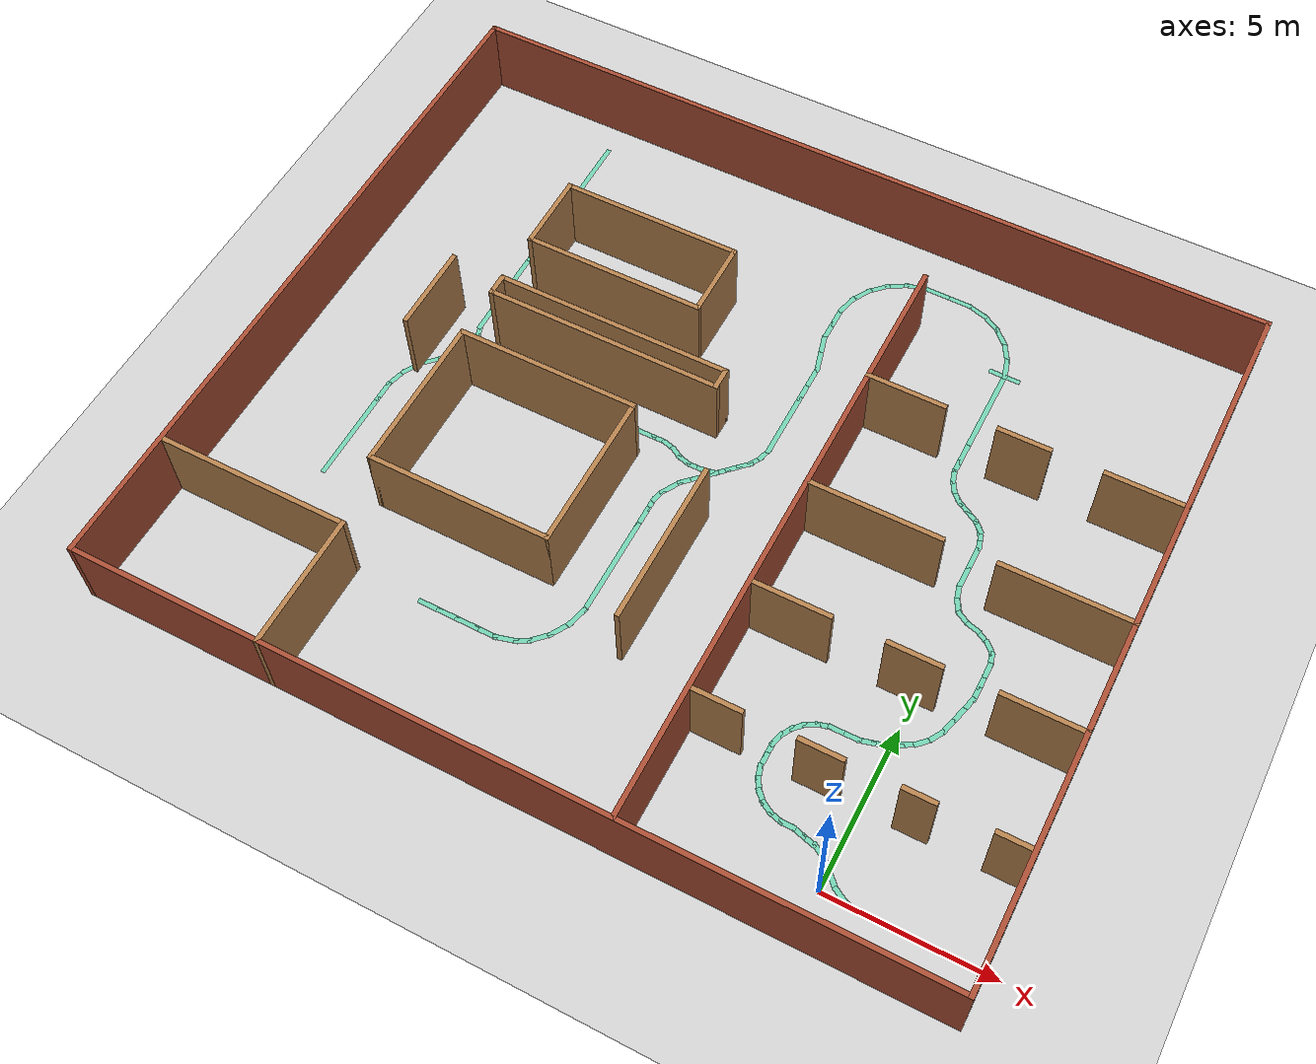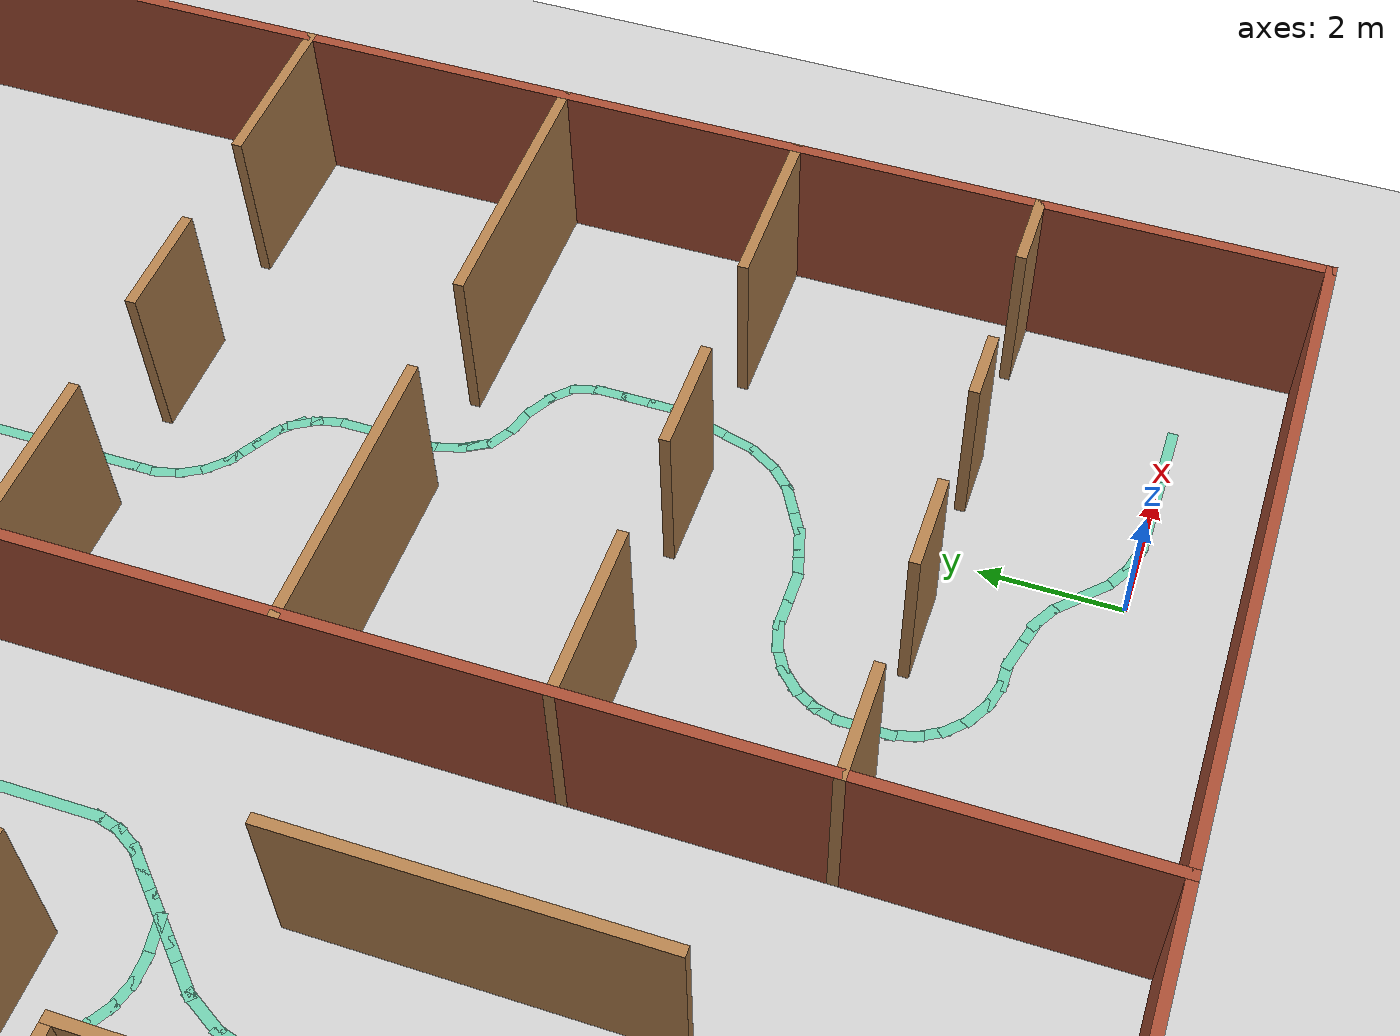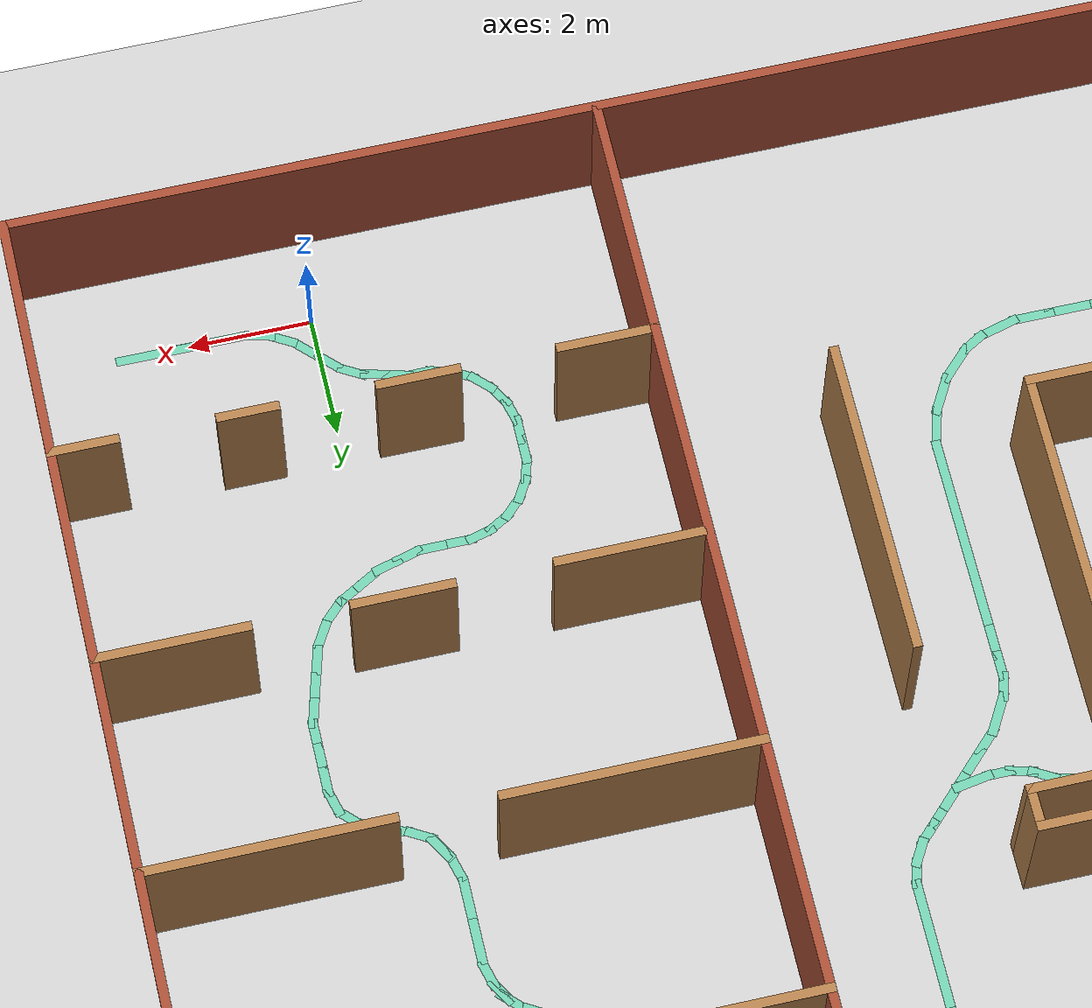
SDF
<sdf version="1.6">
 <world name="default">
  <light name="sun" type="directional">
   <pose>0 0 10 0 -0 0</pose>
   <diffuse>0.8 0.8 0.8 1</diffuse>
   <specular>0.2 0.2 0.2 1</specular>
   <attenuation>
    <range>1000</range>
    <constant>0.9</constant>
    <linear>0.01</linear>
    <quadratic>0.001</quadratic>
   </attenuation>
   <direction>-0.5 0.1 -0.9</direction>
  </light>
  <model name="ground_plane">
   <static>1</static>
   <link name="link">
    <collision name="collision">
     <geometry><plane><normal>0 0 1</normal><size>100 100</size></plane></geometry>
     <surface><friction><ode><mu>100</mu><mu2>50</mu2></ode></friction></surface>
    </collision>
    <visual name="visual">
     <cast_shadows>0</cast_shadows>
     <geometry><plane><normal>0 0 1</normal><size>100 100</size></plane></geometry>
     <material>
      <script><uri>file://media/materials/scripts/gazebo.material</uri><name>Gazebo/Grey</name></script>
     </material>
    </visual>
   </link>
  </model>
  <gravity>0 0 -9.8</gravity>
  <magnetic_field>6e-06 2.3e-05 -4.2e-05</magnetic_field>
  <atmosphere type="adiabatic"/>
  <physics name="default_physics" default="0" type="ode">
   <max_step_size>0.001</max_step_size>
   <real_time_factor>1</real_time_factor>
   <real_time_update_rate>1000</real_time_update_rate>
  </physics>
  <scene><ambient>0.4 0.4 0.4 1</ambient><background>0.7 0.7 0.7 1</background><shadows>1</shadows></scene>
  <spherical_coordinates>
   <surface_model>EARTH_WGS84</surface_model>
   <latitude_deg>0</latitude_deg>
   <longitude_deg>0</longitude_deg>
   <elevation>0</elevation>
   <heading_deg>0</heading_deg>
  </spherical_coordinates>
  <model name="POMDP_test">
   <pose>-8.50001 9.50001 0 0 0 -3.14159</pose>
   <link name="Wall_11">
    <collision name="Wall_11_Collision">
     <geometry><box><size>5.75 0.15 2.5</size></box></geometry>
     <pose>0 0 1.25 0 -0 0</pose>
    </collision>
    <visual name="Wall_11_Visual">
     <pose>0 0 1.25 0 -0 0</pose>
     <geometry><box><size>5.75 0.15 2.5</size></box></geometry>
     <material>
      <script><uri>file://media/materials/scripts/gazebo.material</uri><name>Gazebo/Wood</name></script>
      <ambient>1 1 1 1</ambient>
     </material>
     <meta><layer>0</layer></meta>
    </visual>
    <pose>4.7 4.85 0 0 -0 0</pose>
   </link>
   <link name="Wall_12">
    <collision name="Wall_12_Collision">
     <geometry><box><size>5 0.15 2.5</size></box></geometry>
     <pose>0 0 1.25 0 -0 0</pose>
    </collision>
    <visual name="Wall_12_Visual">
     <pose>0 0 1.25 0 -0 0</pose>
     <geometry><box><size>5 0.15 2.5</size></box></geometry>
     <material>
      <script><uri>file://media/materials/scripts/gazebo.material</uri><name>Gazebo/Wood</name></script>
      <ambient>1 1 1 1</ambient>
     </material>
     <meta><layer>0</layer></meta>
    </visual>
    <pose>7.5 2.425 0 0 -0 -1.5708</pose>
   </link>
   <link name="Wall_13">
    <collision name="Wall_13_Collision">
     <geometry><box><size>5.75 0.15 2.5</size></box></geometry>
     <pose>0 0 1.25 0 -0 0</pose>
    </collision>
    <visual name="Wall_13_Visual">
     <pose>0 0 1.25 0 -0 0</pose>
     <geometry><box><size>5.75 0.15 2.5</size></box></geometry>
     <material>
      <script><uri>file://media/materials/scripts/gazebo.material</uri><name>Gazebo/Wood</name></script>
      <ambient>1 1 1 1</ambient>
     </material>
     <meta><layer>0</layer></meta>
    </visual>
    <pose>4.7 0 0 0 -0 3.14159</pose>
   </link>
   <link name="Wall_14">
    <collision name="Wall_14_Collision">
     <geometry><box><size>5 0.15 2.5</size></box></geometry>
     <pose>0 0 1.25 0 -0 0</pose>
    </collision>
    <visual name="Wall_14_Visual">
     <pose>0 0 1.25 0 -0 0</pose>
     <geometry><box><size>5 0.15 2.5</size></box></geometry>
     <material>
      <script><uri>file://media/materials/scripts/gazebo.material</uri><name>Gazebo/Wood</name></script>
      <ambient>1 1 1 1</ambient>
     </material>
     <meta><layer>0</layer></meta>
    </visual>
    <pose>1.9 2.425 0 0 -0 1.5708</pose>
   </link>
   <link name="Wall_18">
    <collision name="Wall_18_Collision">
     <geometry><box><size>7.5 0.15 2.5</size></box></geometry>
     <pose>0 0 1.25 0 -0 0</pose>
    </collision>
    <visual name="Wall_18_Visual">
     <pose>0 0 1.25 0 -0 0</pose>
     <geometry><box><size>7.5 0.15 2.5</size></box></geometry>
     <material>
      <script><uri>file://media/materials/scripts/gazebo.material</uri><name>Gazebo/Wood</name></script>
      <ambient>1 1 1 1</ambient>
     </material>
     <meta><layer>0</layer></meta>
    </visual>
    <pose>3.825 -1.65 0 0 -0 3.14159</pose>
   </link>
   <link name="Wall_19">
    <collision name="Wall_19_Collision">
     <geometry><box><size>0.75 0.15 2.5</size></box></geometry>
     <pose>0 0 1.25 0 -0 0</pose>
    </collision>
    <visual name="Wall_19_Visual">
     <pose>0 0 1.25 0 -0 0</pose>
     <geometry><box><size>0.75 0.15 2.5</size></box></geometry>
     <material>
      <script><uri>file://media/materials/scripts/gazebo.material</uri><name>Gazebo/Wood</name></script>
      <ambient>1 1 1 1</ambient>
     </material>
     <meta><layer>0</layer></meta>
    </visual>
    <pose>0.15 -1.95 0 0 -0 -1.5708</pose>
   </link>
   <link name="Wall_20">
    <collision name="Wall_20_Collision">
     <geometry><box><size>7.5 0.15 2.5</size></box></geometry>
     <pose>0 0 1.25 0 -0 0</pose>
    </collision>
    <visual name="Wall_20_Visual">
     <pose>0 0 1.25 0 -0 0</pose>
     <geometry><box><size>7.5 0.15 2.5</size></box></geometry>
     <material>
      <script><uri>file://media/materials/scripts/gazebo.material</uri><name>Gazebo/Wood</name></script>
      <ambient>1 1 1 1</ambient>
     </material>
     <meta><layer>0</layer></meta>
    </visual>
    <pose>3.825 -2.25 0 0 -0 0</pose>
   </link>
   <link name="Wall_21">
    <collision name="Wall_21_Collision">
     <geometry><box><size>0.75 0.15 2.5</size></box></geometry>
     <pose>0 0 1.25 0 -0 0</pose>
    </collision>
    <visual name="Wall_21_Visual">
     <pose>0 0 1.25 0 -0 0</pose>
     <geometry><box><size>0.75 0.15 2.5</size></box></geometry>
     <material>
      <script><uri>file://media/materials/scripts/gazebo.material</uri><name>Gazebo/Wood</name></script>
      <ambient>1 1 1 1</ambient>
     </material>
     <meta><layer>0</layer></meta>
    </visual>
    <pose>7.5 -1.95 0 0 -0 1.5708</pose>
   </link>
   <link name="Wall_25">
    <collision name="Wall_25_Collision">
     <geometry><box><size>5.75 0.15 2.5</size></box></geometry>
     <pose>0 0 1.25 0 -0 0</pose>
    </collision>
    <visual name="Wall_25_Visual">
     <pose>0 0 1.25 0 -0 0</pose>
     <geometry><box><size>5.75 0.15 2.5</size></box></geometry>
     <material>
      <script><uri>file://media/materials/scripts/gazebo.material</uri><name>Gazebo/Wood</name></script>
      <ambient>1 1 1 1</ambient>
     </material>
     <meta><layer>0</layer></meta>
    </visual>
    <pose>4.7 -3.9 0 0 -0 3.14159</pose>
   </link>
   <link name="Wall_27">
    <collision name="Wall_27_Collision">
     <geometry><box><size>2.5 0.15 2.5</size></box></geometry>
     <pose>0 0 1.25 0 -0 0</pose>
    </collision>
    <visual name="Wall_27_Visual">
     <pose>0 0 1.25 0 -0 0</pose>
     <geometry><box><size>2.5 0.15 2.5</size></box></geometry>
     <material>
      <script><uri>file://media/materials/scripts/gazebo.material</uri><name>Gazebo/Wood</name></script>
      <ambient>1 1 1 1</ambient>
     </material>
     <meta><layer>0</layer></meta>
    </visual>
    <pose>1.9 -5.075 0 0 -0 -1.5708</pose>
   </link>
   <link name="Wall_28">
    <collision name="Wall_28_Collision">
     <geometry><box><size>5.75 0.15 2.5</size></box></geometry>
     <pose>0 0 1.25 0 -0 0</pose>
    </collision>
    <visual name="Wall_28_Visual">
     <pose>0 0 1.25 0 -0 0</pose>
     <geometry><box><size>5.75 0.15 2.5</size></box></geometry>
     <material>
      <script><uri>file://media/materials/scripts/gazebo.material</uri><name>Gazebo/Wood</name></script>
      <ambient>1 1 1 1</ambient>
     </material>
     <meta><layer>0</layer></meta>
    </visual>
    <pose>4.7 -6.25 0 0 -0 0</pose>
   </link>
   <link name="Wall_29">
    <collision name="Wall_29_Collision">
     <geometry><box><size>2.5 0.15 2.5</size></box></geometry>
     <pose>0 0 1.25 0 -0 0</pose>
    </collision>
    <visual name="Wall_29_Visual">
     <pose>0 0 1.25 0 -0 0</pose>
     <geometry><box><size>2.5 0.15 2.5</size></box></geometry>
     <material>
      <script><uri>file://media/materials/scripts/gazebo.material</uri><name>Gazebo/Wood</name></script>
      <ambient>1 1 1 1</ambient>
     </material>
     <meta><layer>0</layer></meta>
    </visual>
    <pose>7.5 -5.075 0 0 -0 1.5708</pose>
   </link>
   <link name="Wall_33">
    <collision name="Wall_33_Collision">
     <geometry><box><size>19.15 0.15 2.5</size></box></geometry>
     <pose>0 0 1.25 0 -0 0</pose>
    </collision>
    <visual name="Wall_33_Visual">
     <pose>0 0 1.25 0 -0 0</pose>
     <geometry><box><size>19.15 0.15 2.5</size></box></geometry>
     <material>
      <script><uri>file://media/materials/scripts/gazebo.material</uri><name>Gazebo/Bricks</name></script>
      <ambient>1 1 1 1</ambient>
     </material>
     <meta><layer>0</layer></meta>
    </visual>
    <pose>-3.5 1.5 0 0 -0 1.5708</pose>
   </link>
   <link name="Wall_35">
    <collision name="Wall_35_Collision">
     <geometry><box><size>6.15 0.15 2.5</size></box></geometry>
     <pose>0 0 1.25 0 -0 0</pose>
    </collision>
    <visual name="Wall_35_Visual">
     <pose>0 0 1.25 0 -0 0</pose>
     <geometry><box><size>6.15 0.15 2.5</size></box></geometry>
     <material>
      <script><uri>file://media/materials/scripts/gazebo.material</uri><name>Gazebo/Wood</name></script>
      <ambient>1 1 1 1</ambient>
     </material>
     <meta><layer>0</layer></meta>
    </visual>
    <pose>10 7 0 0 -0 3.14159</pose>
   </link>
   <link name="Wall_36">
    <collision name="Wall_36_Collision">
     <geometry><box><size>4.15 0.15 2.5</size></box></geometry>
     <pose>0 0 1.25 0 -0 0</pose>
    </collision>
    <visual name="Wall_36_Visual">
     <pose>0 0 1.25 0 -0 0</pose>
     <geometry><box><size>4.15 0.15 2.5</size></box></geometry>
     <material>
      <script><uri>file://media/materials/scripts/gazebo.material</uri><name>Gazebo/Wood</name></script>
      <ambient>1 1 1 1</ambient>
     </material>
     <meta><layer>0</layer></meta>
    </visual>
    <pose>7 9 0 0 -0 1.5708</pose>
   </link>
   <link name="Wall_38">
    <collision name="Wall_38_Collision">
     <geometry><box><size>5.15 0.15 2.5</size></box></geometry>
     <pose>0 0 1.25 0 -0 0</pose>
    </collision>
    <visual name="Wall_38_Visual">
     <pose>0 0 1.25 0 -0 0</pose>
     <geometry><box><size>5.15 0.15 2.5</size></box></geometry>
     <material>
      <script><uri>file://media/materials/scripts/gazebo.material</uri><name>Gazebo/Wood</name></script>
      <ambient>1 1 1 1</ambient>
     </material>
     <meta><layer>0</layer></meta>
    </visual>
    <pose>-0.9 3.5 0 0 -0 -1.5708</pose>
   </link>
   <link name="Wall_4">
    <collision name="Wall_4_Collision">
     <geometry><box><size>26.15 0.15 2.5</size></box></geometry>
     <pose>0 0 1.25 0 -0 0</pose>
    </collision>
    <visual name="Wall_4_Visual">
     <pose>0 0 1.25 0 -0 0</pose>
     <geometry><box><size>26.15 0.15 2.5</size></box></geometry>
     <material>
      <script><uri>file://media/materials/scripts/gazebo.material</uri><name>Gazebo/Bricks</name></script>
      <ambient>1 1 1 1</ambient>
     </material>
     <meta><layer>0</layer></meta>
    </visual>
    <pose>0 -11 0 0 -0 0</pose>
   </link>
   <link name="Wall_40">
    <collision name="Wall_40_Collision">
     <geometry><box><size>1.15 0.15 2.5</size></box></geometry>
     <pose>0 0 1.25 0 -0 0</pose>
    </collision>
    <visual name="Wall_40_Visual">
     <pose>0 0 1.25 0 -0 0</pose>
     <geometry><box><size>1.15 0.15 2.5</size></box></geometry>
     <material>
      <script><uri>file://media/materials/scripts/gazebo.material</uri><name>Gazebo/Wood</name></script>
      <ambient>1 1 1 1</ambient>
     </material>
     <meta><layer>0</layer></meta>
    </visual>
    <pose>-12.5 7 0 0 -0 0</pose>
   </link>
   <link name="Wall_42">
    <collision name="Wall_42_Collision">
     <geometry><box><size>1 0.15 2.5</size></box></geometry>
     <pose>0 0 1.25 0 -0 0</pose>
    </collision>
    <visual name="Wall_42_Visual">
     <pose>0 0 1.25 0 -0 0</pose>
     <geometry><box><size>1 0.15 2.5</size></box></geometry>
     <material>
      <script><uri>file://media/materials/scripts/gazebo.material</uri><name>Gazebo/Wood</name></script>
      <ambient>1 1 1 1</ambient>
     </material>
     <meta><layer>0</layer></meta>
    </visual>
    <pose>-9.925 7 0 0 -0 0</pose>
   </link>
   <link name="Wall_44">
    <collision name="Wall_44_Collision">
     <geometry><box><size>1.35 0.15 2.5</size></box></geometry>
     <pose>0 0 1.25 0 -0 0</pose>
    </collision>
    <visual name="Wall_44_Visual">
     <pose>0 0 1.25 0 -0 0</pose>
     <geometry><box><size>1.35 0.15 2.5</size></box></geometry>
     <material>
      <script><uri>file://media/materials/scripts/gazebo.material</uri><name>Gazebo/Wood</name></script>
      <ambient>1 1 1 1</ambient>
     </material>
     <meta><layer>0</layer></meta>
    </visual>
    <pose>-7.25 7 0 0 -0 0</pose>
   </link>
   <link name="Wall_46">
    <collision name="Wall_46_Collision">
     <geometry><box><size>1.65 0.15 2.5</size></box></geometry>
     <pose>0 0 1.25 0 -0 0</pose>
    </collision>
    <visual name="Wall_46_Visual">
     <pose>0 0 1.25 0 -0 0</pose>
     <geometry><box><size>1.65 0.15 2.5</size></box></geometry>
     <material>
      <script><uri>file://media/materials/scripts/gazebo.material</uri><name>Gazebo/Wood</name></script>
      <ambient>1 1 1 1</ambient>
     </material>
     <meta><layer>0</layer></meta>
    </visual>
    <pose>-4.25 7 0 0 -0 0</pose>
   </link>
   <link name="Wall_50">
    <collision name="Wall_50_Collision">
     <geometry><box><size>2.5 0.15 2.5</size></box></geometry>
     <pose>0 0 1.25 0 -0 0</pose>
    </collision>
    <visual name="Wall_50_Visual">
     <pose>0 0 1.25 0 -0 0</pose>
     <geometry><box><size>2.5 0.15 2.5</size></box></geometry>
     <material>
      <script><uri>file://media/materials/scripts/gazebo.material</uri><name>Gazebo/Wood</name></script>
      <ambient>1 1 1 1</ambient>
     </material>
     <meta><layer>0</layer></meta>
    </visual>
    <pose>-11.825 3.5 0 0 -0 0</pose>
   </link>
   <link name="Wall_53">
    <collision name="Wall_53_Collision">
     <geometry><box><size>1.65 0.15 2.5</size></box></geometry>
     <pose>0 0 1.25 0 -0 0</pose>
    </collision>
    <visual name="Wall_53_Visual">
     <pose>0 0 1.25 0 -0 0</pose>
     <geometry><box><size>1.65 0.15 2.5</size></box></geometry>
     <material>
      <script><uri>file://media/materials/scripts/gazebo.material</uri><name>Gazebo/Wood</name></script>
      <ambient>1 1 1 1</ambient>
     </material>
     <meta><layer>0</layer></meta>
    </visual>
    <pose>-8.25 3.5 0 0 -0 0</pose>
   </link>
   <link name="Wall_55">
    <collision name="Wall_55_Collision">
     <geometry><box><size>2.5 0.15 2.5</size></box></geometry>
     <pose>0 0 1.25 0 -0 0</pose>
    </collision>
    <visual name="Wall_55_Visual">
     <pose>0 0 1.25 0 -0 0</pose>
     <geometry><box><size>2.5 0.15 2.5</size></box></geometry>
     <material>
      <script><uri>file://media/materials/scripts/gazebo.material</uri><name>Gazebo/Wood</name></script>
      <ambient>1 1 1 1</ambient>
     </material>
     <meta><layer>0</layer></meta>
    </visual>
    <pose>-4.675 3.5 0 0 -0 0</pose>
   </link>
   <link name="Wall_57">
    <collision name="Wall_57_Collision">
     <geometry><box><size>4 0.15 2.5</size></box></geometry>
     <pose>0 0 1.25 0 -0 0</pose>
    </collision>
    <visual name="Wall_57_Visual">
     <pose>0 0 1.25 0 -0 0</pose>
     <geometry><box><size>4 0.15 2.5</size></box></geometry>
     <material>
      <script><uri>file://media/materials/scripts/gazebo.material</uri><name>Gazebo/Wood</name></script>
      <ambient>1 1 1 1</ambient>
     </material>
     <meta><layer>0</layer></meta>
    </visual>
    <pose>-11.075 0 0 0 -0 0</pose>
   </link>
   <link name="Wall_59">
    <collision name="Wall_59_Collision">
     <geometry><box><size>4.15 0.15 2.5</size></box></geometry>
     <pose>0 0 1.25 0 -0 0</pose>
    </collision>
    <visual name="Wall_59_Visual">
     <pose>0 0 1.25 0 -0 0</pose>
     <geometry><box><size>4.15 0.15 2.5</size></box></geometry>
     <material>
      <script><uri>file://media/materials/scripts/gazebo.material</uri><name>Gazebo/Wood</name></script>
      <ambient>1 1 1 1</ambient>
     </material>
     <meta><layer>0</layer></meta>
    </visual>
    <pose>-5.5 0 0 0 -0 0</pose>
   </link>
   <link name="Wall_6">
    <collision name="Wall_6_Collision">
     <geometry><box><size>22.15 0.15 2.5</size></box></geometry>
     <pose>0 0 1.25 0 -0 0</pose>
    </collision>
    <visual name="Wall_6_Visual">
     <pose>0 0 1.25 0 -0 0</pose>
     <geometry><box><size>22.15 0.15 2.5</size></box></geometry>
     <material>
      <script><uri>file://media/materials/scripts/gazebo.material</uri><name>Gazebo/Bricks</name></script>
      <ambient>1 1 1 1</ambient>
     </material>
     <meta><layer>0</layer></meta>
    </visual>
    <pose>13 0 0 0 -0 1.5708</pose>
   </link>
   <link name="Wall_61">
    <collision name="Wall_61_Collision">
     <geometry><box><size>2.5 0.15 2.5</size></box></geometry>
     <pose>0 0 1.25 0 -0 0</pose>
    </collision>
    <visual name="Wall_61_Visual">
     <pose>0 0 1.25 0 -0 0</pose>
     <geometry><box><size>2.5 0.15 2.5</size></box></geometry>
     <material>
      <script><uri>file://media/materials/scripts/gazebo.material</uri><name>Gazebo/Wood</name></script>
      <ambient>1 1 1 1</ambient>
     </material>
     <meta><layer>0</layer></meta>
    </visual>
    <pose>-11.825 -4 0 0 -0 0</pose>
   </link>
   <link name="Wall_63">
    <collision name="Wall_63_Collision">
     <geometry><box><size>1.65 0.15 2.5</size></box></geometry>
     <pose>0 0 1.25 0 -0 0</pose>
    </collision>
    <visual name="Wall_63_Visual">
     <pose>0 0 1.25 0 -0 0</pose>
     <geometry><box><size>1.65 0.15 2.5</size></box></geometry>
     <material>
      <script><uri>file://media/materials/scripts/gazebo.material</uri><name>Gazebo/Wood</name></script>
      <ambient>1 1 1 1</ambient>
     </material>
     <meta><layer>0</layer></meta>
    </visual>
    <pose>-8.25 -4 0 0 -0 0</pose>
   </link>
   <link name="Wall_65">
    <collision name="Wall_65_Collision">
     <geometry><box><size>2.5 0.15 2.5</size></box></geometry>
     <pose>0 0 1.25 0 -0 0</pose>
    </collision>
    <visual name="Wall_65_Visual">
     <pose>0 0 1.25 0 -0 0</pose>
     <geometry><box><size>2.5 0.15 2.5</size></box></geometry>
     <material>
      <script><uri>file://media/materials/scripts/gazebo.material</uri><name>Gazebo/Wood</name></script>
      <ambient>1 1 1 1</ambient>
     </material>
     <meta><layer>0</layer></meta>
    </visual>
    <pose>-4.675 -4 0 0 -0 0</pose>
   </link>
   <link name="Wall_8">
    <collision name="Wall_8_Collision">
     <geometry><box><size>26.15 0.15 2.5</size></box></geometry>
     <pose>0 0 1.25 0 -0 0</pose>
    </collision>
    <visual name="Wall_8_Visual">
     <pose>0 0 1.25 0 -0 0</pose>
     <geometry><box><size>26.15 0.15 2.5</size></box></geometry>
     <material>
      <script><uri>file://media/materials/scripts/gazebo.material</uri><name>Gazebo/Bricks</name></script>
      <ambient>1 1 1 1</ambient>
     </material>
     <meta><layer>0</layer></meta>
    </visual>
    <pose>0 11 0 0 -0 3.14159</pose>
   </link>
   <link name="Wall_9">
    <collision name="Wall_9_Collision">
     <geometry><box><size>22.15 0.15 2.5</size></box></geometry>
     <pose>0 0 1.25 0 -0 0</pose>
    </collision>
    <visual name="Wall_9_Visual">
     <pose>0 0 1.25 0 -0 0</pose>
     <geometry><box><size>22.15 0.15 2.5</size></box></geometry>
     <material>
      <script><uri>file://media/materials/scripts/gazebo.material</uri><name>Gazebo/Bricks</name></script>
      <ambient>1 1 1 1</ambient>
     </material>
     <meta><layer>0</layer></meta>
    </visual>
    <pose>-13 0 0 0 -0 -1.5708</pose>
   </link>
   <static>1</static>
  </model>
  <model name="pomdp_path">
   <link name="Wall_100_clone">
    <pose>-9.37317 0.877969 0 0 -0 2.618</pose>
    <visual name="Wall_100_Visual">
     <pose>0 0 0.0001 0 -0 0</pose>
     <geometry><box><size>0.5 0.15 0</size></box></geometry>
     <material>
      <script><uri>file://media/materials/scripts/gazebo.material</uri><name>Gazebo/Grey</name></script>
      <ambient>0.435294 0.796078 0.67451 1</ambient>
      <shader type="pixel"/>
     </material>
     <meta><layer>0</layer></meta>
    </visual>
    <collision name="Wall_100_Collision">
     <pose>0 0 0.0001 0 -0 0</pose>
     <geometry><box><size>0.5 0.15 0</size></box></geometry>
     <surface>
      <friction>
       <ode><mu>1</mu><mu2>1</mu2><fdir1>0 0 0</fdir1><slip1>0</slip1><slip2>0</slip2></ode>
       <torsional>
        <coefficient>1</coefficient>
        <patch_radius>0</patch_radius>
        <surface_radius>0</surface_radius>
        <use_patch_radius>1</use_patch_radius>
        <ode><slip>0</slip></ode>
       </torsional>
      </friction>
      <bounce><restitution_coefficient>0</restitution_coefficient><threshold>1e+06</threshold></bounce>
      <contact>
       <collide_without_contact>0</collide_without_contact>
       <collide_without_contact_bitmask>1</collide_without_contact_bitmask>
       <collide_bitmask>1</collide_bitmask>
       <ode>
        <soft_cfm>0</soft_cfm>
        <soft_erp>0.2</soft_erp>
        <kp>1e+13</kp>
        <kd>1</kd>
        <max_vel>0.01</max_vel>
        <min_depth>0</min_depth>
       </ode>
       <bullet>
        <split_impulse>1</split_impulse>
        <split_impulse_penetration_threshold>-0.01</split_impulse_penetration_threshold>
        <soft_cfm>0</soft_cfm>
        <soft_erp>0.2</soft_erp>
        <kp>1e+13</kp>
        <kd>1</kd>
       </bullet>
      </contact>
     </surface>
    </collision>
   </link>
   <link name="Wall_100_clone_0">
    <pose>-8.04297 8.50296 0 0 -0 2.618</pose>
    <visual name="Wall_100_Visual">
     <pose>0 0 0.0001 0 -0 0</pose>
     <geometry><box><size>0.5 0.15 0</size></box></geometry>
     <material>
      <script><uri>file://media/materials/scripts/gazebo.material</uri><name>Gazebo/Grey</name></script>
      <ambient>0.435294 0.796078 0.67451 1</ambient>
      <shader type="pixel"/>
     </material>
     <meta><layer>0</layer></meta>
    </visual>
    <collision name="Wall_100_Collision">
     <pose>0 0 0.0001 0 -0 0</pose>
     <geometry><box><size>0.5 0.15 0</size></box></geometry>
     <surface>
      <friction>
       <ode><mu>1</mu><mu2>1</mu2><fdir1>0 0 0</fdir1><slip1>0</slip1><slip2>0</slip2></ode>
       <torsional>
        <coefficient>1</coefficient>
        <patch_radius>0</patch_radius>
        <surface_radius>0</surface_radius>
        <use_patch_radius>1</use_patch_radius>
        <ode><slip>0</slip></ode>
       </torsional>
      </friction>
      <bounce><restitution_coefficient>0</restitution_coefficient><threshold>1e+06</threshold></bounce>
      <contact>
       <collide_without_contact>0</collide_without_contact>
       <collide_without_contact_bitmask>1</collide_without_contact_bitmask>
       <collide_bitmask>1</collide_bitmask>
       <ode>
        <soft_cfm>0</soft_cfm>
        <soft_erp>0.2</soft_erp>
        <kp>1e+13</kp>
        <kd>1</kd>
        <max_vel>0.01</max_vel>
        <min_depth>0</min_depth>
       </ode>
       <bullet>
        <split_impulse>1</split_impulse>
        <split_impulse_penetration_threshold>-0.01</split_impulse_penetration_threshold>
        <soft_cfm>0</soft_cfm>
        <soft_erp>0.2</soft_erp>
        <kp>1e+13</kp>
        <kd>1</kd>
       </bullet>
      </contact>
     </surface>
    </collision>
   </link>
   <link name="Wall_100_clone_clone_clone_clone">
    <pose>7.57944 -0.900466 0 0 -0 -0.52358</pose>
    <visual name="Wall_100_Visual">
     <pose>0 0 0.0001 0 -0 0</pose>
     <geometry><box><size>0.5 0.15 0</size></box></geometry>
     <material>
      <script><uri>file://media/materials/scripts/gazebo.material</uri><name>Gazebo/Grey</name></script>
      <ambient>0.435294 0.796078 0.67451 1</ambient>
      <shader type="pixel"/>
     </material>
     <meta><layer>0</layer></meta>
    </visual>
    <collision name="Wall_100_Collision">
     <pose>0 0 0.0001 0 -0 0</pose>
     <geometry><box><size>0.5 0.15 0</size></box></geometry>
     <surface>
      <friction>
       <ode><mu>1</mu><mu2>1</mu2><fdir1>0 0 0</fdir1><slip1>0</slip1><slip2>0</slip2></ode>
       <torsional>
        <coefficient>1</coefficient>
        <patch_radius>0</patch_radius>
        <surface_radius>0</surface_radius>
        <use_patch_radius>1</use_patch_radius>
        <ode><slip>0</slip></ode>
       </torsional>
      </friction>
      <bounce><restitution_coefficient>0</restitution_coefficient><threshold>1e+06</threshold></bounce>
      <contact>
       <collide_without_contact>0</collide_without_contact>
       <collide_without_contact_bitmask>1</collide_without_contact_bitmask>
       <collide_bitmask>1</collide_bitmask>
       <ode>
        <soft_cfm>0</soft_cfm>
        <soft_erp>0.2</soft_erp>
        <kp>1e+13</kp>
        <kd>1</kd>
        <max_vel>0.01</max_vel>
        <min_depth>0</min_depth>
       </ode>
       <bullet>
        <split_impulse>1</split_impulse>
        <split_impulse_penetration_threshold>-0.01</split_impulse_penetration_threshold>
        <soft_cfm>0</soft_cfm>
        <soft_erp>0.2</soft_erp>
        <kp>1e+13</kp>
        <kd>1</kd>
       </bullet>
      </contact>
     </surface>
    </collision>
   </link>
   <link name="Wall_101">
    <pose>-7.69538 8.38063 0 0 0 -0.261799</pose>
    <visual name="Wall_101_Visual">
     <pose>0 0 0.0001 0 -0 0</pose>
     <geometry><box><size>0.5 0.15 0</size></box></geometry>
     <material>
      <script><uri>file://media/materials/scripts/gazebo.material</uri><name>Gazebo/Grey</name></script>
      <ambient>0.435294 0.796078 0.67451 1</ambient>
      <shader type="pixel"/>
     </material>
     <meta><layer>0</layer></meta>
    </visual>
    <collision name="Wall_101_Collision">
     <pose>0 0 0.0001 0 -0 0</pose>
     <geometry><box><size>0.5 0.15 0</size></box></geometry>
     <surface>
      <friction>
       <ode><mu>1</mu><mu2>1</mu2><fdir1>0 0 0</fdir1><slip1>0</slip1><slip2>0</slip2></ode>
       <torsional>
        <coefficient>1</coefficient>
        <patch_radius>0</patch_radius>
        <surface_radius>0</surface_radius>
        <use_patch_radius>1</use_patch_radius>
        <ode><slip>0</slip></ode>
       </torsional>
      </friction>
      <bounce><restitution_coefficient>0</restitution_coefficient><threshold>1e+06</threshold></bounce>
      <contact>
       <collide_without_contact>0</collide_without_contact>
       <collide_without_contact_bitmask>1</collide_without_contact_bitmask>
       <collide_bitmask>1</collide_bitmask>
       <ode>
        <soft_cfm>0</soft_cfm>
        <soft_erp>0.2</soft_erp>
        <kp>1e+13</kp>
        <kd>1</kd>
        <max_vel>0.01</max_vel>
        <min_depth>0</min_depth>
       </ode>
       <bullet>
        <split_impulse>1</split_impulse>
        <split_impulse_penetration_threshold>-0.01</split_impulse_penetration_threshold>
        <soft_cfm>0</soft_cfm>
        <soft_erp>0.2</soft_erp>
        <kp>1e+13</kp>
        <kd>1</kd>
       </bullet>
      </contact>
     </surface>
    </collision>
   </link>
   <link name="Wall_101_clone_clone">
    <pose>-9.02258 0.726106 0 0 0 -0.261789</pose>
    <visual name="Wall_101_Visual">
     <pose>0 0 0.0001 0 -0 0</pose>
     <geometry><box><size>0.5 0.15 0</size></box></geometry>
     <material>
      <script><uri>file://media/materials/scripts/gazebo.material</uri><name>Gazebo/Grey</name></script>
      <ambient>0.435294 0.796078 0.67451 1</ambient>
      <shader type="pixel"/>
     </material>
     <meta><layer>0</layer></meta>
    </visual>
    <collision name="Wall_101_Collision">
     <pose>0 0 0.0001 0 -0 0</pose>
     <geometry><box><size>0.5 0.15 0</size></box></geometry>
     <surface>
      <friction>
       <ode><mu>1</mu><mu2>1</mu2><fdir1>0 0 0</fdir1><slip1>0</slip1><slip2>0</slip2></ode>
       <torsional>
        <coefficient>1</coefficient>
        <patch_radius>0</patch_radius>
        <surface_radius>0</surface_radius>
        <use_patch_radius>1</use_patch_radius>
        <ode><slip>0</slip></ode>
       </torsional>
      </friction>
      <bounce><restitution_coefficient>0</restitution_coefficient><threshold>1e+06</threshold></bounce>
      <contact>
       <collide_without_contact>0</collide_without_contact>
       <collide_without_contact_bitmask>1</collide_without_contact_bitmask>
       <collide_bitmask>1</collide_bitmask>
       <ode>
        <soft_cfm>0</soft_cfm>
        <soft_erp>0.2</soft_erp>
        <kp>1e+13</kp>
        <kd>1</kd>
        <max_vel>0.01</max_vel>
        <min_depth>0</min_depth>
       </ode>
       <bullet>
        <split_impulse>1</split_impulse>
        <split_impulse_penetration_threshold>-0.01</split_impulse_penetration_threshold>
        <soft_cfm>0</soft_cfm>
        <soft_erp>0.2</soft_erp>
        <kp>1e+13</kp>
        <kd>1</kd>
       </bullet>
      </contact>
     </surface>
    </collision>
   </link>
   <link name="Wall_102">
    <pose>-7.35731 8.29004 0 0 0 -0.261799</pose>
    <visual name="Wall_102_Visual">
     <pose>0 0 0.0001 0 -0 0</pose>
     <geometry><box><size>0.5 0.15 0</size></box></geometry>
     <material>
      <script><uri>file://media/materials/scripts/gazebo.material</uri><name>Gazebo/Grey</name></script>
      <ambient>0.435294 0.796078 0.67451 1</ambient>
      <shader type="pixel"/>
     </material>
     <meta><layer>0</layer></meta>
    </visual>
    <collision name="Wall_102_Collision">
     <pose>0 0 0.0001 0 -0 0</pose>
     <geometry><box><size>0.5 0.15 0</size></box></geometry>
     <surface>
      <friction>
       <ode><mu>1</mu><mu2>1</mu2><fdir1>0 0 0</fdir1><slip1>0</slip1><slip2>0</slip2></ode>
       <torsional>
        <coefficient>1</coefficient>
        <patch_radius>0</patch_radius>
        <surface_radius>0</surface_radius>
        <use_patch_radius>1</use_patch_radius>
        <ode><slip>0</slip></ode>
       </torsional>
      </friction>
      <bounce><restitution_coefficient>0</restitution_coefficient><threshold>1e+06</threshold></bounce>
      <contact>
       <collide_without_contact>0</collide_without_contact>
       <collide_without_contact_bitmask>1</collide_without_contact_bitmask>
       <collide_bitmask>1</collide_bitmask>
       <ode>
        <soft_cfm>0</soft_cfm>
        <soft_erp>0.2</soft_erp>
        <kp>1e+13</kp>
        <kd>1</kd>
        <max_vel>0.01</max_vel>
        <min_depth>0</min_depth>
       </ode>
       <bullet>
        <split_impulse>1</split_impulse>
        <split_impulse_penetration_threshold>-0.01</split_impulse_penetration_threshold>
        <soft_cfm>0</soft_cfm>
        <soft_erp>0.2</soft_erp>
        <kp>1e+13</kp>
        <kd>1</kd>
       </bullet>
      </contact>
     </surface>
    </collision>
   </link>
   <link name="Wall_102_clone_clone">
    <pose>7.3019 -0.80535 0 0 -0 -0.26179</pose>
    <visual name="Wall_102_Visual">
     <pose>0 0 0.0001 0 -0 0</pose>
     <geometry><box><size>0.5 0.15 0</size></box></geometry>
     <material>
      <script><uri>file://media/materials/scripts/gazebo.material</uri><name>Gazebo/Grey</name></script>
      <ambient>0.435294 0.796078 0.67451 1</ambient>
      <shader type="pixel"/>
     </material>
     <meta><layer>0</layer></meta>
    </visual>
    <collision name="Wall_102_Collision">
     <pose>0 0 0.0001 0 -0 0</pose>
     <geometry><box><size>0.5 0.15 0</size></box></geometry>
     <surface>
      <friction>
       <ode><mu>1</mu><mu2>1</mu2><fdir1>0 0 0</fdir1><slip1>0</slip1><slip2>0</slip2></ode>
       <torsional>
        <coefficient>1</coefficient>
        <patch_radius>0</patch_radius>
        <surface_radius>0</surface_radius>
        <use_patch_radius>1</use_patch_radius>
        <ode><slip>0</slip></ode>
       </torsional>
      </friction>
      <bounce><restitution_coefficient>0</restitution_coefficient><threshold>1e+06</threshold></bounce>
      <contact>
       <collide_without_contact>0</collide_without_contact>
       <collide_without_contact_bitmask>1</collide_without_contact_bitmask>
       <collide_bitmask>1</collide_bitmask>
       <ode>
        <soft_cfm>0</soft_cfm>
        <soft_erp>0.2</soft_erp>
        <kp>1e+13</kp>
        <kd>1</kd>
        <max_vel>0.01</max_vel>
        <min_depth>0</min_depth>
       </ode>
       <bullet>
        <split_impulse>1</split_impulse>
        <split_impulse_penetration_threshold>-0.01</split_impulse_penetration_threshold>
        <soft_cfm>0</soft_cfm>
        <soft_erp>0.2</soft_erp>
        <kp>1e+13</kp>
        <kd>1</kd>
       </bullet>
      </contact>
     </surface>
    </collision>
   </link>
   <link name="Wall_103">
    <pose>-7.01327 8.24475 0 0 -0 0</pose>
    <visual name="Wall_103_Visual">
     <pose>0 0 0.0001 0 -0 0</pose>
     <geometry><box><size>0.5 0.15 0</size></box></geometry>
     <material>
      <script><uri>file://media/materials/scripts/gazebo.material</uri><name>Gazebo/Grey</name></script>
      <ambient>0.435294 0.796078 0.67451 1</ambient>
      <shader type="pixel"/>
     </material>
     <meta><layer>0</layer></meta>
    </visual>
    <collision name="Wall_103_Collision">
     <pose>0 0 0.0001 0 -0 0</pose>
     <geometry><box><size>0.5 0.15 0</size></box></geometry>
     <surface>
      <friction>
       <ode><mu>1</mu><mu2>1</mu2><fdir1>0 0 0</fdir1><slip1>0</slip1><slip2>0</slip2></ode>
       <torsional>
        <coefficient>1</coefficient>
        <patch_radius>0</patch_radius>
        <surface_radius>0</surface_radius>
        <use_patch_radius>1</use_patch_radius>
        <ode><slip>0</slip></ode>
       </torsional>
      </friction>
      <bounce><restitution_coefficient>0</restitution_coefficient><threshold>1e+06</threshold></bounce>
      <contact>
       <collide_without_contact>0</collide_without_contact>
       <collide_without_contact_bitmask>1</collide_without_contact_bitmask>
       <collide_bitmask>1</collide_bitmask>
       <ode>
        <soft_cfm>0</soft_cfm>
        <soft_erp>0.2</soft_erp>
        <kp>1e+13</kp>
        <kd>1</kd>
        <max_vel>0.01</max_vel>
        <min_depth>0</min_depth>
       </ode>
       <bullet>
        <split_impulse>1</split_impulse>
        <split_impulse_penetration_threshold>-0.01</split_impulse_penetration_threshold>
        <soft_cfm>0</soft_cfm>
        <soft_erp>0.2</soft_erp>
        <kp>1e+13</kp>
        <kd>1</kd>
       </bullet>
      </contact>
     </surface>
    </collision>
   </link>
   <link name="Wall_104">
    <pose>-6.66924 8.19946 0 0 0 -0.261799</pose>
    <visual name="Wall_104_Visual">
     <pose>0 0 0.0001 0 -0 0</pose>
     <geometry><box><size>0.5 0.15 0</size></box></geometry>
     <material>
      <script><uri>file://media/materials/scripts/gazebo.material</uri><name>Gazebo/Grey</name></script>
      <ambient>0.435294 0.796078 0.67451 1</ambient>
      <shader type="pixel"/>
     </material>
     <meta><layer>0</layer></meta>
    </visual>
    <collision name="Wall_104_Collision">
     <pose>0 0 0.0001 0 -0 0</pose>
     <geometry><box><size>0.5 0.15 0</size></box></geometry>
     <surface>
      <friction>
       <ode><mu>1</mu><mu2>1</mu2><fdir1>0 0 0</fdir1><slip1>0</slip1><slip2>0</slip2></ode>
       <torsional>
        <coefficient>1</coefficient>
        <patch_radius>0</patch_radius>
        <surface_radius>0</surface_radius>
        <use_patch_radius>1</use_patch_radius>
        <ode><slip>0</slip></ode>
       </torsional>
      </friction>
      <bounce><restitution_coefficient>0</restitution_coefficient><threshold>1e+06</threshold></bounce>
      <contact>
       <collide_without_contact>0</collide_without_contact>
       <collide_without_contact_bitmask>1</collide_without_contact_bitmask>
       <collide_bitmask>1</collide_bitmask>
       <ode>
        <soft_cfm>0</soft_cfm>
        <soft_erp>0.2</soft_erp>
        <kp>1e+13</kp>
        <kd>1</kd>
        <max_vel>0.01</max_vel>
        <min_depth>0</min_depth>
       </ode>
       <bullet>
        <split_impulse>1</split_impulse>
        <split_impulse_penetration_threshold>-0.01</split_impulse_penetration_threshold>
        <soft_cfm>0</soft_cfm>
        <soft_erp>0.2</soft_erp>
        <kp>1e+13</kp>
        <kd>1</kd>
       </bullet>
      </contact>
     </surface>
    </collision>
   </link>
   <link name="Wall_104_clone">
    <pose>-9.35694 9.46047 0 0 -0 2.8798</pose>
    <visual name="Wall_104_Visual">
     <pose>0 0 0.0001 0 -0 0</pose>
     <geometry><box><size>0.5 0.15 0</size></box></geometry>
     <material>
      <script><uri>file://media/materials/scripts/gazebo.material</uri><name>Gazebo/Grey</name></script>
      <ambient>0.435294 0.796078 0.67451 1</ambient>
      <shader type="pixel"/>
     </material>
     <meta><layer>0</layer></meta>
    </visual>
    <collision name="Wall_104_Collision">
     <pose>0 0 0.0001 0 -0 0</pose>
     <geometry><box><size>0.5 0.15 0</size></box></geometry>
     <surface>
      <friction>
       <ode><mu>1</mu><mu2>1</mu2><fdir1>0 0 0</fdir1><slip1>0</slip1><slip2>0</slip2></ode>
       <torsional>
        <coefficient>1</coefficient>
        <patch_radius>0</patch_radius>
        <surface_radius>0</surface_radius>
        <use_patch_radius>1</use_patch_radius>
        <ode><slip>0</slip></ode>
       </torsional>
      </friction>
      <bounce><restitution_coefficient>0</restitution_coefficient><threshold>1e+06</threshold></bounce>
      <contact>
       <collide_without_contact>0</collide_without_contact>
       <collide_without_contact_bitmask>1</collide_without_contact_bitmask>
       <collide_bitmask>1</collide_bitmask>
       <ode>
        <soft_cfm>0</soft_cfm>
        <soft_erp>0.2</soft_erp>
        <kp>1e+13</kp>
        <kd>1</kd>
        <max_vel>0.01</max_vel>
        <min_depth>0</min_depth>
       </ode>
       <bullet>
        <split_impulse>1</split_impulse>
        <split_impulse_penetration_threshold>-0.01</split_impulse_penetration_threshold>
        <soft_cfm>0</soft_cfm>
        <soft_erp>0.2</soft_erp>
        <kp>1e+13</kp>
        <kd>1</kd>
       </bullet>
      </contact>
     </surface>
    </collision>
   </link>
   <link name="Wall_105">
    <pose>-6.34865 8.06666 0 0 0 -0.523599</pose>
    <visual name="Wall_105_Visual">
     <pose>0 0 0.0001 0 -0 0</pose>
     <geometry><box><size>0.5 0.15 0</size></box></geometry>
     <material>
      <script><uri>file://media/materials/scripts/gazebo.material</uri><name>Gazebo/Grey</name></script>
      <ambient>0.435294 0.796078 0.67451 1</ambient>
      <shader type="pixel"/>
     </material>
     <meta><layer>0</layer></meta>
    </visual>
    <collision name="Wall_105_Collision">
     <pose>0 0 0.0001 0 -0 0</pose>
     <geometry><box><size>0.5 0.15 0</size></box></geometry>
     <surface>
      <friction>
       <ode><mu>1</mu><mu2>1</mu2><fdir1>0 0 0</fdir1><slip1>0</slip1><slip2>0</slip2></ode>
       <torsional>
        <coefficient>1</coefficient>
        <patch_radius>0</patch_radius>
        <surface_radius>0</surface_radius>
        <use_patch_radius>1</use_patch_radius>
        <ode><slip>0</slip></ode>
       </torsional>
      </friction>
      <bounce><restitution_coefficient>0</restitution_coefficient><threshold>1e+06</threshold></bounce>
      <contact>
       <collide_without_contact>0</collide_without_contact>
       <collide_without_contact_bitmask>1</collide_without_contact_bitmask>
       <collide_bitmask>1</collide_bitmask>
       <ode>
        <soft_cfm>0</soft_cfm>
        <soft_erp>0.2</soft_erp>
        <kp>1e+13</kp>
        <kd>1</kd>
        <max_vel>0.01</max_vel>
        <min_depth>0</min_depth>
       </ode>
       <bullet>
        <split_impulse>1</split_impulse>
        <split_impulse_penetration_threshold>-0.01</split_impulse_penetration_threshold>
        <soft_cfm>0</soft_cfm>
        <soft_erp>0.2</soft_erp>
        <kp>1e+13</kp>
        <kd>1</kd>
       </bullet>
      </contact>
     </surface>
    </collision>
   </link>
   <link name="Wall_105_clone">
    <pose>-9.01884 9.31716 0 0 -0 2.618</pose>
    <visual name="Wall_105_Visual">
     <pose>0 0 0.0001 0 -0 0</pose>
     <geometry><box><size>0.5 0.15 0</size></box></geometry>
     <material>
      <script><uri>file://media/materials/scripts/gazebo.material</uri><name>Gazebo/Grey</name></script>
      <ambient>0.435294 0.796078 0.67451 1</ambient>
      <shader type="pixel"/>
     </material>
     <meta><layer>0</layer></meta>
    </visual>
    <collision name="Wall_105_Collision">
     <pose>0 0 0.0001 0 -0 0</pose>
     <geometry><box><size>0.5 0.15 0</size></box></geometry>
     <surface>
      <friction>
       <ode><mu>1</mu><mu2>1</mu2><fdir1>0 0 0</fdir1><slip1>0</slip1><slip2>0</slip2></ode>
       <torsional>
        <coefficient>1</coefficient>
        <patch_radius>0</patch_radius>
        <surface_radius>0</surface_radius>
        <use_patch_radius>1</use_patch_radius>
        <ode><slip>0</slip></ode>
       </torsional>
      </friction>
      <bounce><restitution_coefficient>0</restitution_coefficient><threshold>1e+06</threshold></bounce>
      <contact>
       <collide_without_contact>0</collide_without_contact>
       <collide_without_contact_bitmask>1</collide_without_contact_bitmask>
       <collide_bitmask>1</collide_bitmask>
       <ode>
        <soft_cfm>0</soft_cfm>
        <soft_erp>0.2</soft_erp>
        <kp>1e+13</kp>
        <kd>1</kd>
        <max_vel>0.01</max_vel>
        <min_depth>0</min_depth>
       </ode>
       <bullet>
        <split_impulse>1</split_impulse>
        <split_impulse_penetration_threshold>-0.01</split_impulse_penetration_threshold>
        <soft_cfm>0</soft_cfm>
        <soft_erp>0.2</soft_erp>
        <kp>1e+13</kp>
        <kd>1</kd>
       </bullet>
      </contact>
     </surface>
    </collision>
   </link>
   <link name="Wall_107">
    <pose>-6.07335 7.85542 0 0 0 -0.785398</pose>
    <visual name="Wall_107_Visual">
     <pose>0 0 0.0001 0 -0 0</pose>
     <geometry><box><size>0.5 0.15 0</size></box></geometry>
     <material>
      <script><uri>file://media/materials/scripts/gazebo.material</uri><name>Gazebo/Grey</name></script>
      <ambient>0.435294 0.796078 0.67451 1</ambient>
      <shader type="pixel"/>
     </material>
     <meta><layer>0</layer></meta>
    </visual>
    <collision name="Wall_107_Collision">
     <pose>0 0 0.0001 0 -0 0</pose>
     <geometry><box><size>0.5 0.15 0</size></box></geometry>
     <surface>
      <friction>
       <ode><mu>1</mu><mu2>1</mu2><fdir1>0 0 0</fdir1><slip1>0</slip1><slip2>0</slip2></ode>
       <torsional>
        <coefficient>1</coefficient>
        <patch_radius>0</patch_radius>
        <surface_radius>0</surface_radius>
        <use_patch_radius>1</use_patch_radius>
        <ode><slip>0</slip></ode>
       </torsional>
      </friction>
      <bounce><restitution_coefficient>0</restitution_coefficient><threshold>1e+06</threshold></bounce>
      <contact>
       <collide_without_contact>0</collide_without_contact>
       <collide_without_contact_bitmask>1</collide_without_contact_bitmask>
       <collide_bitmask>1</collide_bitmask>
       <ode>
        <soft_cfm>0</soft_cfm>
        <soft_erp>0.2</soft_erp>
        <kp>1e+13</kp>
        <kd>1</kd>
        <max_vel>0.01</max_vel>
        <min_depth>0</min_depth>
       </ode>
       <bullet>
        <split_impulse>1</split_impulse>
        <split_impulse_penetration_threshold>-0.01</split_impulse_penetration_threshold>
        <soft_cfm>0</soft_cfm>
        <soft_erp>0.2</soft_erp>
        <kp>1e+13</kp>
        <kd>1</kd>
       </bullet>
      </contact>
     </surface>
    </collision>
   </link>
   <link name="Wall_107_clone">
    <pose>-8.69042 9.06213 0 0 -0 2.3562</pose>
    <visual name="Wall_107_Visual">
     <pose>0 0 0.0001 0 -0 0</pose>
     <geometry><box><size>0.5 0.15 0</size></box></geometry>
     <material>
      <script><uri>file://media/materials/scripts/gazebo.material</uri><name>Gazebo/Grey</name></script>
      <ambient>0.435294 0.796078 0.67451 1</ambient>
      <shader type="pixel"/>
     </material>
     <meta><layer>0</layer></meta>
    </visual>
    <collision name="Wall_107_Collision">
     <pose>0 0 0.0001 0 -0 0</pose>
     <geometry><box><size>0.5 0.15 0</size></box></geometry>
     <surface>
      <friction>
       <ode><mu>1</mu><mu2>1</mu2><fdir1>0 0 0</fdir1><slip1>0</slip1><slip2>0</slip2></ode>
       <torsional>
        <coefficient>1</coefficient>
        <patch_radius>0</patch_radius>
        <surface_radius>0</surface_radius>
        <use_patch_radius>1</use_patch_radius>
        <ode><slip>0</slip></ode>
       </torsional>
      </friction>
      <bounce><restitution_coefficient>0</restitution_coefficient><threshold>1e+06</threshold></bounce>
      <contact>
       <collide_without_contact>0</collide_without_contact>
       <collide_without_contact_bitmask>1</collide_without_contact_bitmask>
       <collide_bitmask>1</collide_bitmask>
       <ode>
        <soft_cfm>0</soft_cfm>
        <soft_erp>0.2</soft_erp>
        <kp>1e+13</kp>
        <kd>1</kd>
        <max_vel>0.01</max_vel>
        <min_depth>0</min_depth>
       </ode>
       <bullet>
        <split_impulse>1</split_impulse>
        <split_impulse_penetration_threshold>-0.01</split_impulse_penetration_threshold>
        <soft_cfm>0</soft_cfm>
        <soft_erp>0.2</soft_erp>
        <kp>1e+13</kp>
        <kd>1</kd>
       </bullet>
      </contact>
     </surface>
    </collision>
   </link>
   <link name="Wall_107_clone_0">
    <pose>-8.38692 8.76886 0 0 -0 2.3562</pose>
    <visual name="Wall_107_Visual">
     <pose>0 0 0.0001 0 -0 0</pose>
     <geometry><box><size>0.5 0.15 0</size></box></geometry>
     <material>
      <script><uri>file://media/materials/scripts/gazebo.material</uri><name>Gazebo/Grey</name></script>
      <ambient>0.435294 0.796078 0.67451 1</ambient>
      <shader type="pixel"/>
     </material>
     <meta><layer>0</layer></meta>
    </visual>
    <collision name="Wall_107_Collision">
     <pose>0 0 0.0001 0 -0 0</pose>
     <geometry><box><size>0.5 0.15 0</size></box></geometry>
     <surface>
      <friction>
       <ode><mu>1</mu><mu2>1</mu2><fdir1>0 0 0</fdir1><slip1>0</slip1><slip2>0</slip2></ode>
       <torsional>
        <coefficient>1</coefficient>
        <patch_radius>0</patch_radius>
        <surface_radius>0</surface_radius>
        <use_patch_radius>1</use_patch_radius>
        <ode><slip>0</slip></ode>
       </torsional>
      </friction>
      <bounce><restitution_coefficient>0</restitution_coefficient><threshold>1e+06</threshold></bounce>
      <contact>
       <collide_without_contact>0</collide_without_contact>
       <collide_without_contact_bitmask>1</collide_without_contact_bitmask>
       <collide_bitmask>1</collide_bitmask>
       <ode>
        <soft_cfm>0</soft_cfm>
        <soft_erp>0.2</soft_erp>
        <kp>1e+13</kp>
        <kd>1</kd>
        <max_vel>0.01</max_vel>
        <min_depth>0</min_depth>
       </ode>
       <bullet>
        <split_impulse>1</split_impulse>
        <split_impulse_penetration_threshold>-0.01</split_impulse_penetration_threshold>
        <soft_cfm>0</soft_cfm>
        <soft_erp>0.2</soft_erp>
        <kp>1e+13</kp>
        <kd>1</kd>
       </bullet>
      </contact>
     </surface>
    </collision>
   </link>
   <link name="Wall_108">
    <pose>-5.8621 7.58012 0 0 0 -1.0472</pose>
    <visual name="Wall_108_Visual">
     <pose>0 0 0.0001 0 -0 0</pose>
     <geometry><box><size>0.5 0.15 0</size></box></geometry>
     <material>
      <script><uri>file://media/materials/scripts/gazebo.material</uri><name>Gazebo/Grey</name></script>
      <ambient>0.435294 0.796078 0.67451 1</ambient>
      <shader type="pixel"/>
     </material>
     <meta><layer>0</layer></meta>
    </visual>
    <collision name="Wall_108_Collision">
     <pose>0 0 0.0001 0 -0 0</pose>
     <geometry><box><size>0.5 0.15 0</size></box></geometry>
     <surface>
      <friction>
       <ode><mu>1</mu><mu2>1</mu2><fdir1>0 0 0</fdir1><slip1>0</slip1><slip2>0</slip2></ode>
       <torsional>
        <coefficient>1</coefficient>
        <patch_radius>0</patch_radius>
        <surface_radius>0</surface_radius>
        <use_patch_radius>1</use_patch_radius>
        <ode><slip>0</slip></ode>
       </torsional>
      </friction>
      <bounce><restitution_coefficient>0</restitution_coefficient><threshold>1e+06</threshold></bounce>
      <contact>
       <collide_without_contact>0</collide_without_contact>
       <collide_without_contact_bitmask>1</collide_without_contact_bitmask>
       <collide_bitmask>1</collide_bitmask>
       <ode>
        <soft_cfm>0</soft_cfm>
        <soft_erp>0.2</soft_erp>
        <kp>1e+13</kp>
        <kd>1</kd>
        <max_vel>0.01</max_vel>
        <min_depth>0</min_depth>
       </ode>
       <bullet>
        <split_impulse>1</split_impulse>
        <split_impulse_penetration_threshold>-0.01</split_impulse_penetration_threshold>
        <soft_cfm>0</soft_cfm>
        <soft_erp>0.2</soft_erp>
        <kp>1e+13</kp>
        <kd>1</kd>
       </bullet>
      </contact>
     </surface>
    </collision>
   </link>
   <link name="Wall_109">
    <pose>-5.72931 7.25953 0 0 0 -1.309</pose>
    <visual name="Wall_109_Visual">
     <pose>0 0 0.0001 0 -0 0</pose>
     <geometry><box><size>0.5 0.15 0</size></box></geometry>
     <material>
      <script><uri>file://media/materials/scripts/gazebo.material</uri><name>Gazebo/Grey</name></script>
      <ambient>0.435294 0.796078 0.67451 1</ambient>
      <shader type="pixel"/>
     </material>
     <meta><layer>0</layer></meta>
    </visual>
    <collision name="Wall_109_Collision">
     <pose>0 0 0.0001 0 -0 0</pose>
     <geometry><box><size>0.5 0.15 0</size></box></geometry>
     <surface>
      <friction>
       <ode><mu>1</mu><mu2>1</mu2><fdir1>0 0 0</fdir1><slip1>0</slip1><slip2>0</slip2></ode>
       <torsional>
        <coefficient>1</coefficient>
        <patch_radius>0</patch_radius>
        <surface_radius>0</surface_radius>
        <use_patch_radius>1</use_patch_radius>
        <ode><slip>0</slip></ode>
       </torsional>
      </friction>
      <bounce><restitution_coefficient>0</restitution_coefficient><threshold>1e+06</threshold></bounce>
      <contact>
       <collide_without_contact>0</collide_without_contact>
       <collide_without_contact_bitmask>1</collide_without_contact_bitmask>
       <collide_bitmask>1</collide_bitmask>
       <ode>
        <soft_cfm>0</soft_cfm>
        <soft_erp>0.2</soft_erp>
        <kp>1e+13</kp>
        <kd>1</kd>
        <max_vel>0.01</max_vel>
        <min_depth>0</min_depth>
       </ode>
       <bullet>
        <split_impulse>1</split_impulse>
        <split_impulse_penetration_threshold>-0.01</split_impulse_penetration_threshold>
        <soft_cfm>0</soft_cfm>
        <soft_erp>0.2</soft_erp>
        <kp>1e+13</kp>
        <kd>1</kd>
       </bullet>
      </contact>
     </surface>
    </collision>
   </link>
   <link name="Wall_110">
    <pose>-5.68402 6.91549 0 0 0 -1.5708</pose>
    <visual name="Wall_110_Visual">
     <pose>0 0 0.0001 0 -0 0</pose>
     <geometry><box><size>0.5 0.15 0</size></box></geometry>
     <material>
      <script><uri>file://media/materials/scripts/gazebo.material</uri><name>Gazebo/Grey</name></script>
      <ambient>0.435294 0.796078 0.67451 1</ambient>
      <shader type="pixel"/>
     </material>
     <meta><layer>0</layer></meta>
    </visual>
    <collision name="Wall_110_Collision">
     <pose>0 0 0.0001 0 -0 0</pose>
     <geometry><box><size>0.5 0.15 0</size></box></geometry>
     <surface>
      <friction>
       <ode><mu>1</mu><mu2>1</mu2><fdir1>0 0 0</fdir1><slip1>0</slip1><slip2>0</slip2></ode>
       <torsional>
        <coefficient>1</coefficient>
        <patch_radius>0</patch_radius>
        <surface_radius>0</surface_radius>
        <use_patch_radius>1</use_patch_radius>
        <ode><slip>0</slip></ode>
       </torsional>
      </friction>
      <bounce><restitution_coefficient>0</restitution_coefficient><threshold>1e+06</threshold></bounce>
      <contact>
       <collide_without_contact>0</collide_without_contact>
       <collide_without_contact_bitmask>1</collide_without_contact_bitmask>
       <collide_bitmask>1</collide_bitmask>
       <ode>
        <soft_cfm>0</soft_cfm>
        <soft_erp>0.2</soft_erp>
        <kp>1e+13</kp>
        <kd>1</kd>
        <max_vel>0.01</max_vel>
        <min_depth>0</min_depth>
       </ode>
       <bullet>
        <split_impulse>1</split_impulse>
        <split_impulse_penetration_threshold>-0.01</split_impulse_penetration_threshold>
        <soft_cfm>0</soft_cfm>
        <soft_erp>0.2</soft_erp>
        <kp>1e+13</kp>
        <kd>1</kd>
       </bullet>
      </contact>
     </surface>
    </collision>
   </link>
   <link name="Wall_112">
    <pose>-5.68402 6.56549 0 0 0 -1.5708</pose>
    <visual name="Wall_112_Visual">
     <pose>0 0 0.0001 0 -0 0</pose>
     <geometry><box><size>0.5 0.15 0</size></box></geometry>
     <material>
      <script><uri>file://media/materials/scripts/gazebo.material</uri><name>Gazebo/Grey</name></script>
      <ambient>0.435294 0.796078 0.67451 1</ambient>
      <shader type="pixel"/>
     </material>
     <meta><layer>0</layer></meta>
    </visual>
    <collision name="Wall_112_Collision">
     <pose>0 0 0.0001 0 -0 0</pose>
     <geometry><box><size>0.5 0.15 0</size></box></geometry>
     <surface>
      <friction>
       <ode><mu>1</mu><mu2>1</mu2><fdir1>0 0 0</fdir1><slip1>0</slip1><slip2>0</slip2></ode>
       <torsional>
        <coefficient>1</coefficient>
        <patch_radius>0</patch_radius>
        <surface_radius>0</surface_radius>
        <use_patch_radius>1</use_patch_radius>
        <ode><slip>0</slip></ode>
       </torsional>
      </friction>
      <bounce><restitution_coefficient>0</restitution_coefficient><threshold>1e+06</threshold></bounce>
      <contact>
       <collide_without_contact>0</collide_without_contact>
       <collide_without_contact_bitmask>1</collide_without_contact_bitmask>
       <collide_bitmask>1</collide_bitmask>
       <ode>
        <soft_cfm>0</soft_cfm>
        <soft_erp>0.2</soft_erp>
        <kp>1e+13</kp>
        <kd>1</kd>
        <max_vel>0.01</max_vel>
        <min_depth>0</min_depth>
       </ode>
       <bullet>
        <split_impulse>1</split_impulse>
        <split_impulse_penetration_threshold>-0.01</split_impulse_penetration_threshold>
        <soft_cfm>0</soft_cfm>
        <soft_erp>0.2</soft_erp>
        <kp>1e+13</kp>
        <kd>1</kd>
       </bullet>
      </contact>
     </surface>
    </collision>
   </link>
   <link name="Wall_113">
    <pose>-5.72931 6.22145 0 0 0 -1.8326</pose>
    <visual name="Wall_113_Visual">
     <pose>0 0 0.0001 0 -0 0</pose>
     <geometry><box><size>0.5 0.15 0</size></box></geometry>
     <material>
      <script><uri>file://media/materials/scripts/gazebo.material</uri><name>Gazebo/Grey</name></script>
      <ambient>0.435294 0.796078 0.67451 1</ambient>
      <shader type="pixel"/>
     </material>
     <meta><layer>0</layer></meta>
    </visual>
    <collision name="Wall_113_Collision">
     <pose>0 0 0.0001 0 -0 0</pose>
     <geometry><box><size>0.5 0.15 0</size></box></geometry>
     <surface>
      <friction>
       <ode><mu>1</mu><mu2>1</mu2><fdir1>0 0 0</fdir1><slip1>0</slip1><slip2>0</slip2></ode>
       <torsional>
        <coefficient>1</coefficient>
        <patch_radius>0</patch_radius>
        <surface_radius>0</surface_radius>
        <use_patch_radius>1</use_patch_radius>
        <ode><slip>0</slip></ode>
       </torsional>
      </friction>
      <bounce><restitution_coefficient>0</restitution_coefficient><threshold>1e+06</threshold></bounce>
      <contact>
       <collide_without_contact>0</collide_without_contact>
       <collide_without_contact_bitmask>1</collide_without_contact_bitmask>
       <collide_bitmask>1</collide_bitmask>
       <ode>
        <soft_cfm>0</soft_cfm>
        <soft_erp>0.2</soft_erp>
        <kp>1e+13</kp>
        <kd>1</kd>
        <max_vel>0.01</max_vel>
        <min_depth>0</min_depth>
       </ode>
       <bullet>
        <split_impulse>1</split_impulse>
        <split_impulse_penetration_threshold>-0.01</split_impulse_penetration_threshold>
        <soft_cfm>0</soft_cfm>
        <soft_erp>0.2</soft_erp>
        <kp>1e+13</kp>
        <kd>1</kd>
       </bullet>
      </contact>
     </surface>
    </collision>
   </link>
   <link name="Wall_114">
    <pose>-5.8621 5.90086 0 0 0 -2.0944</pose>
    <visual name="Wall_114_Visual">
     <pose>0 0 0.0001 0 -0 0</pose>
     <geometry><box><size>0.5 0.15 0</size></box></geometry>
     <material>
      <script><uri>file://media/materials/scripts/gazebo.material</uri><name>Gazebo/Grey</name></script>
      <ambient>0.435294 0.796078 0.67451 1</ambient>
      <shader type="pixel"/>
     </material>
     <meta><layer>0</layer></meta>
    </visual>
    <collision name="Wall_114_Collision">
     <pose>0 0 0.0001 0 -0 0</pose>
     <geometry><box><size>0.5 0.15 0</size></box></geometry>
     <surface>
      <friction>
       <ode><mu>1</mu><mu2>1</mu2><fdir1>0 0 0</fdir1><slip1>0</slip1><slip2>0</slip2></ode>
       <torsional>
        <coefficient>1</coefficient>
        <patch_radius>0</patch_radius>
        <surface_radius>0</surface_radius>
        <use_patch_radius>1</use_patch_radius>
        <ode><slip>0</slip></ode>
       </torsional>
      </friction>
      <bounce><restitution_coefficient>0</restitution_coefficient><threshold>1e+06</threshold></bounce>
      <contact>
       <collide_without_contact>0</collide_without_contact>
       <collide_without_contact_bitmask>1</collide_without_contact_bitmask>
       <collide_bitmask>1</collide_bitmask>
       <ode>
        <soft_cfm>0</soft_cfm>
        <soft_erp>0.2</soft_erp>
        <kp>1e+13</kp>
        <kd>1</kd>
        <max_vel>0.01</max_vel>
        <min_depth>0</min_depth>
       </ode>
       <bullet>
        <split_impulse>1</split_impulse>
        <split_impulse_penetration_threshold>-0.01</split_impulse_penetration_threshold>
        <soft_cfm>0</soft_cfm>
        <soft_erp>0.2</soft_erp>
        <kp>1e+13</kp>
        <kd>1</kd>
       </bullet>
      </contact>
     </surface>
    </collision>
   </link>
   <link name="Wall_115">
    <pose>-6.07335 5.62556 0 0 0 -2.35619</pose>
    <visual name="Wall_115_Visual">
     <pose>0 0 0.0001 0 -0 0</pose>
     <geometry><box><size>0.5 0.15 0</size></box></geometry>
     <material>
      <script><uri>file://media/materials/scripts/gazebo.material</uri><name>Gazebo/Grey</name></script>
      <ambient>0.435294 0.796078 0.67451 1</ambient>
      <shader type="pixel"/>
     </material>
     <meta><layer>0</layer></meta>
    </visual>
    <collision name="Wall_115_Collision">
     <pose>0 0 0.0001 0 -0 0</pose>
     <geometry><box><size>0.5 0.15 0</size></box></geometry>
     <surface>
      <friction>
       <ode><mu>1</mu><mu2>1</mu2><fdir1>0 0 0</fdir1><slip1>0</slip1><slip2>0</slip2></ode>
       <torsional>
        <coefficient>1</coefficient>
        <patch_radius>0</patch_radius>
        <surface_radius>0</surface_radius>
        <use_patch_radius>1</use_patch_radius>
        <ode><slip>0</slip></ode>
       </torsional>
      </friction>
      <bounce><restitution_coefficient>0</restitution_coefficient><threshold>1e+06</threshold></bounce>
      <contact>
       <collide_without_contact>0</collide_without_contact>
       <collide_without_contact_bitmask>1</collide_without_contact_bitmask>
       <collide_bitmask>1</collide_bitmask>
       <ode>
        <soft_cfm>0</soft_cfm>
        <soft_erp>0.2</soft_erp>
        <kp>1e+13</kp>
        <kd>1</kd>
        <max_vel>0.01</max_vel>
        <min_depth>0</min_depth>
       </ode>
       <bullet>
        <split_impulse>1</split_impulse>
        <split_impulse_penetration_threshold>-0.01</split_impulse_penetration_threshold>
        <soft_cfm>0</soft_cfm>
        <soft_erp>0.2</soft_erp>
        <kp>1e+13</kp>
        <kd>1</kd>
       </bullet>
      </contact>
     </surface>
    </collision>
   </link>
   <link name="Wall_116">
    <pose>-6.34865 5.41432 0 0 0 -2.61799</pose>
    <visual name="Wall_116_Visual">
     <pose>0 0 0.0001 0 -0 0</pose>
     <geometry><box><size>0.5 0.15 0</size></box></geometry>
     <material>
      <script><uri>file://media/materials/scripts/gazebo.material</uri><name>Gazebo/Grey</name></script>
      <ambient>0.435294 0.796078 0.67451 1</ambient>
      <shader type="pixel"/>
     </material>
     <meta><layer>0</layer></meta>
    </visual>
    <collision name="Wall_116_Collision">
     <pose>0 0 0.0001 0 -0 0</pose>
     <geometry><box><size>0.5 0.15 0</size></box></geometry>
     <surface>
      <friction>
       <ode><mu>1</mu><mu2>1</mu2><fdir1>0 0 0</fdir1><slip1>0</slip1><slip2>0</slip2></ode>
       <torsional>
        <coefficient>1</coefficient>
        <patch_radius>0</patch_radius>
        <surface_radius>0</surface_radius>
        <use_patch_radius>1</use_patch_radius>
        <ode><slip>0</slip></ode>
       </torsional>
      </friction>
      <bounce><restitution_coefficient>0</restitution_coefficient><threshold>1e+06</threshold></bounce>
      <contact>
       <collide_without_contact>0</collide_without_contact>
       <collide_without_contact_bitmask>1</collide_without_contact_bitmask>
       <collide_bitmask>1</collide_bitmask>
       <ode>
        <soft_cfm>0</soft_cfm>
        <soft_erp>0.2</soft_erp>
        <kp>1e+13</kp>
        <kd>1</kd>
        <max_vel>0.01</max_vel>
        <min_depth>0</min_depth>
       </ode>
       <bullet>
        <split_impulse>1</split_impulse>
        <split_impulse_penetration_threshold>-0.01</split_impulse_penetration_threshold>
        <soft_cfm>0</soft_cfm>
        <soft_erp>0.2</soft_erp>
        <kp>1e+13</kp>
        <kd>1</kd>
       </bullet>
      </contact>
     </surface>
    </collision>
   </link>
   <link name="Wall_117">
    <pose>-6.66924 5.28153 0 0 0 -2.87979</pose>
    <visual name="Wall_117_Visual">
     <pose>0 0 0.0001 0 -0 0</pose>
     <geometry><box><size>0.5 0.15 0</size></box></geometry>
     <material>
      <script><uri>file://media/materials/scripts/gazebo.material</uri><name>Gazebo/Grey</name></script>
      <ambient>0.435294 0.796078 0.67451 1</ambient>
      <shader type="pixel"/>
     </material>
     <meta><layer>0</layer></meta>
    </visual>
    <collision name="Wall_117_Collision">
     <pose>0 0 0.0001 0 -0 0</pose>
     <geometry><box><size>0.5 0.15 0</size></box></geometry>
     <surface>
      <friction>
       <ode><mu>1</mu><mu2>1</mu2><fdir1>0 0 0</fdir1><slip1>0</slip1><slip2>0</slip2></ode>
       <torsional>
        <coefficient>1</coefficient>
        <patch_radius>0</patch_radius>
        <surface_radius>0</surface_radius>
        <use_patch_radius>1</use_patch_radius>
        <ode><slip>0</slip></ode>
       </torsional>
      </friction>
      <bounce><restitution_coefficient>0</restitution_coefficient><threshold>1e+06</threshold></bounce>
      <contact>
       <collide_without_contact>0</collide_without_contact>
       <collide_without_contact_bitmask>1</collide_without_contact_bitmask>
       <collide_bitmask>1</collide_bitmask>
       <ode>
        <soft_cfm>0</soft_cfm>
        <soft_erp>0.2</soft_erp>
        <kp>1e+13</kp>
        <kd>1</kd>
        <max_vel>0.01</max_vel>
        <min_depth>0</min_depth>
       </ode>
       <bullet>
        <split_impulse>1</split_impulse>
        <split_impulse_penetration_threshold>-0.01</split_impulse_penetration_threshold>
        <soft_cfm>0</soft_cfm>
        <soft_erp>0.2</soft_erp>
        <kp>1e+13</kp>
        <kd>1</kd>
       </bullet>
      </contact>
     </surface>
    </collision>
   </link>
   <link name="Wall_118">
    <pose>-7.01327 5.23623 0 0 -0 3.14159</pose>
    <visual name="Wall_118_Visual">
     <pose>0 0 0.0001 0 -0 0</pose>
     <geometry><box><size>0.5 0.15 0</size></box></geometry>
     <material>
      <script><uri>file://media/materials/scripts/gazebo.material</uri><name>Gazebo/Grey</name></script>
      <ambient>0.435294 0.796078 0.67451 1</ambient>
      <shader type="pixel"/>
     </material>
     <meta><layer>0</layer></meta>
    </visual>
    <collision name="Wall_118_Collision">
     <pose>0 0 0.0001 0 -0 0</pose>
     <geometry><box><size>0.5 0.15 0</size></box></geometry>
     <surface>
      <friction>
       <ode><mu>1</mu><mu2>1</mu2><fdir1>0 0 0</fdir1><slip1>0</slip1><slip2>0</slip2></ode>
       <torsional>
        <coefficient>1</coefficient>
        <patch_radius>0</patch_radius>
        <surface_radius>0</surface_radius>
        <use_patch_radius>1</use_patch_radius>
        <ode><slip>0</slip></ode>
       </torsional>
      </friction>
      <bounce><restitution_coefficient>0</restitution_coefficient><threshold>1e+06</threshold></bounce>
      <contact>
       <collide_without_contact>0</collide_without_contact>
       <collide_without_contact_bitmask>1</collide_without_contact_bitmask>
       <collide_bitmask>1</collide_bitmask>
       <ode>
        <soft_cfm>0</soft_cfm>
        <soft_erp>0.2</soft_erp>
        <kp>1e+13</kp>
        <kd>1</kd>
        <max_vel>0.01</max_vel>
        <min_depth>0</min_depth>
       </ode>
       <bullet>
        <split_impulse>1</split_impulse>
        <split_impulse_penetration_threshold>-0.01</split_impulse_penetration_threshold>
        <soft_cfm>0</soft_cfm>
        <soft_erp>0.2</soft_erp>
        <kp>1e+13</kp>
        <kd>1</kd>
       </bullet>
      </contact>
     </surface>
    </collision>
   </link>
   <link name="Wall_118_clone">
    <pose>-7.48069 5.23328 0 0 -0 1e-06</pose>
    <visual name="Wall_118_Visual">
     <pose>0 0 0.0001 0 -0 0</pose>
     <geometry><box><size>0.5 0.15 0</size></box></geometry>
     <material>
      <script><uri>file://media/materials/scripts/gazebo.material</uri><name>Gazebo/Grey</name></script>
      <ambient>0.435294 0.796078 0.67451 1</ambient>
      <shader type="pixel"/>
     </material>
     <meta><layer>0</layer></meta>
    </visual>
    <collision name="Wall_118_Collision">
     <pose>0 0 0.0001 0 -0 0</pose>
     <geometry><box><size>0.5 0.15 0</size></box></geometry>
     <surface>
      <friction>
       <ode><mu>1</mu><mu2>1</mu2><fdir1>0 0 0</fdir1><slip1>0</slip1><slip2>0</slip2></ode>
       <torsional>
        <coefficient>1</coefficient>
        <patch_radius>0</patch_radius>
        <surface_radius>0</surface_radius>
        <use_patch_radius>1</use_patch_radius>
        <ode><slip>0</slip></ode>
       </torsional>
      </friction>
      <bounce><restitution_coefficient>0</restitution_coefficient><threshold>1e+06</threshold></bounce>
      <contact>
       <collide_without_contact>0</collide_without_contact>
       <collide_without_contact_bitmask>1</collide_without_contact_bitmask>
       <collide_bitmask>1</collide_bitmask>
       <ode>
        <soft_cfm>0</soft_cfm>
        <soft_erp>0.2</soft_erp>
        <kp>1e+13</kp>
        <kd>1</kd>
        <max_vel>0.01</max_vel>
        <min_depth>0</min_depth>
       </ode>
       <bullet>
        <split_impulse>1</split_impulse>
        <split_impulse_penetration_threshold>-0.01</split_impulse_penetration_threshold>
        <soft_cfm>0</soft_cfm>
        <soft_erp>0.2</soft_erp>
        <kp>1e+13</kp>
        <kd>1</kd>
       </bullet>
      </contact>
     </surface>
    </collision>
   </link>
   <link name="Wall_124_clone_clone_clone_clone">
    <pose>-7.86869 5.18057 0 0 0 -2.87977</pose>
    <visual name="Wall_124_Visual">
     <pose>0 0 0.0001 0 -0 0</pose>
     <geometry><box><size>0.5 0.15 0</size></box></geometry>
     <material>
      <script><uri>file://media/materials/scripts/gazebo.material</uri><name>Gazebo/Grey</name></script>
      <ambient>0.435294 0.796078 0.67451 1</ambient>
      <shader type="pixel"/>
     </material>
     <meta><layer>0</layer></meta>
    </visual>
    <collision name="Wall_124_Collision">
     <pose>0 0 0.0001 0 -0 0</pose>
     <geometry><box><size>0.5 0.15 0</size></box></geometry>
     <surface>
      <friction>
       <ode><mu>1</mu><mu2>1</mu2><fdir1>0 0 0</fdir1><slip1>0</slip1><slip2>0</slip2></ode>
       <torsional>
        <coefficient>1</coefficient>
        <patch_radius>0</patch_radius>
        <surface_radius>0</surface_radius>
        <use_patch_radius>1</use_patch_radius>
        <ode><slip>0</slip></ode>
       </torsional>
      </friction>
      <bounce><restitution_coefficient>0</restitution_coefficient><threshold>1e+06</threshold></bounce>
      <contact>
       <collide_without_contact>0</collide_without_contact>
       <collide_without_contact_bitmask>1</collide_without_contact_bitmask>
       <collide_bitmask>1</collide_bitmask>
       <ode>
        <soft_cfm>0</soft_cfm>
        <soft_erp>0.2</soft_erp>
        <kp>1e+13</kp>
        <kd>1</kd>
        <max_vel>0.01</max_vel>
        <min_depth>0</min_depth>
       </ode>
       <bullet>
        <split_impulse>1</split_impulse>
        <split_impulse_penetration_threshold>-0.01</split_impulse_penetration_threshold>
        <soft_cfm>0</soft_cfm>
        <soft_erp>0.2</soft_erp>
        <kp>1e+13</kp>
        <kd>1</kd>
       </bullet>
      </contact>
     </surface>
    </collision>
   </link>
   <link name="Wall_124_clone_clone_clone_clone_0">
    <pose>-8.21782 5.08412 0 0 0 -2.87977</pose>
    <visual name="Wall_124_Visual">
     <pose>0 0 0.0001 0 -0 0</pose>
     <geometry><box><size>0.5 0.15 0</size></box></geometry>
     <material>
      <script><uri>file://media/materials/scripts/gazebo.material</uri><name>Gazebo/Grey</name></script>
      <ambient>0.435294 0.796078 0.67451 1</ambient>
      <shader type="pixel"/>
     </material>
     <meta><layer>0</layer></meta>
    </visual>
    <collision name="Wall_124_Collision">
     <pose>0 0 0.0001 0 -0 0</pose>
     <geometry><box><size>0.5 0.15 0</size></box></geometry>
     <surface>
      <friction>
       <ode><mu>1</mu><mu2>1</mu2><fdir1>0 0 0</fdir1><slip1>0</slip1><slip2>0</slip2></ode>
       <torsional>
        <coefficient>1</coefficient>
        <patch_radius>0</patch_radius>
        <surface_radius>0</surface_radius>
        <use_patch_radius>1</use_patch_radius>
        <ode><slip>0</slip></ode>
       </torsional>
      </friction>
      <bounce><restitution_coefficient>0</restitution_coefficient><threshold>1e+06</threshold></bounce>
      <contact>
       <collide_without_contact>0</collide_without_contact>
       <collide_without_contact_bitmask>1</collide_without_contact_bitmask>
       <collide_bitmask>1</collide_bitmask>
       <ode>
        <soft_cfm>0</soft_cfm>
        <soft_erp>0.2</soft_erp>
        <kp>1e+13</kp>
        <kd>1</kd>
        <max_vel>0.01</max_vel>
        <min_depth>0</min_depth>
       </ode>
       <bullet>
        <split_impulse>1</split_impulse>
        <split_impulse_penetration_threshold>-0.01</split_impulse_penetration_threshold>
        <soft_cfm>0</soft_cfm>
        <soft_erp>0.2</soft_erp>
        <kp>1e+13</kp>
        <kd>1</kd>
       </bullet>
      </contact>
     </surface>
    </collision>
   </link>
   <link name="Wall_125_clone_1">
    <pose>-8.88574 4.74457 0 0 -0 0.523606</pose>
    <visual name="Wall_125_Visual">
     <pose>0 0 0.0001 0 -0 0</pose>
     <geometry><box><size>0.5 0.15 0</size></box></geometry>
     <material>
      <script><uri>file://media/materials/scripts/gazebo.material</uri><name>Gazebo/Grey</name></script>
      <ambient>0.435294 0.796078 0.67451 1</ambient>
      <shader type="pixel"/>
     </material>
     <meta><layer>0</layer></meta>
    </visual>
    <collision name="Wall_125_Collision">
     <pose>0 0 0.0001 0 -0 0</pose>
     <geometry><box><size>0.5 0.15 0</size></box></geometry>
     <surface>
      <friction>
       <ode><mu>1</mu><mu2>1</mu2><fdir1>0 0 0</fdir1><slip1>0</slip1><slip2>0</slip2></ode>
       <torsional>
        <coefficient>1</coefficient>
        <patch_radius>0</patch_radius>
        <surface_radius>0</surface_radius>
        <use_patch_radius>1</use_patch_radius>
        <ode><slip>0</slip></ode>
       </torsional>
      </friction>
      <bounce><restitution_coefficient>0</restitution_coefficient><threshold>1e+06</threshold></bounce>
      <contact>
       <collide_without_contact>0</collide_without_contact>
       <collide_without_contact_bitmask>1</collide_without_contact_bitmask>
       <collide_bitmask>1</collide_bitmask>
       <ode>
        <soft_cfm>0</soft_cfm>
        <soft_erp>0.2</soft_erp>
        <kp>1e+13</kp>
        <kd>1</kd>
        <max_vel>0.01</max_vel>
        <min_depth>0</min_depth>
       </ode>
       <bullet>
        <split_impulse>1</split_impulse>
        <split_impulse_penetration_threshold>-0.01</split_impulse_penetration_threshold>
        <soft_cfm>0</soft_cfm>
        <soft_erp>0.2</soft_erp>
        <kp>1e+13</kp>
        <kd>1</kd>
       </bullet>
      </contact>
     </surface>
    </collision>
   </link>
   <link name="Wall_125_clone_clone">
    <pose>-8.56899 4.92557 0 0 0 -2.61798</pose>
    <visual name="Wall_125_Visual">
     <pose>0 0 0.0001 0 -0 0</pose>
     <geometry><box><size>0.5 0.15 0</size></box></geometry>
     <material>
      <script><uri>file://media/materials/scripts/gazebo.material</uri><name>Gazebo/Grey</name></script>
      <ambient>0.435294 0.796078 0.67451 1</ambient>
      <shader type="pixel"/>
     </material>
     <meta><layer>0</layer></meta>
    </visual>
    <collision name="Wall_125_Collision">
     <pose>0 0 0.0001 0 -0 0</pose>
     <geometry><box><size>0.5 0.15 0</size></box></geometry>
     <surface>
      <friction>
       <ode><mu>1</mu><mu2>1</mu2><fdir1>0 0 0</fdir1><slip1>0</slip1><slip2>0</slip2></ode>
       <torsional>
        <coefficient>1</coefficient>
        <patch_radius>0</patch_radius>
        <surface_radius>0</surface_radius>
        <use_patch_radius>1</use_patch_radius>
        <ode><slip>0</slip></ode>
       </torsional>
      </friction>
      <bounce><restitution_coefficient>0</restitution_coefficient><threshold>1e+06</threshold></bounce>
      <contact>
       <collide_without_contact>0</collide_without_contact>
       <collide_without_contact_bitmask>1</collide_without_contact_bitmask>
       <collide_bitmask>1</collide_bitmask>
       <ode>
        <soft_cfm>0</soft_cfm>
        <soft_erp>0.2</soft_erp>
        <kp>1e+13</kp>
        <kd>1</kd>
        <max_vel>0.01</max_vel>
        <min_depth>0</min_depth>
       </ode>
       <bullet>
        <split_impulse>1</split_impulse>
        <split_impulse_penetration_threshold>-0.01</split_impulse_penetration_threshold>
        <soft_cfm>0</soft_cfm>
        <soft_erp>0.2</soft_erp>
        <kp>1e+13</kp>
        <kd>1</kd>
       </bullet>
      </contact>
     </surface>
    </collision>
   </link>
   <link name="Wall_126_clone">
    <pose>-9.18154 4.52159 0 0 -0 0.785406</pose>
    <visual name="Wall_126_Visual">
     <pose>0 0 0.0001 0 -0 0</pose>
     <geometry><box><size>0.5 0.15 0</size></box></geometry>
     <material>
      <script><uri>file://media/materials/scripts/gazebo.material</uri><name>Gazebo/Grey</name></script>
      <ambient>0.435294 0.796078 0.67451 1</ambient>
      <shader type="pixel"/>
     </material>
     <meta><layer>0</layer></meta>
    </visual>
    <collision name="Wall_126_Collision">
     <pose>0 0 0.0001 0 -0 0</pose>
     <geometry><box><size>0.5 0.15 0</size></box></geometry>
     <surface>
      <friction>
       <ode><mu>1</mu><mu2>1</mu2><fdir1>0 0 0</fdir1><slip1>0</slip1><slip2>0</slip2></ode>
       <torsional>
        <coefficient>1</coefficient>
        <patch_radius>0</patch_radius>
        <surface_radius>0</surface_radius>
        <use_patch_radius>1</use_patch_radius>
        <ode><slip>0</slip></ode>
       </torsional>
      </friction>
      <bounce><restitution_coefficient>0</restitution_coefficient><threshold>1e+06</threshold></bounce>
      <contact>
       <collide_without_contact>0</collide_without_contact>
       <collide_without_contact_bitmask>1</collide_without_contact_bitmask>
       <collide_bitmask>1</collide_bitmask>
       <ode>
        <soft_cfm>0</soft_cfm>
        <soft_erp>0.2</soft_erp>
        <kp>1e+13</kp>
        <kd>1</kd>
        <max_vel>0.01</max_vel>
        <min_depth>0</min_depth>
       </ode>
       <bullet>
        <split_impulse>1</split_impulse>
        <split_impulse_penetration_threshold>-0.01</split_impulse_penetration_threshold>
        <soft_cfm>0</soft_cfm>
        <soft_erp>0.2</soft_erp>
        <kp>1e+13</kp>
        <kd>1</kd>
       </bullet>
      </contact>
     </surface>
    </collision>
   </link>
   <link name="Wall_127_clone">
    <pose>-9.45239 4.16599 0 0 -0 1.0472</pose>
    <visual name="Wall_127_Visual">
     <pose>0 0 0.0001 0 -0 0</pose>
     <geometry><box><size>0.5 0.15 0</size></box></geometry>
     <material>
      <script><uri>file://media/materials/scripts/gazebo.material</uri><name>Gazebo/Grey</name></script>
      <ambient>0.435294 0.796078 0.67451 1</ambient>
      <shader type="pixel"/>
     </material>
     <meta><layer>0</layer></meta>
    </visual>
    <collision name="Wall_127_Collision">
     <pose>0 0 0.0001 0 -0 0</pose>
     <geometry><box><size>0.5 0.15 0</size></box></geometry>
     <surface>
      <friction>
       <ode><mu>1</mu><mu2>1</mu2><fdir1>0 0 0</fdir1><slip1>0</slip1><slip2>0</slip2></ode>
       <torsional>
        <coefficient>1</coefficient>
        <patch_radius>0</patch_radius>
        <surface_radius>0</surface_radius>
        <use_patch_radius>1</use_patch_radius>
        <ode><slip>0</slip></ode>
       </torsional>
      </friction>
      <bounce><restitution_coefficient>0</restitution_coefficient><threshold>1e+06</threshold></bounce>
      <contact>
       <collide_without_contact>0</collide_without_contact>
       <collide_without_contact_bitmask>1</collide_without_contact_bitmask>
       <collide_bitmask>1</collide_bitmask>
       <ode>
        <soft_cfm>0</soft_cfm>
        <soft_erp>0.2</soft_erp>
        <kp>1e+13</kp>
        <kd>1</kd>
        <max_vel>0.01</max_vel>
        <min_depth>0</min_depth>
       </ode>
       <bullet>
        <split_impulse>1</split_impulse>
        <split_impulse_penetration_threshold>-0.01</split_impulse_penetration_threshold>
        <soft_cfm>0</soft_cfm>
        <soft_erp>0.2</soft_erp>
        <kp>1e+13</kp>
        <kd>1</kd>
       </bullet>
      </contact>
     </surface>
    </collision>
   </link>
   <link name="Wall_128_clone">
    <pose>-9.61651 3.77217 0 0 -0 1.309</pose>
    <visual name="Wall_128_Visual">
     <pose>0 0 0.0001 0 -0 0</pose>
     <geometry><box><size>0.5 0.15 0</size></box></geometry>
     <material>
      <script><uri>file://media/materials/scripts/gazebo.material</uri><name>Gazebo/Grey</name></script>
      <ambient>0.435294 0.796078 0.67451 1</ambient>
      <shader type="pixel"/>
     </material>
     <meta><layer>0</layer></meta>
    </visual>
    <collision name="Wall_128_Collision">
     <pose>0 0 0.0001 0 -0 0</pose>
     <geometry><box><size>0.5 0.15 0</size></box></geometry>
     <surface>
      <friction>
       <ode><mu>1</mu><mu2>1</mu2><fdir1>0 0 0</fdir1><slip1>0</slip1><slip2>0</slip2></ode>
       <torsional>
        <coefficient>1</coefficient>
        <patch_radius>0</patch_radius>
        <surface_radius>0</surface_radius>
        <use_patch_radius>1</use_patch_radius>
        <ode><slip>0</slip></ode>
       </torsional>
      </friction>
      <bounce><restitution_coefficient>0</restitution_coefficient><threshold>1e+06</threshold></bounce>
      <contact>
       <collide_without_contact>0</collide_without_contact>
       <collide_without_contact_bitmask>1</collide_without_contact_bitmask>
       <collide_bitmask>1</collide_bitmask>
       <ode>
        <soft_cfm>0</soft_cfm>
        <soft_erp>0.2</soft_erp>
        <kp>1e+13</kp>
        <kd>1</kd>
        <max_vel>0.01</max_vel>
        <min_depth>0</min_depth>
       </ode>
       <bullet>
        <split_impulse>1</split_impulse>
        <split_impulse_penetration_threshold>-0.01</split_impulse_penetration_threshold>
        <soft_cfm>0</soft_cfm>
        <soft_erp>0.2</soft_erp>
        <kp>1e+13</kp>
        <kd>1</kd>
       </bullet>
      </contact>
     </surface>
    </collision>
   </link>
   <link name="Wall_128_clone_clone">
    <pose>-9.73995 3.3262 0 0 0 -1.83259</pose>
    <visual name="Wall_128_Visual">
     <pose>0 0 0.0001 0 -0 0</pose>
     <geometry><box><size>0.5 0.15 0</size></box></geometry>
     <material>
      <script><uri>file://media/materials/scripts/gazebo.material</uri><name>Gazebo/Grey</name></script>
      <ambient>0.435294 0.796078 0.67451 1</ambient>
      <shader type="pixel"/>
     </material>
     <meta><layer>0</layer></meta>
    </visual>
    <collision name="Wall_128_Collision">
     <pose>0 0 0.0001 0 -0 0</pose>
     <geometry><box><size>0.5 0.15 0</size></box></geometry>
     <surface>
      <friction>
       <ode><mu>1</mu><mu2>1</mu2><fdir1>0 0 0</fdir1><slip1>0</slip1><slip2>0</slip2></ode>
       <torsional>
        <coefficient>1</coefficient>
        <patch_radius>0</patch_radius>
        <surface_radius>0</surface_radius>
        <use_patch_radius>1</use_patch_radius>
        <ode><slip>0</slip></ode>
       </torsional>
      </friction>
      <bounce><restitution_coefficient>0</restitution_coefficient><threshold>1e+06</threshold></bounce>
      <contact>
       <collide_without_contact>0</collide_without_contact>
       <collide_without_contact_bitmask>1</collide_without_contact_bitmask>
       <collide_bitmask>1</collide_bitmask>
       <ode>
        <soft_cfm>0</soft_cfm>
        <soft_erp>0.2</soft_erp>
        <kp>1e+13</kp>
        <kd>1</kd>
        <max_vel>0.01</max_vel>
        <min_depth>0</min_depth>
       </ode>
       <bullet>
        <split_impulse>1</split_impulse>
        <split_impulse_penetration_threshold>-0.01</split_impulse_penetration_threshold>
        <soft_cfm>0</soft_cfm>
        <soft_erp>0.2</soft_erp>
        <kp>1e+13</kp>
        <kd>1</kd>
       </bullet>
      </contact>
     </surface>
    </collision>
   </link>
   <link name="Wall_128_clone_clone_0">
    <pose>-9.8493 2.91197 0 0 0 -1.83259</pose>
    <visual name="Wall_128_Visual">
     <pose>0 0 0.0001 0 -0 0</pose>
     <geometry><box><size>0.5 0.15 0</size></box></geometry>
     <material>
      <script><uri>file://media/materials/scripts/gazebo.material</uri><name>Gazebo/Grey</name></script>
      <ambient>0.435294 0.796078 0.67451 1</ambient>
      <shader type="pixel"/>
     </material>
     <meta><layer>0</layer></meta>
    </visual>
    <collision name="Wall_128_Collision">
     <pose>0 0 0.0001 0 -0 0</pose>
     <geometry><box><size>0.5 0.15 0</size></box></geometry>
     <surface>
      <friction>
       <ode><mu>1</mu><mu2>1</mu2><fdir1>0 0 0</fdir1><slip1>0</slip1><slip2>0</slip2></ode>
       <torsional>
        <coefficient>1</coefficient>
        <patch_radius>0</patch_radius>
        <surface_radius>0</surface_radius>
        <use_patch_radius>1</use_patch_radius>
        <ode><slip>0</slip></ode>
       </torsional>
      </friction>
      <bounce><restitution_coefficient>0</restitution_coefficient><threshold>1e+06</threshold></bounce>
      <contact>
       <collide_without_contact>0</collide_without_contact>
       <collide_without_contact_bitmask>1</collide_without_contact_bitmask>
       <collide_bitmask>1</collide_bitmask>
       <ode>
        <soft_cfm>0</soft_cfm>
        <soft_erp>0.2</soft_erp>
        <kp>1e+13</kp>
        <kd>1</kd>
        <max_vel>0.01</max_vel>
        <min_depth>0</min_depth>
       </ode>
       <bullet>
        <split_impulse>1</split_impulse>
        <split_impulse_penetration_threshold>-0.01</split_impulse_penetration_threshold>
        <soft_cfm>0</soft_cfm>
        <soft_erp>0.2</soft_erp>
        <kp>1e+13</kp>
        <kd>1</kd>
       </bullet>
      </contact>
     </surface>
    </collision>
   </link>
   <link name="Wall_131_clone">
    <pose>-9.90114 2.56634 0 0 -0 1.5708</pose>
    <visual name="Wall_131_Visual">
     <pose>0 0 0.0001 0 -0 0</pose>
     <geometry><box><size>0.5 0.15 0</size></box></geometry>
     <material>
      <script><uri>file://media/materials/scripts/gazebo.material</uri><name>Gazebo/Grey</name></script>
      <ambient>0.435294 0.796078 0.67451 1</ambient>
      <shader type="pixel"/>
     </material>
     <meta><layer>0</layer></meta>
    </visual>
    <collision name="Wall_131_Collision">
     <pose>0 0 0.0001 0 -0 0</pose>
     <geometry><box><size>0.5 0.15 0</size></box></geometry>
     <surface>
      <friction>
       <ode><mu>1</mu><mu2>1</mu2><fdir1>0 0 0</fdir1><slip1>0</slip1><slip2>0</slip2></ode>
       <torsional>
        <coefficient>1</coefficient>
        <patch_radius>0</patch_radius>
        <surface_radius>0</surface_radius>
        <use_patch_radius>1</use_patch_radius>
        <ode><slip>0</slip></ode>
       </torsional>
      </friction>
      <bounce><restitution_coefficient>0</restitution_coefficient><threshold>1e+06</threshold></bounce>
      <contact>
       <collide_without_contact>0</collide_without_contact>
       <collide_without_contact_bitmask>1</collide_without_contact_bitmask>
       <collide_bitmask>1</collide_bitmask>
       <ode>
        <soft_cfm>0</soft_cfm>
        <soft_erp>0.2</soft_erp>
        <kp>1e+13</kp>
        <kd>1</kd>
        <max_vel>0.01</max_vel>
        <min_depth>0</min_depth>
       </ode>
       <bullet>
        <split_impulse>1</split_impulse>
        <split_impulse_penetration_threshold>-0.01</split_impulse_penetration_threshold>
        <soft_cfm>0</soft_cfm>
        <soft_erp>0.2</soft_erp>
        <kp>1e+13</kp>
        <kd>1</kd>
       </bullet>
      </contact>
     </surface>
    </collision>
   </link>
   <link name="Wall_131_clone_0">
    <pose>-9.90198 2.15752 0 0 -0 1.5708</pose>
    <visual name="Wall_131_Visual">
     <pose>0 0 0.0001 0 -0 0</pose>
     <geometry><box><size>0.5 0.15 0</size></box></geometry>
     <material>
      <script><uri>file://media/materials/scripts/gazebo.material</uri><name>Gazebo/Grey</name></script>
      <ambient>0.435294 0.796078 0.67451 1</ambient>
      <shader type="pixel"/>
     </material>
     <meta><layer>0</layer></meta>
    </visual>
    <collision name="Wall_131_Collision">
     <pose>0 0 0.0001 0 -0 0</pose>
     <geometry><box><size>0.5 0.15 0</size></box></geometry>
     <surface>
      <friction>
       <ode><mu>1</mu><mu2>1</mu2><fdir1>0 0 0</fdir1><slip1>0</slip1><slip2>0</slip2></ode>
       <torsional>
        <coefficient>1</coefficient>
        <patch_radius>0</patch_radius>
        <surface_radius>0</surface_radius>
        <use_patch_radius>1</use_patch_radius>
        <ode><slip>0</slip></ode>
       </torsional>
      </friction>
      <bounce><restitution_coefficient>0</restitution_coefficient><threshold>1e+06</threshold></bounce>
      <contact>
       <collide_without_contact>0</collide_without_contact>
       <collide_without_contact_bitmask>1</collide_without_contact_bitmask>
       <collide_bitmask>1</collide_bitmask>
       <ode>
        <soft_cfm>0</soft_cfm>
        <soft_erp>0.2</soft_erp>
        <kp>1e+13</kp>
        <kd>1</kd>
        <max_vel>0.01</max_vel>
        <min_depth>0</min_depth>
       </ode>
       <bullet>
        <split_impulse>1</split_impulse>
        <split_impulse_penetration_threshold>-0.01</split_impulse_penetration_threshold>
        <soft_cfm>0</soft_cfm>
        <soft_erp>0.2</soft_erp>
        <kp>1e+13</kp>
        <kd>1</kd>
       </bullet>
      </contact>
     </surface>
    </collision>
   </link>
   <link name="Wall_131_clone_0_clone">
    <pose>-9.90345 1.75394 0 0 0 -1.57079</pose>
    <visual name="Wall_131_Visual">
     <pose>0 0 0.0001 0 -0 0</pose>
     <geometry><box><size>0.5 0.15 0</size></box></geometry>
     <material>
      <script><uri>file://media/materials/scripts/gazebo.material</uri><name>Gazebo/Grey</name></script>
      <ambient>0.435294 0.796078 0.67451 1</ambient>
      <shader type="pixel"/>
     </material>
     <meta><layer>0</layer></meta>
    </visual>
    <collision name="Wall_131_Collision">
     <pose>0 0 0.0001 0 -0 0</pose>
     <geometry><box><size>0.5 0.15 0</size></box></geometry>
     <surface>
      <friction>
       <ode><mu>1</mu><mu2>1</mu2><fdir1>0 0 0</fdir1><slip1>0</slip1><slip2>0</slip2></ode>
       <torsional>
        <coefficient>1</coefficient>
        <patch_radius>0</patch_radius>
        <surface_radius>0</surface_radius>
        <use_patch_radius>1</use_patch_radius>
        <ode><slip>0</slip></ode>
       </torsional>
      </friction>
      <bounce><restitution_coefficient>0</restitution_coefficient><threshold>1e+06</threshold></bounce>
      <contact>
       <collide_without_contact>0</collide_without_contact>
       <collide_without_contact_bitmask>1</collide_without_contact_bitmask>
       <collide_bitmask>1</collide_bitmask>
       <ode>
        <soft_cfm>0</soft_cfm>
        <soft_erp>0.2</soft_erp>
        <kp>1e+13</kp>
        <kd>1</kd>
        <max_vel>0.01</max_vel>
        <min_depth>0</min_depth>
       </ode>
       <bullet>
        <split_impulse>1</split_impulse>
        <split_impulse_penetration_threshold>-0.01</split_impulse_penetration_threshold>
        <soft_cfm>0</soft_cfm>
        <soft_erp>0.2</soft_erp>
        <kp>1e+13</kp>
        <kd>1</kd>
       </bullet>
      </contact>
     </surface>
    </collision>
   </link>
   <link name="Wall_134_clone">
    <pose>-9.85626 1.40405 0 0 -0 1.8326</pose>
    <visual name="Wall_134_Visual">
     <pose>0 0 0.0001 0 -0 0</pose>
     <geometry><box><size>0.5 0.15 0</size></box></geometry>
     <material>
      <script><uri>file://media/materials/scripts/gazebo.material</uri><name>Gazebo/Grey</name></script>
      <ambient>0.435294 0.796078 0.67451 1</ambient>
      <shader type="pixel"/>
     </material>
     <meta><layer>0</layer></meta>
    </visual>
    <collision name="Wall_134_Collision">
     <pose>0 0 0.0001 0 -0 0</pose>
     <geometry><box><size>0.5 0.15 0</size></box></geometry>
     <surface>
      <friction>
       <ode><mu>1</mu><mu2>1</mu2><fdir1>0 0 0</fdir1><slip1>0</slip1><slip2>0</slip2></ode>
       <torsional>
        <coefficient>1</coefficient>
        <patch_radius>0</patch_radius>
        <surface_radius>0</surface_radius>
        <use_patch_radius>1</use_patch_radius>
        <ode><slip>0</slip></ode>
       </torsional>
      </friction>
      <bounce><restitution_coefficient>0</restitution_coefficient><threshold>1e+06</threshold></bounce>
      <contact>
       <collide_without_contact>0</collide_without_contact>
       <collide_without_contact_bitmask>1</collide_without_contact_bitmask>
       <collide_bitmask>1</collide_bitmask>
       <ode>
        <soft_cfm>0</soft_cfm>
        <soft_erp>0.2</soft_erp>
        <kp>1e+13</kp>
        <kd>1</kd>
        <max_vel>0.01</max_vel>
        <min_depth>0</min_depth>
       </ode>
       <bullet>
        <split_impulse>1</split_impulse>
        <split_impulse_penetration_threshold>-0.01</split_impulse_penetration_threshold>
        <soft_cfm>0</soft_cfm>
        <soft_erp>0.2</soft_erp>
        <kp>1e+13</kp>
        <kd>1</kd>
       </bullet>
      </contact>
     </surface>
    </collision>
   </link>
   <link name="Wall_136_clone">
    <pose>-9.67189 1.09089 0 0 -0 2.3562</pose>
    <visual name="Wall_136_Visual">
     <pose>0 0 0.0001 0 -0 0</pose>
     <geometry><box><size>0.5 0.15 0</size></box></geometry>
     <material>
      <script><uri>file://media/materials/scripts/gazebo.material</uri><name>Gazebo/Grey</name></script>
      <ambient>0.435294 0.796078 0.67451 1</ambient>
      <shader type="pixel"/>
     </material>
     <meta><layer>0</layer></meta>
    </visual>
    <collision name="Wall_136_Collision">
     <pose>0 0 0.0001 0 -0 0</pose>
     <geometry><box><size>0.5 0.15 0</size></box></geometry>
     <surface>
      <friction>
       <ode><mu>1</mu><mu2>1</mu2><fdir1>0 0 0</fdir1><slip1>0</slip1><slip2>0</slip2></ode>
       <torsional>
        <coefficient>1</coefficient>
        <patch_radius>0</patch_radius>
        <surface_radius>0</surface_radius>
        <use_patch_radius>1</use_patch_radius>
        <ode><slip>0</slip></ode>
       </torsional>
      </friction>
      <bounce><restitution_coefficient>0</restitution_coefficient><threshold>1e+06</threshold></bounce>
      <contact>
       <collide_without_contact>0</collide_without_contact>
       <collide_without_contact_bitmask>1</collide_without_contact_bitmask>
       <collide_bitmask>1</collide_bitmask>
       <ode>
        <soft_cfm>0</soft_cfm>
        <soft_erp>0.2</soft_erp>
        <kp>1e+13</kp>
        <kd>1</kd>
        <max_vel>0.01</max_vel>
        <min_depth>0</min_depth>
       </ode>
       <bullet>
        <split_impulse>1</split_impulse>
        <split_impulse_penetration_threshold>-0.01</split_impulse_penetration_threshold>
        <soft_cfm>0</soft_cfm>
        <soft_erp>0.2</soft_erp>
        <kp>1e+13</kp>
        <kd>1</kd>
       </bullet>
      </contact>
     </surface>
    </collision>
   </link>
   <link name="Wall_138_clone_clone_clone_clone_clone">
    <pose>7.89054 -1.12595 0 0 -0 2.35622</pose>
    <visual name="Wall_138_Visual">
     <pose>0 0 0.0001 0 -0 0</pose>
     <geometry><box><size>0.5 0.15 0</size></box></geometry>
     <material>
      <script><uri>file://media/materials/scripts/gazebo.material</uri><name>Gazebo/Grey</name></script>
      <ambient>0.435294 0.796078 0.67451 1</ambient>
      <shader type="pixel"/>
     </material>
     <meta><layer>0</layer></meta>
    </visual>
    <collision name="Wall_138_Collision">
     <pose>0 0 0.0001 0 -0 0</pose>
     <geometry><box><size>0.5 0.15 0</size></box></geometry>
     <surface>
      <friction>
       <ode><mu>1</mu><mu2>1</mu2><fdir1>0 0 0</fdir1><slip1>0</slip1><slip2>0</slip2></ode>
       <torsional>
        <coefficient>1</coefficient>
        <patch_radius>0</patch_radius>
        <surface_radius>0</surface_radius>
        <use_patch_radius>1</use_patch_radius>
        <ode><slip>0</slip></ode>
       </torsional>
      </friction>
      <bounce><restitution_coefficient>0</restitution_coefficient><threshold>1e+06</threshold></bounce>
      <contact>
       <collide_without_contact>0</collide_without_contact>
       <collide_without_contact_bitmask>1</collide_without_contact_bitmask>
       <collide_bitmask>1</collide_bitmask>
       <ode>
        <soft_cfm>0</soft_cfm>
        <soft_erp>0.2</soft_erp>
        <kp>1e+13</kp>
        <kd>1</kd>
        <max_vel>0.01</max_vel>
        <min_depth>0</min_depth>
       </ode>
       <bullet>
        <split_impulse>1</split_impulse>
        <split_impulse_penetration_threshold>-0.01</split_impulse_penetration_threshold>
        <soft_cfm>0</soft_cfm>
        <soft_erp>0.2</soft_erp>
        <kp>1e+13</kp>
        <kd>1</kd>
       </bullet>
      </contact>
     </surface>
    </collision>
   </link>
   <link name="Wall_149_clone">
    <pose>-8.42389 0.314285 0 0 -0 2.0944</pose>
    <visual name="Wall_149_Visual">
     <pose>0 0 0.0001 0 -0 0</pose>
     <geometry><box><size>0.5 0.15 0</size></box></geometry>
     <material>
      <script><uri>file://media/materials/scripts/gazebo.material</uri><name>Gazebo/Grey</name></script>
      <ambient>0.435294 0.796078 0.67451 1</ambient>
      <shader type="pixel"/>
     </material>
     <meta><layer>0</layer></meta>
    </visual>
    <collision name="Wall_149_Collision">
     <pose>0 0 0.0001 0 -0 0</pose>
     <geometry><box><size>0.5 0.15 0</size></box></geometry>
     <surface>
      <friction>
       <ode><mu>1</mu><mu2>1</mu2><fdir1>0 0 0</fdir1><slip1>0</slip1><slip2>0</slip2></ode>
       <torsional>
        <coefficient>1</coefficient>
        <patch_radius>0</patch_radius>
        <surface_radius>0</surface_radius>
        <use_patch_radius>1</use_patch_radius>
        <ode><slip>0</slip></ode>
       </torsional>
      </friction>
      <bounce><restitution_coefficient>0</restitution_coefficient><threshold>1e+06</threshold></bounce>
      <contact>
       <collide_without_contact>0</collide_without_contact>
       <collide_without_contact_bitmask>1</collide_without_contact_bitmask>
       <collide_bitmask>1</collide_bitmask>
       <ode>
        <soft_cfm>0</soft_cfm>
        <soft_erp>0.2</soft_erp>
        <kp>1e+13</kp>
        <kd>1</kd>
        <max_vel>0.01</max_vel>
        <min_depth>0</min_depth>
       </ode>
       <bullet>
        <split_impulse>1</split_impulse>
        <split_impulse_penetration_threshold>-0.01</split_impulse_penetration_threshold>
        <soft_cfm>0</soft_cfm>
        <soft_erp>0.2</soft_erp>
        <kp>1e+13</kp>
        <kd>1</kd>
       </bullet>
      </contact>
     </surface>
    </collision>
   </link>
   <link name="Wall_149_clone_clone">
    <pose>-8.39854 0.29823 0 0 0 -1.04719</pose>
    <visual name="Wall_149_Visual">
     <pose>0 0 0.0001 0 -0 0</pose>
     <geometry><box><size>0.5 0.15 0</size></box></geometry>
     <material>
      <script><uri>file://media/materials/scripts/gazebo.material</uri><name>Gazebo/Grey</name></script>
      <ambient>0.435294 0.796078 0.67451 1</ambient>
      <shader type="pixel"/>
     </material>
     <meta><layer>0</layer></meta>
    </visual>
    <collision name="Wall_149_Collision">
     <pose>0 0 0.0001 0 -0 0</pose>
     <geometry><box><size>0.5 0.15 0</size></box></geometry>
     <surface>
      <friction>
       <ode><mu>1</mu><mu2>1</mu2><fdir1>0 0 0</fdir1><slip1>0</slip1><slip2>0</slip2></ode>
       <torsional>
        <coefficient>1</coefficient>
        <patch_radius>0</patch_radius>
        <surface_radius>0</surface_radius>
        <use_patch_radius>1</use_patch_radius>
        <ode><slip>0</slip></ode>
       </torsional>
      </friction>
      <bounce><restitution_coefficient>0</restitution_coefficient><threshold>1e+06</threshold></bounce>
      <contact>
       <collide_without_contact>0</collide_without_contact>
       <collide_without_contact_bitmask>1</collide_without_contact_bitmask>
       <collide_bitmask>1</collide_bitmask>
       <ode>
        <soft_cfm>0</soft_cfm>
        <soft_erp>0.2</soft_erp>
        <kp>1e+13</kp>
        <kd>1</kd>
        <max_vel>0.01</max_vel>
        <min_depth>0</min_depth>
       </ode>
       <bullet>
        <split_impulse>1</split_impulse>
        <split_impulse_penetration_threshold>-0.01</split_impulse_penetration_threshold>
        <soft_cfm>0</soft_cfm>
        <soft_erp>0.2</soft_erp>
        <kp>1e+13</kp>
        <kd>1</kd>
       </bullet>
      </contact>
     </surface>
    </collision>
   </link>
   <link name="Wall_150_clone">
    <pose>-8.25399 -0.05742 0 0 -0 1.8326</pose>
    <visual name="Wall_150_Visual">
     <pose>0 0 0.0001 0 -0 0</pose>
     <geometry><box><size>0.5 0.15 0</size></box></geometry>
     <material>
      <script><uri>file://media/materials/scripts/gazebo.material</uri><name>Gazebo/Grey</name></script>
      <ambient>0.435294 0.796078 0.67451 1</ambient>
      <shader type="pixel"/>
     </material>
     <meta><layer>0</layer></meta>
    </visual>
    <collision name="Wall_150_Collision">
     <pose>0 0 0.0001 0 -0 0</pose>
     <geometry><box><size>0.5 0.15 0</size></box></geometry>
     <surface>
      <friction>
       <ode><mu>1</mu><mu2>1</mu2><fdir1>0 0 0</fdir1><slip1>0</slip1><slip2>0</slip2></ode>
       <torsional>
        <coefficient>1</coefficient>
        <patch_radius>0</patch_radius>
        <surface_radius>0</surface_radius>
        <use_patch_radius>1</use_patch_radius>
        <ode><slip>0</slip></ode>
       </torsional>
      </friction>
      <bounce><restitution_coefficient>0</restitution_coefficient><threshold>1e+06</threshold></bounce>
      <contact>
       <collide_without_contact>0</collide_without_contact>
       <collide_without_contact_bitmask>1</collide_without_contact_bitmask>
       <collide_bitmask>1</collide_bitmask>
       <ode>
        <soft_cfm>0</soft_cfm>
        <soft_erp>0.2</soft_erp>
        <kp>1e+13</kp>
        <kd>1</kd>
        <max_vel>0.01</max_vel>
        <min_depth>0</min_depth>
       </ode>
       <bullet>
        <split_impulse>1</split_impulse>
        <split_impulse_penetration_threshold>-0.01</split_impulse_penetration_threshold>
        <soft_cfm>0</soft_cfm>
        <soft_erp>0.2</soft_erp>
        <kp>1e+13</kp>
        <kd>1</kd>
       </bullet>
      </contact>
     </surface>
    </collision>
   </link>
   <link name="Wall_154_clone">
    <pose>-8.19498 -0.599385 0 0 -0 1.5708</pose>
    <visual name="Wall_154_Visual">
     <pose>0 0 0.0001 0 -0 0</pose>
     <geometry><box><size>0.75 0.15 0</size></box></geometry>
     <material>
      <script><uri>file://media/materials/scripts/gazebo.material</uri><name>Gazebo/Grey</name></script>
      <ambient>0.435294 0.796078 0.67451 1</ambient>
      <shader type="pixel"/>
     </material>
     <meta><layer>0</layer></meta>
    </visual>
    <collision name="Wall_154_Collision">
     <pose>0 0 0.0001 0 -0 0</pose>
     <geometry><box><size>0.75 0.15 0</size></box></geometry>
     <surface>
      <friction>
       <ode><mu>1</mu><mu2>1</mu2><fdir1>0 0 0</fdir1><slip1>0</slip1><slip2>0</slip2></ode>
       <torsional>
        <coefficient>1</coefficient>
        <patch_radius>0</patch_radius>
        <surface_radius>0</surface_radius>
        <use_patch_radius>1</use_patch_radius>
        <ode><slip>0</slip></ode>
       </torsional>
      </friction>
      <bounce><restitution_coefficient>0</restitution_coefficient><threshold>1e+06</threshold></bounce>
      <contact>
       <collide_without_contact>0</collide_without_contact>
       <collide_without_contact_bitmask>1</collide_without_contact_bitmask>
       <collide_bitmask>1</collide_bitmask>
       <ode>
        <soft_cfm>0</soft_cfm>
        <soft_erp>0.2</soft_erp>
        <kp>1e+13</kp>
        <kd>1</kd>
        <max_vel>0.01</max_vel>
        <min_depth>0</min_depth>
       </ode>
       <bullet>
        <split_impulse>1</split_impulse>
        <split_impulse_penetration_threshold>-0.01</split_impulse_penetration_threshold>
        <soft_cfm>0</soft_cfm>
        <soft_erp>0.2</soft_erp>
        <kp>1e+13</kp>
        <kd>1</kd>
       </bullet>
      </contact>
     </surface>
    </collision>
   </link>
   <link name="Wall_156_clone">
    <pose>-8.19671 -1.29244 0 0 -0 1.5708</pose>
    <visual name="Wall_156_Visual">
     <pose>0 0 0.0001 0 -0 0</pose>
     <geometry><box><size>0.75 0.15 0</size></box></geometry>
     <material>
      <script><uri>file://media/materials/scripts/gazebo.material</uri><name>Gazebo/Grey</name></script>
      <ambient>0.435294 0.796078 0.67451 1</ambient>
      <shader type="pixel"/>
     </material>
     <meta><layer>0</layer></meta>
    </visual>
    <collision name="Wall_156_Collision">
     <pose>0 0 0.0001 0 -0 0</pose>
     <geometry><box><size>0.75 0.15 0</size></box></geometry>
     <surface>
      <friction>
       <ode><mu>1</mu><mu2>1</mu2><fdir1>0 0 0</fdir1><slip1>0</slip1><slip2>0</slip2></ode>
       <torsional>
        <coefficient>1</coefficient>
        <patch_radius>0</patch_radius>
        <surface_radius>0</surface_radius>
        <use_patch_radius>1</use_patch_radius>
        <ode><slip>0</slip></ode>
       </torsional>
      </friction>
      <bounce><restitution_coefficient>0</restitution_coefficient><threshold>1e+06</threshold></bounce>
      <contact>
       <collide_without_contact>0</collide_without_contact>
       <collide_without_contact_bitmask>1</collide_without_contact_bitmask>
       <collide_bitmask>1</collide_bitmask>
       <ode>
        <soft_cfm>0</soft_cfm>
        <soft_erp>0.2</soft_erp>
        <kp>1e+13</kp>
        <kd>1</kd>
        <max_vel>0.01</max_vel>
        <min_depth>0</min_depth>
       </ode>
       <bullet>
        <split_impulse>1</split_impulse>
        <split_impulse_penetration_threshold>-0.01</split_impulse_penetration_threshold>
        <soft_cfm>0</soft_cfm>
        <soft_erp>0.2</soft_erp>
        <kp>1e+13</kp>
        <kd>1</kd>
       </bullet>
      </contact>
     </surface>
    </collision>
   </link>
   <link name="Wall_157_clone">
    <pose>-8.15354 -1.84983 0 0 -0 1.8326</pose>
    <visual name="Wall_157_Visual">
     <pose>0 0 0.0001 0 -0 0</pose>
     <geometry><box><size>0.5 0.15 0</size></box></geometry>
     <material>
      <script><uri>file://media/materials/scripts/gazebo.material</uri><name>Gazebo/Grey</name></script>
      <ambient>0.435294 0.796078 0.67451 1</ambient>
      <shader type="pixel"/>
     </material>
     <meta><layer>0</layer></meta>
    </visual>
    <collision name="Wall_157_Collision">
     <pose>0 0 0.0001 0 -0 0</pose>
     <geometry><box><size>0.5 0.15 0</size></box></geometry>
     <surface>
      <friction>
       <ode><mu>1</mu><mu2>1</mu2><fdir1>0 0 0</fdir1><slip1>0</slip1><slip2>0</slip2></ode>
       <torsional>
        <coefficient>1</coefficient>
        <patch_radius>0</patch_radius>
        <surface_radius>0</surface_radius>
        <use_patch_radius>1</use_patch_radius>
        <ode><slip>0</slip></ode>
       </torsional>
      </friction>
      <bounce><restitution_coefficient>0</restitution_coefficient><threshold>1e+06</threshold></bounce>
      <contact>
       <collide_without_contact>0</collide_without_contact>
       <collide_without_contact_bitmask>1</collide_without_contact_bitmask>
       <collide_bitmask>1</collide_bitmask>
       <ode>
        <soft_cfm>0</soft_cfm>
        <soft_erp>0.2</soft_erp>
        <kp>1e+13</kp>
        <kd>1</kd>
        <max_vel>0.01</max_vel>
        <min_depth>0</min_depth>
       </ode>
       <bullet>
        <split_impulse>1</split_impulse>
        <split_impulse_penetration_threshold>-0.01</split_impulse_penetration_threshold>
        <soft_cfm>0</soft_cfm>
        <soft_erp>0.2</soft_erp>
        <kp>1e+13</kp>
        <kd>1</kd>
       </bullet>
      </contact>
     </surface>
    </collision>
   </link>
   <link name="Wall_158_clone">
    <pose>-8.0239 -2.1555 0 0 -0 2.0944</pose>
    <visual name="Wall_158_Visual">
     <pose>0 0 0.0001 0 -0 0</pose>
     <geometry><box><size>0.5 0.15 0</size></box></geometry>
     <material>
      <script><uri>file://media/materials/scripts/gazebo.material</uri><name>Gazebo/Grey</name></script>
      <ambient>0.435294 0.796078 0.67451 1</ambient>
      <shader type="pixel"/>
     </material>
     <meta><layer>0</layer></meta>
    </visual>
    <collision name="Wall_158_Collision">
     <pose>0 0 0.0001 0 -0 0</pose>
     <geometry><box><size>0.5 0.15 0</size></box></geometry>
     <surface>
      <friction>
       <ode><mu>1</mu><mu2>1</mu2><fdir1>0 0 0</fdir1><slip1>0</slip1><slip2>0</slip2></ode>
       <torsional>
        <coefficient>1</coefficient>
        <patch_radius>0</patch_radius>
        <surface_radius>0</surface_radius>
        <use_patch_radius>1</use_patch_radius>
        <ode><slip>0</slip></ode>
       </torsional>
      </friction>
      <bounce><restitution_coefficient>0</restitution_coefficient><threshold>1e+06</threshold></bounce>
      <contact>
       <collide_without_contact>0</collide_without_contact>
       <collide_without_contact_bitmask>1</collide_without_contact_bitmask>
       <collide_bitmask>1</collide_bitmask>
       <ode>
        <soft_cfm>0</soft_cfm>
        <soft_erp>0.2</soft_erp>
        <kp>1e+13</kp>
        <kd>1</kd>
        <max_vel>0.01</max_vel>
        <min_depth>0</min_depth>
       </ode>
       <bullet>
        <split_impulse>1</split_impulse>
        <split_impulse_penetration_threshold>-0.01</split_impulse_penetration_threshold>
        <soft_cfm>0</soft_cfm>
        <soft_erp>0.2</soft_erp>
        <kp>1e+13</kp>
        <kd>1</kd>
       </bullet>
      </contact>
     </surface>
    </collision>
   </link>
   <link name="Wall_159">
    <pose>-7.90885 -2.32849 0 0 0 -0.785398</pose>
    <visual name="Wall_159_Visual">
     <pose>0 0 0.0001 0 -0 0</pose>
     <geometry><box><size>0.5 0.15 0</size></box></geometry>
     <material>
      <script><uri>file://media/materials/scripts/gazebo.material</uri><name>Gazebo/Grey</name></script>
      <ambient>0.435294 0.796078 0.67451 1</ambient>
      <shader type="pixel"/>
     </material>
     <meta><layer>0</layer></meta>
    </visual>
    <collision name="Wall_159_Collision">
     <pose>0 0 0.0001 0 -0 0</pose>
     <geometry><box><size>0.5 0.15 0</size></box></geometry>
     <surface>
      <friction>
       <ode><mu>1</mu><mu2>1</mu2><fdir1>0 0 0</fdir1><slip1>0</slip1><slip2>0</slip2></ode>
       <torsional>
        <coefficient>1</coefficient>
        <patch_radius>0</patch_radius>
        <surface_radius>0</surface_radius>
        <use_patch_radius>1</use_patch_radius>
        <ode><slip>0</slip></ode>
       </torsional>
      </friction>
      <bounce><restitution_coefficient>0</restitution_coefficient><threshold>1e+06</threshold></bounce>
      <contact>
       <collide_without_contact>0</collide_without_contact>
       <collide_without_contact_bitmask>1</collide_without_contact_bitmask>
       <collide_bitmask>1</collide_bitmask>
       <ode>
        <soft_cfm>0</soft_cfm>
        <soft_erp>0.2</soft_erp>
        <kp>1e+13</kp>
        <kd>1</kd>
        <max_vel>0.01</max_vel>
        <min_depth>0</min_depth>
       </ode>
       <bullet>
        <split_impulse>1</split_impulse>
        <split_impulse_penetration_threshold>-0.01</split_impulse_penetration_threshold>
        <soft_cfm>0</soft_cfm>
        <soft_erp>0.2</soft_erp>
        <kp>1e+13</kp>
        <kd>1</kd>
       </bullet>
      </contact>
     </surface>
    </collision>
   </link>
   <link name="Wall_160">
    <pose>-7.63356 -2.53973 0 0 0 -0.523599</pose>
    <visual name="Wall_160_Visual">
     <pose>0 0 0.0001 0 -0 0</pose>
     <geometry><box><size>0.5 0.15 0</size></box></geometry>
     <material>
      <script><uri>file://media/materials/scripts/gazebo.material</uri><name>Gazebo/Grey</name></script>
      <ambient>0.435294 0.796078 0.67451 1</ambient>
      <shader type="pixel"/>
     </material>
     <meta><layer>0</layer></meta>
    </visual>
    <collision name="Wall_160_Collision">
     <pose>0 0 0.0001 0 -0 0</pose>
     <geometry><box><size>0.5 0.15 0</size></box></geometry>
     <surface>
      <friction>
       <ode><mu>1</mu><mu2>1</mu2><fdir1>0 0 0</fdir1><slip1>0</slip1><slip2>0</slip2></ode>
       <torsional>
        <coefficient>1</coefficient>
        <patch_radius>0</patch_radius>
        <surface_radius>0</surface_radius>
        <use_patch_radius>1</use_patch_radius>
        <ode><slip>0</slip></ode>
       </torsional>
      </friction>
      <bounce><restitution_coefficient>0</restitution_coefficient><threshold>1e+06</threshold></bounce>
      <contact>
       <collide_without_contact>0</collide_without_contact>
       <collide_without_contact_bitmask>1</collide_without_contact_bitmask>
       <collide_bitmask>1</collide_bitmask>
       <ode>
        <soft_cfm>0</soft_cfm>
        <soft_erp>0.2</soft_erp>
        <kp>1e+13</kp>
        <kd>1</kd>
        <max_vel>0.01</max_vel>
        <min_depth>0</min_depth>
       </ode>
       <bullet>
        <split_impulse>1</split_impulse>
        <split_impulse_penetration_threshold>-0.01</split_impulse_penetration_threshold>
        <soft_cfm>0</soft_cfm>
        <soft_erp>0.2</soft_erp>
        <kp>1e+13</kp>
        <kd>1</kd>
       </bullet>
      </contact>
     </surface>
    </collision>
   </link>
   <link name="Wall_161">
    <pose>-7.33045 -2.71473 0 0 0 -0.523599</pose>
    <visual name="Wall_161_Visual">
     <pose>0 0 0.0001 0 -0 0</pose>
     <geometry><box><size>0.5 0.15 0</size></box></geometry>
     <material>
      <script><uri>file://media/materials/scripts/gazebo.material</uri><name>Gazebo/Grey</name></script>
      <ambient>0.435294 0.796078 0.67451 1</ambient>
      <shader type="pixel"/>
     </material>
     <meta><layer>0</layer></meta>
    </visual>
    <collision name="Wall_161_Collision">
     <pose>0 0 0.0001 0 -0 0</pose>
     <geometry><box><size>0.5 0.15 0</size></box></geometry>
     <surface>
      <friction>
       <ode><mu>1</mu><mu2>1</mu2><fdir1>0 0 0</fdir1><slip1>0</slip1><slip2>0</slip2></ode>
       <torsional>
        <coefficient>1</coefficient>
        <patch_radius>0</patch_radius>
        <surface_radius>0</surface_radius>
        <use_patch_radius>1</use_patch_radius>
        <ode><slip>0</slip></ode>
       </torsional>
      </friction>
      <bounce><restitution_coefficient>0</restitution_coefficient><threshold>1e+06</threshold></bounce>
      <contact>
       <collide_without_contact>0</collide_without_contact>
       <collide_without_contact_bitmask>1</collide_without_contact_bitmask>
       <collide_bitmask>1</collide_bitmask>
       <ode>
        <soft_cfm>0</soft_cfm>
        <soft_erp>0.2</soft_erp>
        <kp>1e+13</kp>
        <kd>1</kd>
        <max_vel>0.01</max_vel>
        <min_depth>0</min_depth>
       </ode>
       <bullet>
        <split_impulse>1</split_impulse>
        <split_impulse_penetration_threshold>-0.01</split_impulse_penetration_threshold>
        <soft_cfm>0</soft_cfm>
        <soft_erp>0.2</soft_erp>
        <kp>1e+13</kp>
        <kd>1</kd>
       </bullet>
      </contact>
     </surface>
    </collision>
   </link>
   <link name="Wall_161_clone_clone">
    <pose>-8.67118 0.576538 0 0 0 -0.523589</pose>
    <visual name="Wall_161_Visual">
     <pose>0 0 0.0001 0 -0 0</pose>
     <geometry><box><size>0.5 0.15 0</size></box></geometry>
     <material>
      <script><uri>file://media/materials/scripts/gazebo.material</uri><name>Gazebo/Grey</name></script>
      <ambient>0.435294 0.796078 0.67451 1</ambient>
      <shader type="pixel"/>
     </material>
     <meta><layer>0</layer></meta>
    </visual>
    <collision name="Wall_161_Collision">
     <pose>0 0 0.0001 0 -0 0</pose>
     <geometry><box><size>0.5 0.15 0</size></box></geometry>
     <surface>
      <friction>
       <ode><mu>1</mu><mu2>1</mu2><fdir1>0 0 0</fdir1><slip1>0</slip1><slip2>0</slip2></ode>
       <torsional>
        <coefficient>1</coefficient>
        <patch_radius>0</patch_radius>
        <surface_radius>0</surface_radius>
        <use_patch_radius>1</use_patch_radius>
        <ode><slip>0</slip></ode>
       </torsional>
      </friction>
      <bounce><restitution_coefficient>0</restitution_coefficient><threshold>1e+06</threshold></bounce>
      <contact>
       <collide_without_contact>0</collide_without_contact>
       <collide_without_contact_bitmask>1</collide_without_contact_bitmask>
       <collide_bitmask>1</collide_bitmask>
       <ode>
        <soft_cfm>0</soft_cfm>
        <soft_erp>0.2</soft_erp>
        <kp>1e+13</kp>
        <kd>1</kd>
        <max_vel>0.01</max_vel>
        <min_depth>0</min_depth>
       </ode>
       <bullet>
        <split_impulse>1</split_impulse>
        <split_impulse_penetration_threshold>-0.01</split_impulse_penetration_threshold>
        <soft_cfm>0</soft_cfm>
        <soft_erp>0.2</soft_erp>
        <kp>1e+13</kp>
        <kd>1</kd>
       </bullet>
      </contact>
     </surface>
    </collision>
   </link>
   <link name="Wall_167">
    <pose>-7.13559 -2.82723 0 0 0 -0.523599</pose>
    <visual name="Wall_167_Visual">
     <pose>0 0 0.0001 0 -0 0</pose>
     <geometry><box><size>0.25 0.15 0</size></box></geometry>
     <material>
      <script><uri>file://media/materials/scripts/gazebo.material</uri><name>Gazebo/Grey</name></script>
      <ambient>0.435294 0.796078 0.67451 1</ambient>
      <shader type="pixel"/>
     </material>
     <meta><layer>0</layer></meta>
    </visual>
    <collision name="Wall_167_Collision">
     <pose>0 0 0.0001 0 -0 0</pose>
     <geometry><box><size>0.25 0.15 0</size></box></geometry>
     <surface>
      <friction>
       <ode><mu>1</mu><mu2>1</mu2><fdir1>0 0 0</fdir1><slip1>0</slip1><slip2>0</slip2></ode>
       <torsional>
        <coefficient>1</coefficient>
        <patch_radius>0</patch_radius>
        <surface_radius>0</surface_radius>
        <use_patch_radius>1</use_patch_radius>
        <ode><slip>0</slip></ode>
       </torsional>
      </friction>
      <bounce><restitution_coefficient>0</restitution_coefficient><threshold>1e+06</threshold></bounce>
      <contact>
       <collide_without_contact>0</collide_without_contact>
       <collide_without_contact_bitmask>1</collide_without_contact_bitmask>
       <collide_bitmask>1</collide_bitmask>
       <ode>
        <soft_cfm>0</soft_cfm>
        <soft_erp>0.2</soft_erp>
        <kp>1e+13</kp>
        <kd>1</kd>
        <max_vel>0.01</max_vel>
        <min_depth>0</min_depth>
       </ode>
       <bullet>
        <split_impulse>1</split_impulse>
        <split_impulse_penetration_threshold>-0.01</split_impulse_penetration_threshold>
        <soft_cfm>0</soft_cfm>
        <soft_erp>0.2</soft_erp>
        <kp>1e+13</kp>
        <kd>1</kd>
       </bullet>
      </contact>
     </surface>
    </collision>
   </link>
   <link name="Wall_168">
    <pose>-6.96855 -2.97598 0 0 0 -0.785398</pose>
    <visual name="Wall_168_Visual">
     <pose>0 0 0.0001 0 -0 0</pose>
     <geometry><box><size>0.5 0.15 0</size></box></geometry>
     <material>
      <script><uri>file://media/materials/scripts/gazebo.material</uri><name>Gazebo/Grey</name></script>
      <ambient>0.435294 0.796078 0.67451 1</ambient>
      <shader type="pixel"/>
     </material>
     <meta><layer>0</layer></meta>
    </visual>
    <collision name="Wall_168_Collision">
     <pose>0 0 0.0001 0 -0 0</pose>
     <geometry><box><size>0.5 0.15 0</size></box></geometry>
     <surface>
      <friction>
       <ode><mu>1</mu><mu2>1</mu2><fdir1>0 0 0</fdir1><slip1>0</slip1><slip2>0</slip2></ode>
       <torsional>
        <coefficient>1</coefficient>
        <patch_radius>0</patch_radius>
        <surface_radius>0</surface_radius>
        <use_patch_radius>1</use_patch_radius>
        <ode><slip>0</slip></ode>
       </torsional>
      </friction>
      <bounce><restitution_coefficient>0</restitution_coefficient><threshold>1e+06</threshold></bounce>
      <contact>
       <collide_without_contact>0</collide_without_contact>
       <collide_without_contact_bitmask>1</collide_without_contact_bitmask>
       <collide_bitmask>1</collide_bitmask>
       <ode>
        <soft_cfm>0</soft_cfm>
        <soft_erp>0.2</soft_erp>
        <kp>1e+13</kp>
        <kd>1</kd>
        <max_vel>0.01</max_vel>
        <min_depth>0</min_depth>
       </ode>
       <bullet>
        <split_impulse>1</split_impulse>
        <split_impulse_penetration_threshold>-0.01</split_impulse_penetration_threshold>
        <soft_cfm>0</soft_cfm>
        <soft_erp>0.2</soft_erp>
        <kp>1e+13</kp>
        <kd>1</kd>
       </bullet>
      </contact>
     </surface>
    </collision>
   </link>
   <link name="Wall_169">
    <pose>-6.7573 -3.25127 0 0 0 -1.0472</pose>
    <visual name="Wall_169_Visual">
     <pose>0 0 0.0001 0 -0 0</pose>
     <geometry><box><size>0.5 0.15 0</size></box></geometry>
     <material>
      <script><uri>file://media/materials/scripts/gazebo.material</uri><name>Gazebo/Grey</name></script>
      <ambient>0.435294 0.796078 0.67451 1</ambient>
      <shader type="pixel"/>
     </material>
     <meta><layer>0</layer></meta>
    </visual>
    <collision name="Wall_169_Collision">
     <pose>0 0 0.0001 0 -0 0</pose>
     <geometry><box><size>0.5 0.15 0</size></box></geometry>
     <surface>
      <friction>
       <ode><mu>1</mu><mu2>1</mu2><fdir1>0 0 0</fdir1><slip1>0</slip1><slip2>0</slip2></ode>
       <torsional>
        <coefficient>1</coefficient>
        <patch_radius>0</patch_radius>
        <surface_radius>0</surface_radius>
        <use_patch_radius>1</use_patch_radius>
        <ode><slip>0</slip></ode>
       </torsional>
      </friction>
      <bounce><restitution_coefficient>0</restitution_coefficient><threshold>1e+06</threshold></bounce>
      <contact>
       <collide_without_contact>0</collide_without_contact>
       <collide_without_contact_bitmask>1</collide_without_contact_bitmask>
       <collide_bitmask>1</collide_bitmask>
       <ode>
        <soft_cfm>0</soft_cfm>
        <soft_erp>0.2</soft_erp>
        <kp>1e+13</kp>
        <kd>1</kd>
        <max_vel>0.01</max_vel>
        <min_depth>0</min_depth>
       </ode>
       <bullet>
        <split_impulse>1</split_impulse>
        <split_impulse_penetration_threshold>-0.01</split_impulse_penetration_threshold>
        <soft_cfm>0</soft_cfm>
        <soft_erp>0.2</soft_erp>
        <kp>1e+13</kp>
        <kd>1</kd>
       </bullet>
      </contact>
     </surface>
    </collision>
   </link>
   <link name="Wall_169_clone_clone">
    <pose>8.12917 -1.43142 0 0 -0 -1.04719</pose>
    <visual name="Wall_169_Visual">
     <pose>0 0 0.0001 0 -0 0</pose>
     <geometry><box><size>0.5 0.15 0</size></box></geometry>
     <material>
      <script><uri>file://media/materials/scripts/gazebo.material</uri><name>Gazebo/Grey</name></script>
      <ambient>0.435294 0.796078 0.67451 1</ambient>
      <shader type="pixel"/>
     </material>
     <meta><layer>0</layer></meta>
    </visual>
    <collision name="Wall_169_Collision">
     <pose>0 0 0.0001 0 -0 0</pose>
     <geometry><box><size>0.5 0.15 0</size></box></geometry>
     <surface>
      <friction>
       <ode><mu>1</mu><mu2>1</mu2><fdir1>0 0 0</fdir1><slip1>0</slip1><slip2>0</slip2></ode>
       <torsional>
        <coefficient>1</coefficient>
        <patch_radius>0</patch_radius>
        <surface_radius>0</surface_radius>
        <use_patch_radius>1</use_patch_radius>
        <ode><slip>0</slip></ode>
       </torsional>
      </friction>
      <bounce><restitution_coefficient>0</restitution_coefficient><threshold>1e+06</threshold></bounce>
      <contact>
       <collide_without_contact>0</collide_without_contact>
       <collide_without_contact_bitmask>1</collide_without_contact_bitmask>
       <collide_bitmask>1</collide_bitmask>
       <ode>
        <soft_cfm>0</soft_cfm>
        <soft_erp>0.2</soft_erp>
        <kp>1e+13</kp>
        <kd>1</kd>
        <max_vel>0.01</max_vel>
        <min_depth>0</min_depth>
       </ode>
       <bullet>
        <split_impulse>1</split_impulse>
        <split_impulse_penetration_threshold>-0.01</split_impulse_penetration_threshold>
        <soft_cfm>0</soft_cfm>
        <soft_erp>0.2</soft_erp>
        <kp>1e+13</kp>
        <kd>1</kd>
       </bullet>
      </contact>
     </surface>
    </collision>
   </link>
   <link name="Wall_170">
    <pose>-6.62451 -3.57186 0 0 0 -1.309</pose>
    <visual name="Wall_170_Visual">
     <pose>0 0 0.0001 0 -0 0</pose>
     <geometry><box><size>0.5 0.15 0</size></box></geometry>
     <material>
      <script><uri>file://media/materials/scripts/gazebo.material</uri><name>Gazebo/Grey</name></script>
      <ambient>0.435294 0.796078 0.67451 1</ambient>
      <shader type="pixel"/>
     </material>
     <meta><layer>0</layer></meta>
    </visual>
    <collision name="Wall_170_Collision">
     <pose>0 0 0.0001 0 -0 0</pose>
     <geometry><box><size>0.5 0.15 0</size></box></geometry>
     <surface>
      <friction>
       <ode><mu>1</mu><mu2>1</mu2><fdir1>0 0 0</fdir1><slip1>0</slip1><slip2>0</slip2></ode>
       <torsional>
        <coefficient>1</coefficient>
        <patch_radius>0</patch_radius>
        <surface_radius>0</surface_radius>
        <use_patch_radius>1</use_patch_radius>
        <ode><slip>0</slip></ode>
       </torsional>
      </friction>
      <bounce><restitution_coefficient>0</restitution_coefficient><threshold>1e+06</threshold></bounce>
      <contact>
       <collide_without_contact>0</collide_without_contact>
       <collide_without_contact_bitmask>1</collide_without_contact_bitmask>
       <collide_bitmask>1</collide_bitmask>
       <ode>
        <soft_cfm>0</soft_cfm>
        <soft_erp>0.2</soft_erp>
        <kp>1e+13</kp>
        <kd>1</kd>
        <max_vel>0.01</max_vel>
        <min_depth>0</min_depth>
       </ode>
       <bullet>
        <split_impulse>1</split_impulse>
        <split_impulse_penetration_threshold>-0.01</split_impulse_penetration_threshold>
        <soft_cfm>0</soft_cfm>
        <soft_erp>0.2</soft_erp>
        <kp>1e+13</kp>
        <kd>1</kd>
       </bullet>
      </contact>
     </surface>
    </collision>
   </link>
   <link name="Wall_170_clone_clone_clone_clone_clone">
    <pose>8.27616 -1.77425 0 0 -0 1.83262</pose>
    <visual name="Wall_170_Visual">
     <pose>0 0 0.0001 0 -0 0</pose>
     <geometry><box><size>0.5 0.15 0</size></box></geometry>
     <material>
      <script><uri>file://media/materials/scripts/gazebo.material</uri><name>Gazebo/Grey</name></script>
      <ambient>0.435294 0.796078 0.67451 1</ambient>
      <shader type="pixel"/>
     </material>
     <meta><layer>0</layer></meta>
    </visual>
    <collision name="Wall_170_Collision">
     <pose>0 0 0.0001 0 -0 0</pose>
     <geometry><box><size>0.5 0.15 0</size></box></geometry>
     <surface>
      <friction>
       <ode><mu>1</mu><mu2>1</mu2><fdir1>0 0 0</fdir1><slip1>0</slip1><slip2>0</slip2></ode>
       <torsional>
        <coefficient>1</coefficient>
        <patch_radius>0</patch_radius>
        <surface_radius>0</surface_radius>
        <use_patch_radius>1</use_patch_radius>
        <ode><slip>0</slip></ode>
       </torsional>
      </friction>
      <bounce><restitution_coefficient>0</restitution_coefficient><threshold>1e+06</threshold></bounce>
      <contact>
       <collide_without_contact>0</collide_without_contact>
       <collide_without_contact_bitmask>1</collide_without_contact_bitmask>
       <collide_bitmask>1</collide_bitmask>
       <ode>
        <soft_cfm>0</soft_cfm>
        <soft_erp>0.2</soft_erp>
        <kp>1e+13</kp>
        <kd>1</kd>
        <max_vel>0.01</max_vel>
        <min_depth>0</min_depth>
       </ode>
       <bullet>
        <split_impulse>1</split_impulse>
        <split_impulse_penetration_threshold>-0.01</split_impulse_penetration_threshold>
        <soft_cfm>0</soft_cfm>
        <soft_erp>0.2</soft_erp>
        <kp>1e+13</kp>
        <kd>1</kd>
       </bullet>
      </contact>
     </surface>
    </collision>
   </link>
   <link name="Wall_171">
    <pose>-6.57922 -3.9159 0 0 0 -1.5708</pose>
    <visual name="Wall_171_Visual">
     <pose>0 0 0.0001 0 -0 0</pose>
     <geometry><box><size>0.5 0.15 0</size></box></geometry>
     <material>
      <script><uri>file://media/materials/scripts/gazebo.material</uri><name>Gazebo/Grey</name></script>
      <ambient>0.435294 0.796078 0.67451 1</ambient>
      <shader type="pixel"/>
     </material>
     <meta><layer>0</layer></meta>
    </visual>
    <collision name="Wall_171_Collision">
     <pose>0 0 0.0001 0 -0 0</pose>
     <geometry><box><size>0.5 0.15 0</size></box></geometry>
     <surface>
      <friction>
       <ode><mu>1</mu><mu2>1</mu2><fdir1>0 0 0</fdir1><slip1>0</slip1><slip2>0</slip2></ode>
       <torsional>
        <coefficient>1</coefficient>
        <patch_radius>0</patch_radius>
        <surface_radius>0</surface_radius>
        <use_patch_radius>1</use_patch_radius>
        <ode><slip>0</slip></ode>
       </torsional>
      </friction>
      <bounce><restitution_coefficient>0</restitution_coefficient><threshold>1e+06</threshold></bounce>
      <contact>
       <collide_without_contact>0</collide_without_contact>
       <collide_without_contact_bitmask>1</collide_without_contact_bitmask>
       <collide_bitmask>1</collide_bitmask>
       <ode>
        <soft_cfm>0</soft_cfm>
        <soft_erp>0.2</soft_erp>
        <kp>1e+13</kp>
        <kd>1</kd>
        <max_vel>0.01</max_vel>
        <min_depth>0</min_depth>
       </ode>
       <bullet>
        <split_impulse>1</split_impulse>
        <split_impulse_penetration_threshold>-0.01</split_impulse_penetration_threshold>
        <soft_cfm>0</soft_cfm>
        <soft_erp>0.2</soft_erp>
        <kp>1e+13</kp>
        <kd>1</kd>
       </bullet>
      </contact>
     </surface>
    </collision>
   </link>
   <link name="Wall_172">
    <pose>-6.57922 -4.3909 0 0 0 -1.5708</pose>
    <visual name="Wall_172_Visual">
     <pose>0 0 0.0001 0 -0 0</pose>
     <geometry><box><size>0.75 0.15 0</size></box></geometry>
     <material>
      <script><uri>file://media/materials/scripts/gazebo.material</uri><name>Gazebo/Grey</name></script>
      <ambient>0.435294 0.796078 0.67451 1</ambient>
      <shader type="pixel"/>
     </material>
     <meta><layer>0</layer></meta>
    </visual>
    <collision name="Wall_172_Collision">
     <pose>0 0 0.0001 0 -0 0</pose>
     <geometry><box><size>0.75 0.15 0</size></box></geometry>
     <surface>
      <friction>
       <ode><mu>1</mu><mu2>1</mu2><fdir1>0 0 0</fdir1><slip1>0</slip1><slip2>0</slip2></ode>
       <torsional>
        <coefficient>1</coefficient>
        <patch_radius>0</patch_radius>
        <surface_radius>0</surface_radius>
        <use_patch_radius>1</use_patch_radius>
        <ode><slip>0</slip></ode>
       </torsional>
      </friction>
      <bounce><restitution_coefficient>0</restitution_coefficient><threshold>1e+06</threshold></bounce>
      <contact>
       <collide_without_contact>0</collide_without_contact>
       <collide_without_contact_bitmask>1</collide_without_contact_bitmask>
       <collide_bitmask>1</collide_bitmask>
       <ode>
        <soft_cfm>0</soft_cfm>
        <soft_erp>0.2</soft_erp>
        <kp>1e+13</kp>
        <kd>1</kd>
        <max_vel>0.01</max_vel>
        <min_depth>0</min_depth>
       </ode>
       <bullet>
        <split_impulse>1</split_impulse>
        <split_impulse_penetration_threshold>-0.01</split_impulse_penetration_threshold>
        <soft_cfm>0</soft_cfm>
        <soft_erp>0.2</soft_erp>
        <kp>1e+13</kp>
        <kd>1</kd>
       </bullet>
      </contact>
     </surface>
    </collision>
   </link>
   <link name="Wall_176">
    <pose>-6.57922 -6.1159 0 0 0 -1.5708</pose>
    <visual name="Wall_176_Visual">
     <pose>0 0 0.0001 0 -0 0</pose>
     <geometry><box><size>3 0.15 0</size></box></geometry>
     <material>
      <script><uri>file://media/materials/scripts/gazebo.material</uri><name>Gazebo/Grey</name></script>
      <ambient>0.435294 0.796078 0.67451 1</ambient>
      <shader type="pixel"/>
     </material>
     <meta><layer>0</layer></meta>
    </visual>
    <collision name="Wall_176_Collision">
     <pose>0 0 0.0001 0 -0 0</pose>
     <geometry><box><size>3 0.15 0</size></box></geometry>
     <surface>
      <friction>
       <ode><mu>1</mu><mu2>1</mu2><fdir1>0 0 0</fdir1><slip1>0</slip1><slip2>0</slip2></ode>
       <torsional>
        <coefficient>1</coefficient>
        <patch_radius>0</patch_radius>
        <surface_radius>0</surface_radius>
        <use_patch_radius>1</use_patch_radius>
        <ode><slip>0</slip></ode>
       </torsional>
      </friction>
      <bounce><restitution_coefficient>0</restitution_coefficient><threshold>1e+06</threshold></bounce>
      <contact>
       <collide_without_contact>0</collide_without_contact>
       <collide_without_contact_bitmask>1</collide_without_contact_bitmask>
       <collide_bitmask>1</collide_bitmask>
       <ode>
        <soft_cfm>0</soft_cfm>
        <soft_erp>0.2</soft_erp>
        <kp>1e+13</kp>
        <kd>1</kd>
        <max_vel>0.01</max_vel>
        <min_depth>0</min_depth>
       </ode>
       <bullet>
        <split_impulse>1</split_impulse>
        <split_impulse_penetration_threshold>-0.01</split_impulse_penetration_threshold>
        <soft_cfm>0</soft_cfm>
        <soft_erp>0.2</soft_erp>
        <kp>1e+13</kp>
        <kd>1</kd>
       </bullet>
      </contact>
     </surface>
    </collision>
   </link>
   <link name="Wall_177">
    <pose>-6.50157 -7.83068 0 0 0 -1.309</pose>
    <visual name="Wall_177_Visual">
     <pose>0 0 0.0001 0 -0 0</pose>
     <geometry><box><size>0.75 0.15 0</size></box></geometry>
     <material>
      <script><uri>file://media/materials/scripts/gazebo.material</uri><name>Gazebo/Grey</name></script>
      <ambient>0.435294 0.796078 0.67451 1</ambient>
      <shader type="pixel"/>
     </material>
     <meta><layer>0</layer></meta>
    </visual>
    <collision name="Wall_177_Collision">
     <pose>0 0 0.0001 0 -0 0</pose>
     <geometry><box><size>0.75 0.15 0</size></box></geometry>
     <surface>
      <friction>
       <ode><mu>1</mu><mu2>1</mu2><fdir1>0 0 0</fdir1><slip1>0</slip1><slip2>0</slip2></ode>
       <torsional>
        <coefficient>1</coefficient>
        <patch_radius>0</patch_radius>
        <surface_radius>0</surface_radius>
        <use_patch_radius>1</use_patch_radius>
        <ode><slip>0</slip></ode>
       </torsional>
      </friction>
      <bounce><restitution_coefficient>0</restitution_coefficient><threshold>1e+06</threshold></bounce>
      <contact>
       <collide_without_contact>0</collide_without_contact>
       <collide_without_contact_bitmask>1</collide_without_contact_bitmask>
       <collide_bitmask>1</collide_bitmask>
       <ode>
        <soft_cfm>0</soft_cfm>
        <soft_erp>0.2</soft_erp>
        <kp>1e+13</kp>
        <kd>1</kd>
        <max_vel>0.01</max_vel>
        <min_depth>0</min_depth>
       </ode>
       <bullet>
        <split_impulse>1</split_impulse>
        <split_impulse_penetration_threshold>-0.01</split_impulse_penetration_threshold>
        <soft_cfm>0</soft_cfm>
        <soft_erp>0.2</soft_erp>
        <kp>1e+13</kp>
        <kd>1</kd>
       </bullet>
      </contact>
     </surface>
    </collision>
   </link>
   <link name="Wall_178">
    <pose>-6.27392 -8.38026 0 0 0 -1.0472</pose>
    <visual name="Wall_178_Visual">
     <pose>0 0 0.0001 0 -0 0</pose>
     <geometry><box><size>0.75 0.15 0</size></box></geometry>
     <material>
      <script><uri>file://media/materials/scripts/gazebo.material</uri><name>Gazebo/Grey</name></script>
      <ambient>0.435294 0.796078 0.67451 1</ambient>
      <shader type="pixel"/>
     </material>
     <meta><layer>0</layer></meta>
    </visual>
    <collision name="Wall_178_Collision">
     <pose>0 0 0.0001 0 -0 0</pose>
     <geometry><box><size>0.75 0.15 0</size></box></geometry>
     <surface>
      <friction>
       <ode><mu>1</mu><mu2>1</mu2><fdir1>0 0 0</fdir1><slip1>0</slip1><slip2>0</slip2></ode>
       <torsional>
        <coefficient>1</coefficient>
        <patch_radius>0</patch_radius>
        <surface_radius>0</surface_radius>
        <use_patch_radius>1</use_patch_radius>
        <ode><slip>0</slip></ode>
       </torsional>
      </friction>
      <bounce><restitution_coefficient>0</restitution_coefficient><threshold>1e+06</threshold></bounce>
      <contact>
       <collide_without_contact>0</collide_without_contact>
       <collide_without_contact_bitmask>1</collide_without_contact_bitmask>
       <collide_bitmask>1</collide_bitmask>
       <ode>
        <soft_cfm>0</soft_cfm>
        <soft_erp>0.2</soft_erp>
        <kp>1e+13</kp>
        <kd>1</kd>
        <max_vel>0.01</max_vel>
        <min_depth>0</min_depth>
       </ode>
       <bullet>
        <split_impulse>1</split_impulse>
        <split_impulse_penetration_threshold>-0.01</split_impulse_penetration_threshold>
        <soft_cfm>0</soft_cfm>
        <soft_erp>0.2</soft_erp>
        <kp>1e+13</kp>
        <kd>1</kd>
       </bullet>
      </contact>
     </surface>
    </collision>
   </link>
   <link name="Wall_179">
    <pose>-5.91179 -8.8522 0 0 0 -0.785398</pose>
    <visual name="Wall_179_Visual">
     <pose>0 0 0.0001 0 -0 0</pose>
     <geometry><box><size>0.75 0.15 0</size></box></geometry>
     <material>
      <script><uri>file://media/materials/scripts/gazebo.material</uri><name>Gazebo/Grey</name></script>
      <ambient>0.435294 0.796078 0.67451 1</ambient>
      <shader type="pixel"/>
     </material>
     <meta><layer>0</layer></meta>
    </visual>
    <collision name="Wall_179_Collision">
     <pose>0 0 0.0001 0 -0 0</pose>
     <geometry><box><size>0.75 0.15 0</size></box></geometry>
     <surface>
      <friction>
       <ode><mu>1</mu><mu2>1</mu2><fdir1>0 0 0</fdir1><slip1>0</slip1><slip2>0</slip2></ode>
       <torsional>
        <coefficient>1</coefficient>
        <patch_radius>0</patch_radius>
        <surface_radius>0</surface_radius>
        <use_patch_radius>1</use_patch_radius>
        <ode><slip>0</slip></ode>
       </torsional>
      </friction>
      <bounce><restitution_coefficient>0</restitution_coefficient><threshold>1e+06</threshold></bounce>
      <contact>
       <collide_without_contact>0</collide_without_contact>
       <collide_without_contact_bitmask>1</collide_without_contact_bitmask>
       <collide_bitmask>1</collide_bitmask>
       <ode>
        <soft_cfm>0</soft_cfm>
        <soft_erp>0.2</soft_erp>
        <kp>1e+13</kp>
        <kd>1</kd>
        <max_vel>0.01</max_vel>
        <min_depth>0</min_depth>
       </ode>
       <bullet>
        <split_impulse>1</split_impulse>
        <split_impulse_penetration_threshold>-0.01</split_impulse_penetration_threshold>
        <soft_cfm>0</soft_cfm>
        <soft_erp>0.2</soft_erp>
        <kp>1e+13</kp>
        <kd>1</kd>
       </bullet>
      </contact>
     </surface>
    </collision>
   </link>
   <link name="Wall_180">
    <pose>-5.43985 -9.21434 0 0 0 -0.523599</pose>
    <visual name="Wall_180_Visual">
     <pose>0 0 0.0001 0 -0 0</pose>
     <geometry><box><size>0.75 0.15 0</size></box></geometry>
     <material>
      <script><uri>file://media/materials/scripts/gazebo.material</uri><name>Gazebo/Grey</name></script>
      <ambient>0.435294 0.796078 0.67451 1</ambient>
      <shader type="pixel"/>
     </material>
     <meta><layer>0</layer></meta>
    </visual>
    <collision name="Wall_180_Collision">
     <pose>0 0 0.0001 0 -0 0</pose>
     <geometry><box><size>0.75 0.15 0</size></box></geometry>
     <surface>
      <friction>
       <ode><mu>1</mu><mu2>1</mu2><fdir1>0 0 0</fdir1><slip1>0</slip1><slip2>0</slip2></ode>
       <torsional>
        <coefficient>1</coefficient>
        <patch_radius>0</patch_radius>
        <surface_radius>0</surface_radius>
        <use_patch_radius>1</use_patch_radius>
        <ode><slip>0</slip></ode>
       </torsional>
      </friction>
      <bounce><restitution_coefficient>0</restitution_coefficient><threshold>1e+06</threshold></bounce>
      <contact>
       <collide_without_contact>0</collide_without_contact>
       <collide_without_contact_bitmask>1</collide_without_contact_bitmask>
       <collide_bitmask>1</collide_bitmask>
       <ode>
        <soft_cfm>0</soft_cfm>
        <soft_erp>0.2</soft_erp>
        <kp>1e+13</kp>
        <kd>1</kd>
        <max_vel>0.01</max_vel>
        <min_depth>0</min_depth>
       </ode>
       <bullet>
        <split_impulse>1</split_impulse>
        <split_impulse_penetration_threshold>-0.01</split_impulse_penetration_threshold>
        <soft_cfm>0</soft_cfm>
        <soft_erp>0.2</soft_erp>
        <kp>1e+13</kp>
        <kd>1</kd>
       </bullet>
      </contact>
     </surface>
    </collision>
   </link>
   <link name="Wall_181">
    <pose>-4.89027 -9.44198 0 0 0 -0.261799</pose>
    <visual name="Wall_181_Visual">
     <pose>0 0 0.0001 0 -0 0</pose>
     <geometry><box><size>0.75 0.15 0</size></box></geometry>
     <material>
      <script><uri>file://media/materials/scripts/gazebo.material</uri><name>Gazebo/Grey</name></script>
      <ambient>0.435294 0.796078 0.67451 1</ambient>
      <shader type="pixel"/>
     </material>
     <meta><layer>0</layer></meta>
    </visual>
    <collision name="Wall_181_Collision">
     <pose>0 0 0.0001 0 -0 0</pose>
     <geometry><box><size>0.75 0.15 0</size></box></geometry>
     <surface>
      <friction>
       <ode><mu>1</mu><mu2>1</mu2><fdir1>0 0 0</fdir1><slip1>0</slip1><slip2>0</slip2></ode>
       <torsional>
        <coefficient>1</coefficient>
        <patch_radius>0</patch_radius>
        <surface_radius>0</surface_radius>
        <use_patch_radius>1</use_patch_radius>
        <ode><slip>0</slip></ode>
       </torsional>
      </friction>
      <bounce><restitution_coefficient>0</restitution_coefficient><threshold>1e+06</threshold></bounce>
      <contact>
       <collide_without_contact>0</collide_without_contact>
       <collide_without_contact_bitmask>1</collide_without_contact_bitmask>
       <collide_bitmask>1</collide_bitmask>
       <ode>
        <soft_cfm>0</soft_cfm>
        <soft_erp>0.2</soft_erp>
        <kp>1e+13</kp>
        <kd>1</kd>
        <max_vel>0.01</max_vel>
        <min_depth>0</min_depth>
       </ode>
       <bullet>
        <split_impulse>1</split_impulse>
        <split_impulse_penetration_threshold>-0.01</split_impulse_penetration_threshold>
        <soft_cfm>0</soft_cfm>
        <soft_erp>0.2</soft_erp>
        <kp>1e+13</kp>
        <kd>1</kd>
       </bullet>
      </contact>
     </surface>
    </collision>
   </link>
   <link name="Wall_182">
    <pose>-4.30049 -9.51963 0 0 -0 0</pose>
    <visual name="Wall_182_Visual">
     <pose>0 0 0.0001 0 -0 0</pose>
     <geometry><box><size>0.75 0.15 0</size></box></geometry>
     <material>
      <script><uri>file://media/materials/scripts/gazebo.material</uri><name>Gazebo/Grey</name></script>
      <ambient>0.435294 0.796078 0.67451 1</ambient>
      <shader type="pixel"/>
     </material>
     <meta><layer>0</layer></meta>
    </visual>
    <collision name="Wall_182_Collision">
     <pose>0 0 0.0001 0 -0 0</pose>
     <geometry><box><size>0.75 0.15 0</size></box></geometry>
     <surface>
      <friction>
       <ode><mu>1</mu><mu2>1</mu2><fdir1>0 0 0</fdir1><slip1>0</slip1><slip2>0</slip2></ode>
       <torsional>
        <coefficient>1</coefficient>
        <patch_radius>0</patch_radius>
        <surface_radius>0</surface_radius>
        <use_patch_radius>1</use_patch_radius>
        <ode><slip>0</slip></ode>
       </torsional>
      </friction>
      <bounce><restitution_coefficient>0</restitution_coefficient><threshold>1e+06</threshold></bounce>
      <contact>
       <collide_without_contact>0</collide_without_contact>
       <collide_without_contact_bitmask>1</collide_without_contact_bitmask>
       <collide_bitmask>1</collide_bitmask>
       <ode>
        <soft_cfm>0</soft_cfm>
        <soft_erp>0.2</soft_erp>
        <kp>1e+13</kp>
        <kd>1</kd>
        <max_vel>0.01</max_vel>
        <min_depth>0</min_depth>
       </ode>
       <bullet>
        <split_impulse>1</split_impulse>
        <split_impulse_penetration_threshold>-0.01</split_impulse_penetration_threshold>
        <soft_cfm>0</soft_cfm>
        <soft_erp>0.2</soft_erp>
        <kp>1e+13</kp>
        <kd>1</kd>
       </bullet>
      </contact>
     </surface>
    </collision>
   </link>
   <link name="Wall_183">
    <pose>-3.57549 -9.51963 0 0 -0 0</pose>
    <visual name="Wall_183_Visual">
     <pose>0 0 0.0001 0 -0 0</pose>
     <geometry><box><size>1 0.15 0</size></box></geometry>
     <material>
      <script><uri>file://media/materials/scripts/gazebo.material</uri><name>Gazebo/Grey</name></script>
      <ambient>0.435294 0.796078 0.67451 1</ambient>
      <shader type="pixel"/>
     </material>
     <meta><layer>0</layer></meta>
    </visual>
    <collision name="Wall_183_Collision">
     <pose>0 0 0.0001 0 -0 0</pose>
     <geometry><box><size>1 0.15 0</size></box></geometry>
     <surface>
      <friction>
       <ode><mu>1</mu><mu2>1</mu2><fdir1>0 0 0</fdir1><slip1>0</slip1><slip2>0</slip2></ode>
       <torsional>
        <coefficient>1</coefficient>
        <patch_radius>0</patch_radius>
        <surface_radius>0</surface_radius>
        <use_patch_radius>1</use_patch_radius>
        <ode><slip>0</slip></ode>
       </torsional>
      </friction>
      <bounce><restitution_coefficient>0</restitution_coefficient><threshold>1e+06</threshold></bounce>
      <contact>
       <collide_without_contact>0</collide_without_contact>
       <collide_without_contact_bitmask>1</collide_without_contact_bitmask>
       <collide_bitmask>1</collide_bitmask>
       <ode>
        <soft_cfm>0</soft_cfm>
        <soft_erp>0.2</soft_erp>
        <kp>1e+13</kp>
        <kd>1</kd>
        <max_vel>0.01</max_vel>
        <min_depth>0</min_depth>
       </ode>
       <bullet>
        <split_impulse>1</split_impulse>
        <split_impulse_penetration_threshold>-0.01</split_impulse_penetration_threshold>
        <soft_cfm>0</soft_cfm>
        <soft_erp>0.2</soft_erp>
        <kp>1e+13</kp>
        <kd>1</kd>
       </bullet>
      </contact>
     </surface>
    </collision>
   </link>
   <link name="Wall_183_clone">
    <pose>-6.57342 -7.5414 0 0 0 -3.14159</pose>
    <visual name="Wall_183_Visual">
     <pose>0 0 0.0001 0 -0 0</pose>
     <geometry><box><size>1 0.15 0</size></box></geometry>
     <material>
      <script><uri>file://media/materials/scripts/gazebo.material</uri><name>Gazebo/Grey</name></script>
      <ambient>0.435294 0.796078 0.67451 1</ambient>
      <shader type="pixel"/>
     </material>
     <meta><layer>0</layer></meta>
    </visual>
    <collision name="Wall_183_Collision">
     <pose>0 0 0.0001 0 -0 0</pose>
     <geometry><box><size>1 0.15 0</size></box></geometry>
     <surface>
      <friction>
       <ode><mu>1</mu><mu2>1</mu2><fdir1>0 0 0</fdir1><slip1>0</slip1><slip2>0</slip2></ode>
       <torsional>
        <coefficient>1</coefficient>
        <patch_radius>0</patch_radius>
        <surface_radius>0</surface_radius>
        <use_patch_radius>1</use_patch_radius>
        <ode><slip>0</slip></ode>
       </torsional>
      </friction>
      <bounce><restitution_coefficient>0</restitution_coefficient><threshold>1e+06</threshold></bounce>
      <contact>
       <collide_without_contact>0</collide_without_contact>
       <collide_without_contact_bitmask>1</collide_without_contact_bitmask>
       <collide_bitmask>1</collide_bitmask>
       <ode>
        <soft_cfm>0</soft_cfm>
        <soft_erp>0.2</soft_erp>
        <kp>1e+13</kp>
        <kd>1</kd>
        <max_vel>0.01</max_vel>
        <min_depth>0</min_depth>
       </ode>
       <bullet>
        <split_impulse>1</split_impulse>
        <split_impulse_penetration_threshold>-0.01</split_impulse_penetration_threshold>
        <soft_cfm>0</soft_cfm>
        <soft_erp>0.2</soft_erp>
        <kp>1e+13</kp>
        <kd>1</kd>
       </bullet>
      </contact>
     </surface>
    </collision>
   </link>
   <link name="Wall_184">
    <pose>-2.86071 -9.44198 0 0 -0 0.261799</pose>
    <visual name="Wall_184_Visual">
     <pose>0 0 0.0001 0 -0 0</pose>
     <geometry><box><size>0.75 0.15 0</size></box></geometry>
     <material>
      <script><uri>file://media/materials/scripts/gazebo.material</uri><name>Gazebo/Grey</name></script>
      <ambient>0.435294 0.796078 0.67451 1</ambient>
      <shader type="pixel"/>
     </material>
     <meta><layer>0</layer></meta>
    </visual>
    <collision name="Wall_184_Collision">
     <pose>0 0 0.0001 0 -0 0</pose>
     <geometry><box><size>0.75 0.15 0</size></box></geometry>
     <surface>
      <friction>
       <ode><mu>1</mu><mu2>1</mu2><fdir1>0 0 0</fdir1><slip1>0</slip1><slip2>0</slip2></ode>
       <torsional>
        <coefficient>1</coefficient>
        <patch_radius>0</patch_radius>
        <surface_radius>0</surface_radius>
        <use_patch_radius>1</use_patch_radius>
        <ode><slip>0</slip></ode>
       </torsional>
      </friction>
      <bounce><restitution_coefficient>0</restitution_coefficient><threshold>1e+06</threshold></bounce>
      <contact>
       <collide_without_contact>0</collide_without_contact>
       <collide_without_contact_bitmask>1</collide_without_contact_bitmask>
       <collide_bitmask>1</collide_bitmask>
       <ode>
        <soft_cfm>0</soft_cfm>
        <soft_erp>0.2</soft_erp>
        <kp>1e+13</kp>
        <kd>1</kd>
        <max_vel>0.01</max_vel>
        <min_depth>0</min_depth>
       </ode>
       <bullet>
        <split_impulse>1</split_impulse>
        <split_impulse_penetration_threshold>-0.01</split_impulse_penetration_threshold>
        <soft_cfm>0</soft_cfm>
        <soft_erp>0.2</soft_erp>
        <kp>1e+13</kp>
        <kd>1</kd>
       </bullet>
      </contact>
     </surface>
    </collision>
   </link>
   <link name="Wall_185">
    <pose>-2.31113 -9.21434 0 0 -0 0.523599</pose>
    <visual name="Wall_185_Visual">
     <pose>0 0 0.0001 0 -0 0</pose>
     <geometry><box><size>0.75 0.15 0</size></box></geometry>
     <material>
      <script><uri>file://media/materials/scripts/gazebo.material</uri><name>Gazebo/Grey</name></script>
      <ambient>0.435294 0.796078 0.67451 1</ambient>
      <shader type="pixel"/>
     </material>
     <meta><layer>0</layer></meta>
    </visual>
    <collision name="Wall_185_Collision">
     <pose>0 0 0.0001 0 -0 0</pose>
     <geometry><box><size>0.75 0.15 0</size></box></geometry>
     <surface>
      <friction>
       <ode><mu>1</mu><mu2>1</mu2><fdir1>0 0 0</fdir1><slip1>0</slip1><slip2>0</slip2></ode>
       <torsional>
        <coefficient>1</coefficient>
        <patch_radius>0</patch_radius>
        <surface_radius>0</surface_radius>
        <use_patch_radius>1</use_patch_radius>
        <ode><slip>0</slip></ode>
       </torsional>
      </friction>
      <bounce><restitution_coefficient>0</restitution_coefficient><threshold>1e+06</threshold></bounce>
      <contact>
       <collide_without_contact>0</collide_without_contact>
       <collide_without_contact_bitmask>1</collide_without_contact_bitmask>
       <collide_bitmask>1</collide_bitmask>
       <ode>
        <soft_cfm>0</soft_cfm>
        <soft_erp>0.2</soft_erp>
        <kp>1e+13</kp>
        <kd>1</kd>
        <max_vel>0.01</max_vel>
        <min_depth>0</min_depth>
       </ode>
       <bullet>
        <split_impulse>1</split_impulse>
        <split_impulse_penetration_threshold>-0.01</split_impulse_penetration_threshold>
        <soft_cfm>0</soft_cfm>
        <soft_erp>0.2</soft_erp>
        <kp>1e+13</kp>
        <kd>1</kd>
       </bullet>
      </contact>
     </surface>
    </collision>
   </link>
   <link name="Wall_186">
    <pose>-1.83919 -8.8522 0 0 -0 0.785398</pose>
    <visual name="Wall_186_Visual">
     <pose>0 0 0.0001 0 -0 0</pose>
     <geometry><box><size>0.75 0.15 0</size></box></geometry>
     <material>
      <script><uri>file://media/materials/scripts/gazebo.material</uri><name>Gazebo/Grey</name></script>
      <ambient>0.435294 0.796078 0.67451 1</ambient>
      <shader type="pixel"/>
     </material>
     <meta><layer>0</layer></meta>
    </visual>
    <collision name="Wall_186_Collision">
     <pose>0 0 0.0001 0 -0 0</pose>
     <geometry><box><size>0.75 0.15 0</size></box></geometry>
     <surface>
      <friction>
       <ode><mu>1</mu><mu2>1</mu2><fdir1>0 0 0</fdir1><slip1>0</slip1><slip2>0</slip2></ode>
       <torsional>
        <coefficient>1</coefficient>
        <patch_radius>0</patch_radius>
        <surface_radius>0</surface_radius>
        <use_patch_radius>1</use_patch_radius>
        <ode><slip>0</slip></ode>
       </torsional>
      </friction>
      <bounce><restitution_coefficient>0</restitution_coefficient><threshold>1e+06</threshold></bounce>
      <contact>
       <collide_without_contact>0</collide_without_contact>
       <collide_without_contact_bitmask>1</collide_without_contact_bitmask>
       <collide_bitmask>1</collide_bitmask>
       <ode>
        <soft_cfm>0</soft_cfm>
        <soft_erp>0.2</soft_erp>
        <kp>1e+13</kp>
        <kd>1</kd>
        <max_vel>0.01</max_vel>
        <min_depth>0</min_depth>
       </ode>
       <bullet>
        <split_impulse>1</split_impulse>
        <split_impulse_penetration_threshold>-0.01</split_impulse_penetration_threshold>
        <soft_cfm>0</soft_cfm>
        <soft_erp>0.2</soft_erp>
        <kp>1e+13</kp>
        <kd>1</kd>
       </bullet>
      </contact>
     </surface>
    </collision>
   </link>
   <link name="Wall_187">
    <pose>-1.47706 -8.38026 0 0 -0 1.0472</pose>
    <visual name="Wall_187_Visual">
     <pose>0 0 0.0001 0 -0 0</pose>
     <geometry><box><size>0.75 0.15 0</size></box></geometry>
     <material>
      <script><uri>file://media/materials/scripts/gazebo.material</uri><name>Gazebo/Grey</name></script>
      <ambient>0.435294 0.796078 0.67451 1</ambient>
      <shader type="pixel"/>
     </material>
     <meta><layer>0</layer></meta>
    </visual>
    <collision name="Wall_187_Collision">
     <pose>0 0 0.0001 0 -0 0</pose>
     <geometry><box><size>0.75 0.15 0</size></box></geometry>
     <surface>
      <friction>
       <ode><mu>1</mu><mu2>1</mu2><fdir1>0 0 0</fdir1><slip1>0</slip1><slip2>0</slip2></ode>
       <torsional>
        <coefficient>1</coefficient>
        <patch_radius>0</patch_radius>
        <surface_radius>0</surface_radius>
        <use_patch_radius>1</use_patch_radius>
        <ode><slip>0</slip></ode>
       </torsional>
      </friction>
      <bounce><restitution_coefficient>0</restitution_coefficient><threshold>1e+06</threshold></bounce>
      <contact>
       <collide_without_contact>0</collide_without_contact>
       <collide_without_contact_bitmask>1</collide_without_contact_bitmask>
       <collide_bitmask>1</collide_bitmask>
       <ode>
        <soft_cfm>0</soft_cfm>
        <soft_erp>0.2</soft_erp>
        <kp>1e+13</kp>
        <kd>1</kd>
        <max_vel>0.01</max_vel>
        <min_depth>0</min_depth>
       </ode>
       <bullet>
        <split_impulse>1</split_impulse>
        <split_impulse_penetration_threshold>-0.01</split_impulse_penetration_threshold>
        <soft_cfm>0</soft_cfm>
        <soft_erp>0.2</soft_erp>
        <kp>1e+13</kp>
        <kd>1</kd>
       </bullet>
      </contact>
     </surface>
    </collision>
   </link>
   <link name="Wall_188">
    <pose>-1.24941 -7.83068 0 0 -0 1.309</pose>
    <visual name="Wall_188_Visual">
     <pose>0 0 0.0001 0 -0 0</pose>
     <geometry><box><size>0.75 0.15 0</size></box></geometry>
     <material>
      <script><uri>file://media/materials/scripts/gazebo.material</uri><name>Gazebo/Grey</name></script>
      <ambient>0.435294 0.796078 0.67451 1</ambient>
      <shader type="pixel"/>
     </material>
     <meta><layer>0</layer></meta>
    </visual>
    <collision name="Wall_188_Collision">
     <pose>0 0 0.0001 0 -0 0</pose>
     <geometry><box><size>0.75 0.15 0</size></box></geometry>
     <surface>
      <friction>
       <ode><mu>1</mu><mu2>1</mu2><fdir1>0 0 0</fdir1><slip1>0</slip1><slip2>0</slip2></ode>
       <torsional>
        <coefficient>1</coefficient>
        <patch_radius>0</patch_radius>
        <surface_radius>0</surface_radius>
        <use_patch_radius>1</use_patch_radius>
        <ode><slip>0</slip></ode>
       </torsional>
      </friction>
      <bounce><restitution_coefficient>0</restitution_coefficient><threshold>1e+06</threshold></bounce>
      <contact>
       <collide_without_contact>0</collide_without_contact>
       <collide_without_contact_bitmask>1</collide_without_contact_bitmask>
       <collide_bitmask>1</collide_bitmask>
       <ode>
        <soft_cfm>0</soft_cfm>
        <soft_erp>0.2</soft_erp>
        <kp>1e+13</kp>
        <kd>1</kd>
        <max_vel>0.01</max_vel>
        <min_depth>0</min_depth>
       </ode>
       <bullet>
        <split_impulse>1</split_impulse>
        <split_impulse_penetration_threshold>-0.01</split_impulse_penetration_threshold>
        <soft_cfm>0</soft_cfm>
        <soft_erp>0.2</soft_erp>
        <kp>1e+13</kp>
        <kd>1</kd>
       </bullet>
      </contact>
     </surface>
    </collision>
   </link>
   <link name="Wall_189">
    <pose>-1.17176 -7.2409 0 0 -0 1.5708</pose>
    <visual name="Wall_189_Visual">
     <pose>0 0 0.0001 0 -0 0</pose>
     <geometry><box><size>0.75 0.15 0</size></box></geometry>
     <material>
      <script><uri>file://media/materials/scripts/gazebo.material</uri><name>Gazebo/Grey</name></script>
      <ambient>0.435294 0.796078 0.67451 1</ambient>
      <shader type="pixel"/>
     </material>
     <meta><layer>0</layer></meta>
    </visual>
    <collision name="Wall_189_Collision">
     <pose>0 0 0.0001 0 -0 0</pose>
     <geometry><box><size>0.75 0.15 0</size></box></geometry>
     <surface>
      <friction>
       <ode><mu>1</mu><mu2>1</mu2><fdir1>0 0 0</fdir1><slip1>0</slip1><slip2>0</slip2></ode>
       <torsional>
        <coefficient>1</coefficient>
        <patch_radius>0</patch_radius>
        <surface_radius>0</surface_radius>
        <use_patch_radius>1</use_patch_radius>
        <ode><slip>0</slip></ode>
       </torsional>
      </friction>
      <bounce><restitution_coefficient>0</restitution_coefficient><threshold>1e+06</threshold></bounce>
      <contact>
       <collide_without_contact>0</collide_without_contact>
       <collide_without_contact_bitmask>1</collide_without_contact_bitmask>
       <collide_bitmask>1</collide_bitmask>
       <ode>
        <soft_cfm>0</soft_cfm>
        <soft_erp>0.2</soft_erp>
        <kp>1e+13</kp>
        <kd>1</kd>
        <max_vel>0.01</max_vel>
        <min_depth>0</min_depth>
       </ode>
       <bullet>
        <split_impulse>1</split_impulse>
        <split_impulse_penetration_threshold>-0.01</split_impulse_penetration_threshold>
        <soft_cfm>0</soft_cfm>
        <soft_erp>0.2</soft_erp>
        <kp>1e+13</kp>
        <kd>1</kd>
       </bullet>
      </contact>
     </surface>
    </collision>
   </link>
   <link name="Wall_191">
    <pose>-1.17176 -6.6409 0 0 -0 1.5708</pose>
    <visual name="Wall_191_Visual">
     <pose>0 0 0.0001 0 -0 0</pose>
     <geometry><box><size>0.75 0.15 0</size></box></geometry>
     <material>
      <script><uri>file://media/materials/scripts/gazebo.material</uri><name>Gazebo/Grey</name></script>
      <ambient>0.435294 0.796078 0.67451 1</ambient>
      <shader type="pixel"/>
     </material>
     <meta><layer>0</layer></meta>
    </visual>
    <collision name="Wall_191_Collision">
     <pose>0 0 0.0001 0 -0 0</pose>
     <geometry><box><size>0.75 0.15 0</size></box></geometry>
     <surface>
      <friction>
       <ode><mu>1</mu><mu2>1</mu2><fdir1>0 0 0</fdir1><slip1>0</slip1><slip2>0</slip2></ode>
       <torsional>
        <coefficient>1</coefficient>
        <patch_radius>0</patch_radius>
        <surface_radius>0</surface_radius>
        <use_patch_radius>1</use_patch_radius>
        <ode><slip>0</slip></ode>
       </torsional>
      </friction>
      <bounce><restitution_coefficient>0</restitution_coefficient><threshold>1e+06</threshold></bounce>
      <contact>
       <collide_without_contact>0</collide_without_contact>
       <collide_without_contact_bitmask>1</collide_without_contact_bitmask>
       <collide_bitmask>1</collide_bitmask>
       <ode>
        <soft_cfm>0</soft_cfm>
        <soft_erp>0.2</soft_erp>
        <kp>1e+13</kp>
        <kd>1</kd>
        <max_vel>0.01</max_vel>
        <min_depth>0</min_depth>
       </ode>
       <bullet>
        <split_impulse>1</split_impulse>
        <split_impulse_penetration_threshold>-0.01</split_impulse_penetration_threshold>
        <soft_cfm>0</soft_cfm>
        <soft_erp>0.2</soft_erp>
        <kp>1e+13</kp>
        <kd>1</kd>
       </bullet>
      </contact>
     </surface>
    </collision>
   </link>
   <link name="Wall_192">
    <pose>-1.24941 -6.05112 0 0 -0 1.8326</pose>
    <visual name="Wall_192_Visual">
     <pose>0 0 0.0001 0 -0 0</pose>
     <geometry><box><size>0.75 0.15 0</size></box></geometry>
     <material>
      <script><uri>file://media/materials/scripts/gazebo.material</uri><name>Gazebo/Grey</name></script>
      <ambient>0.435294 0.796078 0.67451 1</ambient>
      <shader type="pixel"/>
     </material>
     <meta><layer>0</layer></meta>
    </visual>
    <collision name="Wall_192_Collision">
     <pose>0 0 0.0001 0 -0 0</pose>
     <geometry><box><size>0.75 0.15 0</size></box></geometry>
     <surface>
      <friction>
       <ode><mu>1</mu><mu2>1</mu2><fdir1>0 0 0</fdir1><slip1>0</slip1><slip2>0</slip2></ode>
       <torsional>
        <coefficient>1</coefficient>
        <patch_radius>0</patch_radius>
        <surface_radius>0</surface_radius>
        <use_patch_radius>1</use_patch_radius>
        <ode><slip>0</slip></ode>
       </torsional>
      </friction>
      <bounce><restitution_coefficient>0</restitution_coefficient><threshold>1e+06</threshold></bounce>
      <contact>
       <collide_without_contact>0</collide_without_contact>
       <collide_without_contact_bitmask>1</collide_without_contact_bitmask>
       <collide_bitmask>1</collide_bitmask>
       <ode>
        <soft_cfm>0</soft_cfm>
        <soft_erp>0.2</soft_erp>
        <kp>1e+13</kp>
        <kd>1</kd>
        <max_vel>0.01</max_vel>
        <min_depth>0</min_depth>
       </ode>
       <bullet>
        <split_impulse>1</split_impulse>
        <split_impulse_penetration_threshold>-0.01</split_impulse_penetration_threshold>
        <soft_cfm>0</soft_cfm>
        <soft_erp>0.2</soft_erp>
        <kp>1e+13</kp>
        <kd>1</kd>
       </bullet>
      </contact>
     </surface>
    </collision>
   </link>
   <link name="Wall_193">
    <pose>-1.4047 -5.47157 0 0 -0 1.8326</pose>
    <visual name="Wall_193_Visual">
     <pose>0 0 0.0001 0 -0 0</pose>
     <geometry><box><size>0.75 0.15 0</size></box></geometry>
     <material>
      <script><uri>file://media/materials/scripts/gazebo.material</uri><name>Gazebo/Grey</name></script>
      <ambient>0.435294 0.796078 0.67451 1</ambient>
      <shader type="pixel"/>
     </material>
     <meta><layer>0</layer></meta>
    </visual>
    <collision name="Wall_193_Collision">
     <pose>0 0 0.0001 0 -0 0</pose>
     <geometry><box><size>0.75 0.15 0</size></box></geometry>
     <surface>
      <friction>
       <ode><mu>1</mu><mu2>1</mu2><fdir1>0 0 0</fdir1><slip1>0</slip1><slip2>0</slip2></ode>
       <torsional>
        <coefficient>1</coefficient>
        <patch_radius>0</patch_radius>
        <surface_radius>0</surface_radius>
        <use_patch_radius>1</use_patch_radius>
        <ode><slip>0</slip></ode>
       </torsional>
      </friction>
      <bounce><restitution_coefficient>0</restitution_coefficient><threshold>1e+06</threshold></bounce>
      <contact>
       <collide_without_contact>0</collide_without_contact>
       <collide_without_contact_bitmask>1</collide_without_contact_bitmask>
       <collide_bitmask>1</collide_bitmask>
       <ode>
        <soft_cfm>0</soft_cfm>
        <soft_erp>0.2</soft_erp>
        <kp>1e+13</kp>
        <kd>1</kd>
        <max_vel>0.01</max_vel>
        <min_depth>0</min_depth>
       </ode>
       <bullet>
        <split_impulse>1</split_impulse>
        <split_impulse_penetration_threshold>-0.01</split_impulse_penetration_threshold>
        <soft_cfm>0</soft_cfm>
        <soft_erp>0.2</soft_erp>
        <kp>1e+13</kp>
        <kd>1</kd>
       </bullet>
      </contact>
     </surface>
    </collision>
   </link>
   <link name="Wall_194">
    <pose>-1.48235 -4.88179 0 0 -0 1.5708</pose>
    <visual name="Wall_194_Visual">
     <pose>0 0 0.0001 0 -0 0</pose>
     <geometry><box><size>0.75 0.15 0</size></box></geometry>
     <material>
      <script><uri>file://media/materials/scripts/gazebo.material</uri><name>Gazebo/Grey</name></script>
      <ambient>0.435294 0.796078 0.67451 1</ambient>
      <shader type="pixel"/>
     </material>
     <meta><layer>0</layer></meta>
    </visual>
    <collision name="Wall_194_Collision">
     <pose>0 0 0.0001 0 -0 0</pose>
     <geometry><box><size>0.75 0.15 0</size></box></geometry>
     <surface>
      <friction>
       <ode><mu>1</mu><mu2>1</mu2><fdir1>0 0 0</fdir1><slip1>0</slip1><slip2>0</slip2></ode>
       <torsional>
        <coefficient>1</coefficient>
        <patch_radius>0</patch_radius>
        <surface_radius>0</surface_radius>
        <use_patch_radius>1</use_patch_radius>
        <ode><slip>0</slip></ode>
       </torsional>
      </friction>
      <bounce><restitution_coefficient>0</restitution_coefficient><threshold>1e+06</threshold></bounce>
      <contact>
       <collide_without_contact>0</collide_without_contact>
       <collide_without_contact_bitmask>1</collide_without_contact_bitmask>
       <collide_bitmask>1</collide_bitmask>
       <ode>
        <soft_cfm>0</soft_cfm>
        <soft_erp>0.2</soft_erp>
        <kp>1e+13</kp>
        <kd>1</kd>
        <max_vel>0.01</max_vel>
        <min_depth>0</min_depth>
       </ode>
       <bullet>
        <split_impulse>1</split_impulse>
        <split_impulse_penetration_threshold>-0.01</split_impulse_penetration_threshold>
        <soft_cfm>0</soft_cfm>
        <soft_erp>0.2</soft_erp>
        <kp>1e+13</kp>
        <kd>1</kd>
       </bullet>
      </contact>
     </surface>
    </collision>
   </link>
   <link name="Wall_195">
    <pose>-1.48235 -4.28179 0 0 -0 1.5708</pose>
    <visual name="Wall_195_Visual">
     <pose>0 0 0.0001 0 -0 0</pose>
     <geometry><box><size>0.75 0.15 0</size></box></geometry>
     <material>
      <script><uri>file://media/materials/scripts/gazebo.material</uri><name>Gazebo/Grey</name></script>
      <ambient>0.435294 0.796078 0.67451 1</ambient>
      <shader type="pixel"/>
     </material>
     <meta><layer>0</layer></meta>
    </visual>
    <collision name="Wall_195_Collision">
     <pose>0 0 0.0001 0 -0 0</pose>
     <geometry><box><size>0.75 0.15 0</size></box></geometry>
     <surface>
      <friction>
       <ode><mu>1</mu><mu2>1</mu2><fdir1>0 0 0</fdir1><slip1>0</slip1><slip2>0</slip2></ode>
       <torsional>
        <coefficient>1</coefficient>
        <patch_radius>0</patch_radius>
        <surface_radius>0</surface_radius>
        <use_patch_radius>1</use_patch_radius>
        <ode><slip>0</slip></ode>
       </torsional>
      </friction>
      <bounce><restitution_coefficient>0</restitution_coefficient><threshold>1e+06</threshold></bounce>
      <contact>
       <collide_without_contact>0</collide_without_contact>
       <collide_without_contact_bitmask>1</collide_without_contact_bitmask>
       <collide_bitmask>1</collide_bitmask>
       <ode>
        <soft_cfm>0</soft_cfm>
        <soft_erp>0.2</soft_erp>
        <kp>1e+13</kp>
        <kd>1</kd>
        <max_vel>0.01</max_vel>
        <min_depth>0</min_depth>
       </ode>
       <bullet>
        <split_impulse>1</split_impulse>
        <split_impulse_penetration_threshold>-0.01</split_impulse_penetration_threshold>
        <soft_cfm>0</soft_cfm>
        <soft_erp>0.2</soft_erp>
        <kp>1e+13</kp>
        <kd>1</kd>
       </bullet>
      </contact>
     </surface>
    </collision>
   </link>
   <link name="Wall_197">
    <pose>-1.48235 -2.93179 0 0 -0 1.5708</pose>
    <visual name="Wall_197_Visual">
     <pose>0 0 0.0001 0 -0 0</pose>
     <geometry><box><size>2.25 0.15 0</size></box></geometry>
     <material>
      <script><uri>file://media/materials/scripts/gazebo.material</uri><name>Gazebo/Grey</name></script>
      <ambient>0.435294 0.796078 0.67451 1</ambient>
      <shader type="pixel"/>
     </material>
     <meta><layer>0</layer></meta>
    </visual>
    <collision name="Wall_197_Collision">
     <pose>0 0 0.0001 0 -0 0</pose>
     <geometry><box><size>2.25 0.15 0</size></box></geometry>
     <surface>
      <friction>
       <ode><mu>1</mu><mu2>1</mu2><fdir1>0 0 0</fdir1><slip1>0</slip1><slip2>0</slip2></ode>
       <torsional>
        <coefficient>1</coefficient>
        <patch_radius>0</patch_radius>
        <surface_radius>0</surface_radius>
        <use_patch_radius>1</use_patch_radius>
        <ode><slip>0</slip></ode>
       </torsional>
      </friction>
      <bounce><restitution_coefficient>0</restitution_coefficient><threshold>1e+06</threshold></bounce>
      <contact>
       <collide_without_contact>0</collide_without_contact>
       <collide_without_contact_bitmask>1</collide_without_contact_bitmask>
       <collide_bitmask>1</collide_bitmask>
       <ode>
        <soft_cfm>0</soft_cfm>
        <soft_erp>0.2</soft_erp>
        <kp>1e+13</kp>
        <kd>1</kd>
        <max_vel>0.01</max_vel>
        <min_depth>0</min_depth>
       </ode>
       <bullet>
        <split_impulse>1</split_impulse>
        <split_impulse_penetration_threshold>-0.01</split_impulse_penetration_threshold>
        <soft_cfm>0</soft_cfm>
        <soft_erp>0.2</soft_erp>
        <kp>1e+13</kp>
        <kd>1</kd>
       </bullet>
      </contact>
     </surface>
    </collision>
   </link>
   <link name="Wall_198">
    <pose>-1.43705 -1.71275 0 0 -0 1.309</pose>
    <visual name="Wall_198_Visual">
     <pose>0 0 0.0001 0 -0 0</pose>
     <geometry><box><size>0.5 0.15 0</size></box></geometry>
     <material>
      <script><uri>file://media/materials/scripts/gazebo.material</uri><name>Gazebo/Grey</name></script>
      <ambient>0.435294 0.796078 0.67451 1</ambient>
      <shader type="pixel"/>
     </material>
     <meta><layer>0</layer></meta>
    </visual>
    <collision name="Wall_198_Collision">
     <pose>0 0 0.0001 0 -0 0</pose>
     <geometry><box><size>0.5 0.15 0</size></box></geometry>
     <surface>
      <friction>
       <ode><mu>1</mu><mu2>1</mu2><fdir1>0 0 0</fdir1><slip1>0</slip1><slip2>0</slip2></ode>
       <torsional>
        <coefficient>1</coefficient>
        <patch_radius>0</patch_radius>
        <surface_radius>0</surface_radius>
        <use_patch_radius>1</use_patch_radius>
        <ode><slip>0</slip></ode>
       </torsional>
      </friction>
      <bounce><restitution_coefficient>0</restitution_coefficient><threshold>1e+06</threshold></bounce>
      <contact>
       <collide_without_contact>0</collide_without_contact>
       <collide_without_contact_bitmask>1</collide_without_contact_bitmask>
       <collide_bitmask>1</collide_bitmask>
       <ode>
        <soft_cfm>0</soft_cfm>
        <soft_erp>0.2</soft_erp>
        <kp>1e+13</kp>
        <kd>1</kd>
        <max_vel>0.01</max_vel>
        <min_depth>0</min_depth>
       </ode>
       <bullet>
        <split_impulse>1</split_impulse>
        <split_impulse_penetration_threshold>-0.01</split_impulse_penetration_threshold>
        <soft_cfm>0</soft_cfm>
        <soft_erp>0.2</soft_erp>
        <kp>1e+13</kp>
        <kd>1</kd>
       </bullet>
      </contact>
     </surface>
    </collision>
   </link>
   <link name="Wall_199">
    <pose>-1.30426 -1.39216 0 0 -0 1.0472</pose>
    <visual name="Wall_199_Visual">
     <pose>0 0 0.0001 0 -0 0</pose>
     <geometry><box><size>0.5 0.15 0</size></box></geometry>
     <material>
      <script><uri>file://media/materials/scripts/gazebo.material</uri><name>Gazebo/Grey</name></script>
      <ambient>0.435294 0.796078 0.67451 1</ambient>
      <shader type="pixel"/>
     </material>
     <meta><layer>0</layer></meta>
    </visual>
    <collision name="Wall_199_Collision">
     <pose>0 0 0.0001 0 -0 0</pose>
     <geometry><box><size>0.5 0.15 0</size></box></geometry>
     <surface>
      <friction>
       <ode><mu>1</mu><mu2>1</mu2><fdir1>0 0 0</fdir1><slip1>0</slip1><slip2>0</slip2></ode>
       <torsional>
        <coefficient>1</coefficient>
        <patch_radius>0</patch_radius>
        <surface_radius>0</surface_radius>
        <use_patch_radius>1</use_patch_radius>
        <ode><slip>0</slip></ode>
       </torsional>
      </friction>
      <bounce><restitution_coefficient>0</restitution_coefficient><threshold>1e+06</threshold></bounce>
      <contact>
       <collide_without_contact>0</collide_without_contact>
       <collide_without_contact_bitmask>1</collide_without_contact_bitmask>
       <collide_bitmask>1</collide_bitmask>
       <ode>
        <soft_cfm>0</soft_cfm>
        <soft_erp>0.2</soft_erp>
        <kp>1e+13</kp>
        <kd>1</kd>
        <max_vel>0.01</max_vel>
        <min_depth>0</min_depth>
       </ode>
       <bullet>
        <split_impulse>1</split_impulse>
        <split_impulse_penetration_threshold>-0.01</split_impulse_penetration_threshold>
        <soft_cfm>0</soft_cfm>
        <soft_erp>0.2</soft_erp>
        <kp>1e+13</kp>
        <kd>1</kd>
       </bullet>
      </contact>
     </surface>
    </collision>
   </link>
   <link name="Wall_200">
    <pose>-1.09302 -1.11686 0 0 -0 0.785398</pose>
    <visual name="Wall_200_Visual">
     <pose>0 0 0.0001 0 -0 0</pose>
     <geometry><box><size>0.5 0.15 0</size></box></geometry>
     <material>
      <script><uri>file://media/materials/scripts/gazebo.material</uri><name>Gazebo/Grey</name></script>
      <ambient>0.435294 0.796078 0.67451 1</ambient>
      <shader type="pixel"/>
     </material>
     <meta><layer>0</layer></meta>
    </visual>
    <collision name="Wall_200_Collision">
     <pose>0 0 0.0001 0 -0 0</pose>
     <geometry><box><size>0.5 0.15 0</size></box></geometry>
     <surface>
      <friction>
       <ode><mu>1</mu><mu2>1</mu2><fdir1>0 0 0</fdir1><slip1>0</slip1><slip2>0</slip2></ode>
       <torsional>
        <coefficient>1</coefficient>
        <patch_radius>0</patch_radius>
        <surface_radius>0</surface_radius>
        <use_patch_radius>1</use_patch_radius>
        <ode><slip>0</slip></ode>
       </torsional>
      </friction>
      <bounce><restitution_coefficient>0</restitution_coefficient><threshold>1e+06</threshold></bounce>
      <contact>
       <collide_without_contact>0</collide_without_contact>
       <collide_without_contact_bitmask>1</collide_without_contact_bitmask>
       <collide_bitmask>1</collide_bitmask>
       <ode>
        <soft_cfm>0</soft_cfm>
        <soft_erp>0.2</soft_erp>
        <kp>1e+13</kp>
        <kd>1</kd>
        <max_vel>0.01</max_vel>
        <min_depth>0</min_depth>
       </ode>
       <bullet>
        <split_impulse>1</split_impulse>
        <split_impulse_penetration_threshold>-0.01</split_impulse_penetration_threshold>
        <soft_cfm>0</soft_cfm>
        <soft_erp>0.2</soft_erp>
        <kp>1e+13</kp>
        <kd>1</kd>
       </bullet>
      </contact>
     </surface>
    </collision>
   </link>
   <link name="Wall_208">
    <pose>0.45352 0.53948 0 0 -0 1.0472</pose>
    <visual name="Wall_208_Visual">
     <pose>0 0 0.0001 0 -0 0</pose>
     <geometry><box><size>0.75 0.15 0</size></box></geometry>
     <material>
      <script><uri>file://media/materials/scripts/gazebo.material</uri><name>Gazebo/Grey</name></script>
      <ambient>0.435294 0.796078 0.67451 1</ambient>
      <shader type="pixel"/>
     </material>
     <meta><layer>0</layer></meta>
    </visual>
    <collision name="Wall_208_Collision">
     <pose>0 0 0.0001 0 -0 0</pose>
     <geometry><box><size>0.75 0.15 0</size></box></geometry>
     <surface>
      <friction>
       <ode><mu>1</mu><mu2>1</mu2><fdir1>0 0 0</fdir1><slip1>0</slip1><slip2>0</slip2></ode>
       <torsional>
        <coefficient>1</coefficient>
        <patch_radius>0</patch_radius>
        <surface_radius>0</surface_radius>
        <use_patch_radius>1</use_patch_radius>
        <ode><slip>0</slip></ode>
       </torsional>
      </friction>
      <bounce><restitution_coefficient>0</restitution_coefficient><threshold>1e+06</threshold></bounce>
      <contact>
       <collide_without_contact>0</collide_without_contact>
       <collide_without_contact_bitmask>1</collide_without_contact_bitmask>
       <collide_bitmask>1</collide_bitmask>
       <ode>
        <soft_cfm>0</soft_cfm>
        <soft_erp>0.2</soft_erp>
        <kp>1e+13</kp>
        <kd>1</kd>
        <max_vel>0.01</max_vel>
        <min_depth>0</min_depth>
       </ode>
       <bullet>
        <split_impulse>1</split_impulse>
        <split_impulse_penetration_threshold>-0.01</split_impulse_penetration_threshold>
        <soft_cfm>0</soft_cfm>
        <soft_erp>0.2</soft_erp>
        <kp>1e+13</kp>
        <kd>1</kd>
       </bullet>
      </contact>
     </surface>
    </collision>
   </link>
   <link name="Wall_209">
    <pose>0.648813 0.968324 0 0 -0 1.309</pose>
    <visual name="Wall_209_Visual">
     <pose>0 0 0.0001 0 -0 0</pose>
     <geometry><box><size>0.5 0.15 0</size></box></geometry>
     <material>
      <script><uri>file://media/materials/scripts/gazebo.material</uri><name>Gazebo/Grey</name></script>
      <ambient>0.435294 0.796078 0.67451 1</ambient>
      <shader type="pixel"/>
     </material>
     <meta><layer>0</layer></meta>
    </visual>
    <collision name="Wall_209_Collision">
     <pose>0 0 0.0001 0 -0 0</pose>
     <geometry><box><size>0.5 0.15 0</size></box></geometry>
     <surface>
      <friction>
       <ode><mu>1</mu><mu2>1</mu2><fdir1>0 0 0</fdir1><slip1>0</slip1><slip2>0</slip2></ode>
       <torsional>
        <coefficient>1</coefficient>
        <patch_radius>0</patch_radius>
        <surface_radius>0</surface_radius>
        <use_patch_radius>1</use_patch_radius>
        <ode><slip>0</slip></ode>
       </torsional>
      </friction>
      <bounce><restitution_coefficient>0</restitution_coefficient><threshold>1e+06</threshold></bounce>
      <contact>
       <collide_without_contact>0</collide_without_contact>
       <collide_without_contact_bitmask>1</collide_without_contact_bitmask>
       <collide_bitmask>1</collide_bitmask>
       <ode>
        <soft_cfm>0</soft_cfm>
        <soft_erp>0.2</soft_erp>
        <kp>1e+13</kp>
        <kd>1</kd>
        <max_vel>0.01</max_vel>
        <min_depth>0</min_depth>
       </ode>
       <bullet>
        <split_impulse>1</split_impulse>
        <split_impulse_penetration_threshold>-0.01</split_impulse_penetration_threshold>
        <soft_cfm>0</soft_cfm>
        <soft_erp>0.2</soft_erp>
        <kp>1e+13</kp>
        <kd>1</kd>
       </bullet>
      </contact>
     </surface>
    </collision>
   </link>
   <link name="Wall_210">
    <pose>0.694107 1.31236 0 0 -0 1.5708</pose>
    <visual name="Wall_210_Visual">
     <pose>0 0 0.0001 0 -0 0</pose>
     <geometry><box><size>0.5 0.15 0</size></box></geometry>
     <material>
      <script><uri>file://media/materials/scripts/gazebo.material</uri><name>Gazebo/Grey</name></script>
      <ambient>0.435294 0.796078 0.67451 1</ambient>
      <shader type="pixel"/>
     </material>
     <meta><layer>0</layer></meta>
    </visual>
    <collision name="Wall_210_Collision">
     <pose>0 0 0.0001 0 -0 0</pose>
     <geometry><box><size>0.5 0.15 0</size></box></geometry>
     <surface>
      <friction>
       <ode><mu>1</mu><mu2>1</mu2><fdir1>0 0 0</fdir1><slip1>0</slip1><slip2>0</slip2></ode>
       <torsional>
        <coefficient>1</coefficient>
        <patch_radius>0</patch_radius>
        <surface_radius>0</surface_radius>
        <use_patch_radius>1</use_patch_radius>
        <ode><slip>0</slip></ode>
       </torsional>
      </friction>
      <bounce><restitution_coefficient>0</restitution_coefficient><threshold>1e+06</threshold></bounce>
      <contact>
       <collide_without_contact>0</collide_without_contact>
       <collide_without_contact_bitmask>1</collide_without_contact_bitmask>
       <collide_bitmask>1</collide_bitmask>
       <ode>
        <soft_cfm>0</soft_cfm>
        <soft_erp>0.2</soft_erp>
        <kp>1e+13</kp>
        <kd>1</kd>
        <max_vel>0.01</max_vel>
        <min_depth>0</min_depth>
       </ode>
       <bullet>
        <split_impulse>1</split_impulse>
        <split_impulse_penetration_threshold>-0.01</split_impulse_penetration_threshold>
        <soft_cfm>0</soft_cfm>
        <soft_erp>0.2</soft_erp>
        <kp>1e+13</kp>
        <kd>1</kd>
       </bullet>
      </contact>
     </surface>
    </collision>
   </link>
   <link name="Wall_211">
    <pose>0.694107 1.78736 0 0 -0 1.5708</pose>
    <visual name="Wall_211_Visual">
     <pose>0 0 0.0001 0 -0 0</pose>
     <geometry><box><size>0.75 0.15 0</size></box></geometry>
     <material>
      <script><uri>file://media/materials/scripts/gazebo.material</uri><name>Gazebo/Grey</name></script>
      <ambient>0.435294 0.796078 0.67451 1</ambient>
      <shader type="pixel"/>
     </material>
     <meta><layer>0</layer></meta>
    </visual>
    <collision name="Wall_211_Collision">
     <pose>0 0 0.0001 0 -0 0</pose>
     <geometry><box><size>0.75 0.15 0</size></box></geometry>
     <surface>
      <friction>
       <ode><mu>1</mu><mu2>1</mu2><fdir1>0 0 0</fdir1><slip1>0</slip1><slip2>0</slip2></ode>
       <torsional>
        <coefficient>1</coefficient>
        <patch_radius>0</patch_radius>
        <surface_radius>0</surface_radius>
        <use_patch_radius>1</use_patch_radius>
        <ode><slip>0</slip></ode>
       </torsional>
      </friction>
      <bounce><restitution_coefficient>0</restitution_coefficient><threshold>1e+06</threshold></bounce>
      <contact>
       <collide_without_contact>0</collide_without_contact>
       <collide_without_contact_bitmask>1</collide_without_contact_bitmask>
       <collide_bitmask>1</collide_bitmask>
       <ode>
        <soft_cfm>0</soft_cfm>
        <soft_erp>0.2</soft_erp>
        <kp>1e+13</kp>
        <kd>1</kd>
        <max_vel>0.01</max_vel>
        <min_depth>0</min_depth>
       </ode>
       <bullet>
        <split_impulse>1</split_impulse>
        <split_impulse_penetration_threshold>-0.01</split_impulse_penetration_threshold>
        <soft_cfm>0</soft_cfm>
        <soft_erp>0.2</soft_erp>
        <kp>1e+13</kp>
        <kd>1</kd>
       </bullet>
      </contact>
     </surface>
    </collision>
   </link>
   <link name="Wall_213">
    <pose>0.694107 3.63736 0 0 -0 1.5708</pose>
    <visual name="Wall_213_Visual">
     <pose>0 0 0.0001 0 -0 0</pose>
     <geometry><box><size>3.25 0.15 0</size></box></geometry>
     <material>
      <script><uri>file://media/materials/scripts/gazebo.material</uri><name>Gazebo/Grey</name></script>
      <ambient>0.435294 0.796078 0.67451 1</ambient>
      <shader type="pixel"/>
     </material>
     <meta><layer>0</layer></meta>
    </visual>
    <collision name="Wall_213_Collision">
     <pose>0 0 0.0001 0 -0 0</pose>
     <geometry><box><size>3.25 0.15 0</size></box></geometry>
     <surface>
      <friction>
       <ode><mu>1</mu><mu2>1</mu2><fdir1>0 0 0</fdir1><slip1>0</slip1><slip2>0</slip2></ode>
       <torsional>
        <coefficient>1</coefficient>
        <patch_radius>0</patch_radius>
        <surface_radius>0</surface_radius>
        <use_patch_radius>1</use_patch_radius>
        <ode><slip>0</slip></ode>
       </torsional>
      </friction>
      <bounce><restitution_coefficient>0</restitution_coefficient><threshold>1e+06</threshold></bounce>
      <contact>
       <collide_without_contact>0</collide_without_contact>
       <collide_without_contact_bitmask>1</collide_without_contact_bitmask>
       <collide_bitmask>1</collide_bitmask>
       <ode>
        <soft_cfm>0</soft_cfm>
        <soft_erp>0.2</soft_erp>
        <kp>1e+13</kp>
        <kd>1</kd>
        <max_vel>0.01</max_vel>
        <min_depth>0</min_depth>
       </ode>
       <bullet>
        <split_impulse>1</split_impulse>
        <split_impulse_penetration_threshold>-0.01</split_impulse_penetration_threshold>
        <soft_cfm>0</soft_cfm>
        <soft_erp>0.2</soft_erp>
        <kp>1e+13</kp>
        <kd>1</kd>
       </bullet>
      </contact>
     </surface>
    </collision>
   </link>
   <link name="Wall_216">
    <pose>0.771752 5.47714 0 0 -0 1.309</pose>
    <visual name="Wall_216_Visual">
     <pose>0 0 0.0001 0 -0 0</pose>
     <geometry><box><size>0.75 0.15 0</size></box></geometry>
     <material>
      <script><uri>file://media/materials/scripts/gazebo.material</uri><name>Gazebo/Grey</name></script>
      <ambient>0.435294 0.796078 0.67451 1</ambient>
      <shader type="pixel"/>
     </material>
     <meta><layer>0</layer></meta>
    </visual>
    <collision name="Wall_216_Collision">
     <pose>0 0 0.0001 0 -0 0</pose>
     <geometry><box><size>0.75 0.15 0</size></box></geometry>
     <surface>
      <friction>
       <ode><mu>1</mu><mu2>1</mu2><fdir1>0 0 0</fdir1><slip1>0</slip1><slip2>0</slip2></ode>
       <torsional>
        <coefficient>1</coefficient>
        <patch_radius>0</patch_radius>
        <surface_radius>0</surface_radius>
        <use_patch_radius>1</use_patch_radius>
        <ode><slip>0</slip></ode>
       </torsional>
      </friction>
      <bounce><restitution_coefficient>0</restitution_coefficient><threshold>1e+06</threshold></bounce>
      <contact>
       <collide_without_contact>0</collide_without_contact>
       <collide_without_contact_bitmask>1</collide_without_contact_bitmask>
       <collide_bitmask>1</collide_bitmask>
       <ode>
        <soft_cfm>0</soft_cfm>
        <soft_erp>0.2</soft_erp>
        <kp>1e+13</kp>
        <kd>1</kd>
        <max_vel>0.01</max_vel>
        <min_depth>0</min_depth>
       </ode>
       <bullet>
        <split_impulse>1</split_impulse>
        <split_impulse_penetration_threshold>-0.01</split_impulse_penetration_threshold>
        <soft_cfm>0</soft_cfm>
        <soft_erp>0.2</soft_erp>
        <kp>1e+13</kp>
        <kd>1</kd>
       </bullet>
      </contact>
     </surface>
    </collision>
   </link>
   <link name="Wall_217">
    <pose>0.999398 6.02672 0 0 -0 1.0472</pose>
    <visual name="Wall_217_Visual">
     <pose>0 0 0.0001 0 -0 0</pose>
     <geometry><box><size>0.75 0.15 0</size></box></geometry>
     <material>
      <script><uri>file://media/materials/scripts/gazebo.material</uri><name>Gazebo/Grey</name></script>
      <ambient>0.435294 0.796078 0.67451 1</ambient>
      <shader type="pixel"/>
     </material>
     <meta><layer>0</layer></meta>
    </visual>
    <collision name="Wall_217_Collision">
     <pose>0 0 0.0001 0 -0 0</pose>
     <geometry><box><size>0.75 0.15 0</size></box></geometry>
     <surface>
      <friction>
       <ode><mu>1</mu><mu2>1</mu2><fdir1>0 0 0</fdir1><slip1>0</slip1><slip2>0</slip2></ode>
       <torsional>
        <coefficient>1</coefficient>
        <patch_radius>0</patch_radius>
        <surface_radius>0</surface_radius>
        <use_patch_radius>1</use_patch_radius>
        <ode><slip>0</slip></ode>
       </torsional>
      </friction>
      <bounce><restitution_coefficient>0</restitution_coefficient><threshold>1e+06</threshold></bounce>
      <contact>
       <collide_without_contact>0</collide_without_contact>
       <collide_without_contact_bitmask>1</collide_without_contact_bitmask>
       <collide_bitmask>1</collide_bitmask>
       <ode>
        <soft_cfm>0</soft_cfm>
        <soft_erp>0.2</soft_erp>
        <kp>1e+13</kp>
        <kd>1</kd>
        <max_vel>0.01</max_vel>
        <min_depth>0</min_depth>
       </ode>
       <bullet>
        <split_impulse>1</split_impulse>
        <split_impulse_penetration_threshold>-0.01</split_impulse_penetration_threshold>
        <soft_cfm>0</soft_cfm>
        <soft_erp>0.2</soft_erp>
        <kp>1e+13</kp>
        <kd>1</kd>
       </bullet>
      </contact>
     </surface>
    </collision>
   </link>
   <link name="Wall_219">
    <pose>1.36153 6.49866 0 0 -0 0.785398</pose>
    <visual name="Wall_219_Visual">
     <pose>0 0 0.0001 0 -0 0</pose>
     <geometry><box><size>0.75 0.15 0</size></box></geometry>
     <material>
      <script><uri>file://media/materials/scripts/gazebo.material</uri><name>Gazebo/Grey</name></script>
      <ambient>0.435294 0.796078 0.67451 1</ambient>
      <shader type="pixel"/>
     </material>
     <meta><layer>0</layer></meta>
    </visual>
    <collision name="Wall_219_Collision">
     <pose>0 0 0.0001 0 -0 0</pose>
     <geometry><box><size>0.75 0.15 0</size></box></geometry>
     <surface>
      <friction>
       <ode><mu>1</mu><mu2>1</mu2><fdir1>0 0 0</fdir1><slip1>0</slip1><slip2>0</slip2></ode>
       <torsional>
        <coefficient>1</coefficient>
        <patch_radius>0</patch_radius>
        <surface_radius>0</surface_radius>
        <use_patch_radius>1</use_patch_radius>
        <ode><slip>0</slip></ode>
       </torsional>
      </friction>
      <bounce><restitution_coefficient>0</restitution_coefficient><threshold>1e+06</threshold></bounce>
      <contact>
       <collide_without_contact>0</collide_without_contact>
       <collide_without_contact_bitmask>1</collide_without_contact_bitmask>
       <collide_bitmask>1</collide_bitmask>
       <ode>
        <soft_cfm>0</soft_cfm>
        <soft_erp>0.2</soft_erp>
        <kp>1e+13</kp>
        <kd>1</kd>
        <max_vel>0.01</max_vel>
        <min_depth>0</min_depth>
       </ode>
       <bullet>
        <split_impulse>1</split_impulse>
        <split_impulse_penetration_threshold>-0.01</split_impulse_penetration_threshold>
        <soft_cfm>0</soft_cfm>
        <soft_erp>0.2</soft_erp>
        <kp>1e+13</kp>
        <kd>1</kd>
       </bullet>
      </contact>
     </surface>
    </collision>
   </link>
   <link name="Wall_220">
    <pose>1.72522 6.7983 0 0 -0 0.523599</pose>
    <visual name="Wall_220_Visual">
     <pose>0 0 0.0001 0 -0 0</pose>
     <geometry><box><size>0.5 0.15 0</size></box></geometry>
     <material>
      <script><uri>file://media/materials/scripts/gazebo.material</uri><name>Gazebo/Grey</name></script>
      <ambient>0.435294 0.796078 0.67451 1</ambient>
      <shader type="pixel"/>
     </material>
     <meta><layer>0</layer></meta>
    </visual>
    <collision name="Wall_220_Collision">
     <pose>0 0 0.0001 0 -0 0</pose>
     <geometry><box><size>0.5 0.15 0</size></box></geometry>
     <surface>
      <friction>
       <ode><mu>1</mu><mu2>1</mu2><fdir1>0 0 0</fdir1><slip1>0</slip1><slip2>0</slip2></ode>
       <torsional>
        <coefficient>1</coefficient>
        <patch_radius>0</patch_radius>
        <surface_radius>0</surface_radius>
        <use_patch_radius>1</use_patch_radius>
        <ode><slip>0</slip></ode>
       </torsional>
      </friction>
      <bounce><restitution_coefficient>0</restitution_coefficient><threshold>1e+06</threshold></bounce>
      <contact>
       <collide_without_contact>0</collide_without_contact>
       <collide_without_contact_bitmask>1</collide_without_contact_bitmask>
       <collide_bitmask>1</collide_bitmask>
       <ode>
        <soft_cfm>0</soft_cfm>
        <soft_erp>0.2</soft_erp>
        <kp>1e+13</kp>
        <kd>1</kd>
        <max_vel>0.01</max_vel>
        <min_depth>0</min_depth>
       </ode>
       <bullet>
        <split_impulse>1</split_impulse>
        <split_impulse_penetration_threshold>-0.01</split_impulse_penetration_threshold>
        <soft_cfm>0</soft_cfm>
        <soft_erp>0.2</soft_erp>
        <kp>1e+13</kp>
        <kd>1</kd>
       </bullet>
      </contact>
     </surface>
    </collision>
   </link>
   <link name="Wall_221">
    <pose>2.16655 6.96344 0 0 -0 0.261799</pose>
    <visual name="Wall_221_Visual">
     <pose>0 0 0.0001 0 -0 0</pose>
     <geometry><box><size>0.75 0.15 0</size></box></geometry>
     <material>
      <script><uri>file://media/materials/scripts/gazebo.material</uri><name>Gazebo/Grey</name></script>
      <ambient>0.435294 0.796078 0.67451 1</ambient>
      <shader type="pixel"/>
     </material>
     <meta><layer>0</layer></meta>
    </visual>
    <collision name="Wall_221_Collision">
     <pose>0 0 0.0001 0 -0 0</pose>
     <geometry><box><size>0.75 0.15 0</size></box></geometry>
     <surface>
      <friction>
       <ode><mu>1</mu><mu2>1</mu2><fdir1>0 0 0</fdir1><slip1>0</slip1><slip2>0</slip2></ode>
       <torsional>
        <coefficient>1</coefficient>
        <patch_radius>0</patch_radius>
        <surface_radius>0</surface_radius>
        <use_patch_radius>1</use_patch_radius>
        <ode><slip>0</slip></ode>
       </torsional>
      </friction>
      <bounce><restitution_coefficient>0</restitution_coefficient><threshold>1e+06</threshold></bounce>
      <contact>
       <collide_without_contact>0</collide_without_contact>
       <collide_without_contact_bitmask>1</collide_without_contact_bitmask>
       <collide_bitmask>1</collide_bitmask>
       <ode>
        <soft_cfm>0</soft_cfm>
        <soft_erp>0.2</soft_erp>
        <kp>1e+13</kp>
        <kd>1</kd>
        <max_vel>0.01</max_vel>
        <min_depth>0</min_depth>
       </ode>
       <bullet>
        <split_impulse>1</split_impulse>
        <split_impulse_penetration_threshold>-0.01</split_impulse_penetration_threshold>
        <soft_cfm>0</soft_cfm>
        <soft_erp>0.2</soft_erp>
        <kp>1e+13</kp>
        <kd>1</kd>
       </bullet>
      </contact>
     </surface>
    </collision>
   </link>
   <link name="Wall_222">
    <pose>2.75633 7.04109 0 0 -0 0</pose>
    <visual name="Wall_222_Visual">
     <pose>0 0 0.0001 0 -0 0</pose>
     <geometry><box><size>0.75 0.15 0</size></box></geometry>
     <material>
      <script><uri>file://media/materials/scripts/gazebo.material</uri><name>Gazebo/Grey</name></script>
      <ambient>0.435294 0.796078 0.67451 1</ambient>
      <shader type="pixel"/>
     </material>
     <meta><layer>0</layer></meta>
    </visual>
    <collision name="Wall_222_Collision">
     <pose>0 0 0.0001 0 -0 0</pose>
     <geometry><box><size>0.75 0.15 0</size></box></geometry>
     <surface>
      <friction>
       <ode><mu>1</mu><mu2>1</mu2><fdir1>0 0 0</fdir1><slip1>0</slip1><slip2>0</slip2></ode>
       <torsional>
        <coefficient>1</coefficient>
        <patch_radius>0</patch_radius>
        <surface_radius>0</surface_radius>
        <use_patch_radius>1</use_patch_radius>
        <ode><slip>0</slip></ode>
       </torsional>
      </friction>
      <bounce><restitution_coefficient>0</restitution_coefficient><threshold>1e+06</threshold></bounce>
      <contact>
       <collide_without_contact>0</collide_without_contact>
       <collide_without_contact_bitmask>1</collide_without_contact_bitmask>
       <collide_bitmask>1</collide_bitmask>
       <ode>
        <soft_cfm>0</soft_cfm>
        <soft_erp>0.2</soft_erp>
        <kp>1e+13</kp>
        <kd>1</kd>
        <max_vel>0.01</max_vel>
        <min_depth>0</min_depth>
       </ode>
       <bullet>
        <split_impulse>1</split_impulse>
        <split_impulse_penetration_threshold>-0.01</split_impulse_penetration_threshold>
        <soft_cfm>0</soft_cfm>
        <soft_erp>0.2</soft_erp>
        <kp>1e+13</kp>
        <kd>1</kd>
       </bullet>
      </contact>
     </surface>
    </collision>
   </link>
   <link name="Wall_223">
    <pose>3.35633 7.04109 0 0 -0 0</pose>
    <visual name="Wall_223_Visual">
     <pose>0 0 0.0001 0 -0 0</pose>
     <geometry><box><size>0.75 0.15 0</size></box></geometry>
     <material>
      <script><uri>file://media/materials/scripts/gazebo.material</uri><name>Gazebo/Grey</name></script>
      <ambient>0.435294 0.796078 0.67451 1</ambient>
      <shader type="pixel"/>
     </material>
     <meta><layer>0</layer></meta>
    </visual>
    <collision name="Wall_223_Collision">
     <pose>0 0 0.0001 0 -0 0</pose>
     <geometry><box><size>0.75 0.15 0</size></box></geometry>
     <surface>
      <friction>
       <ode><mu>1</mu><mu2>1</mu2><fdir1>0 0 0</fdir1><slip1>0</slip1><slip2>0</slip2></ode>
       <torsional>
        <coefficient>1</coefficient>
        <patch_radius>0</patch_radius>
        <surface_radius>0</surface_radius>
        <use_patch_radius>1</use_patch_radius>
        <ode><slip>0</slip></ode>
       </torsional>
      </friction>
      <bounce><restitution_coefficient>0</restitution_coefficient><threshold>1e+06</threshold></bounce>
      <contact>
       <collide_without_contact>0</collide_without_contact>
       <collide_without_contact_bitmask>1</collide_without_contact_bitmask>
       <collide_bitmask>1</collide_bitmask>
       <ode>
        <soft_cfm>0</soft_cfm>
        <soft_erp>0.2</soft_erp>
        <kp>1e+13</kp>
        <kd>1</kd>
        <max_vel>0.01</max_vel>
        <min_depth>0</min_depth>
       </ode>
       <bullet>
        <split_impulse>1</split_impulse>
        <split_impulse_penetration_threshold>-0.01</split_impulse_penetration_threshold>
        <soft_cfm>0</soft_cfm>
        <soft_erp>0.2</soft_erp>
        <kp>1e+13</kp>
        <kd>1</kd>
       </bullet>
      </contact>
     </surface>
    </collision>
   </link>
   <link name="Wall_224">
    <pose>3.95633 7.04109 0 0 -0 0</pose>
    <visual name="Wall_224_Visual">
     <pose>0 0 0.0001 0 -0 0</pose>
     <geometry><box><size>0.75 0.15 0</size></box></geometry>
     <material>
      <script><uri>file://media/materials/scripts/gazebo.material</uri><name>Gazebo/Grey</name></script>
      <ambient>0.435294 0.796078 0.67451 1</ambient>
      <shader type="pixel"/>
     </material>
     <meta><layer>0</layer></meta>
    </visual>
    <collision name="Wall_224_Collision">
     <pose>0 0 0.0001 0 -0 0</pose>
     <geometry><box><size>0.75 0.15 0</size></box></geometry>
     <surface>
      <friction>
       <ode><mu>1</mu><mu2>1</mu2><fdir1>0 0 0</fdir1><slip1>0</slip1><slip2>0</slip2></ode>
       <torsional>
        <coefficient>1</coefficient>
        <patch_radius>0</patch_radius>
        <surface_radius>0</surface_radius>
        <use_patch_radius>1</use_patch_radius>
        <ode><slip>0</slip></ode>
       </torsional>
      </friction>
      <bounce><restitution_coefficient>0</restitution_coefficient><threshold>1e+06</threshold></bounce>
      <contact>
       <collide_without_contact>0</collide_without_contact>
       <collide_without_contact_bitmask>1</collide_without_contact_bitmask>
       <collide_bitmask>1</collide_bitmask>
       <ode>
        <soft_cfm>0</soft_cfm>
        <soft_erp>0.2</soft_erp>
        <kp>1e+13</kp>
        <kd>1</kd>
        <max_vel>0.01</max_vel>
        <min_depth>0</min_depth>
       </ode>
       <bullet>
        <split_impulse>1</split_impulse>
        <split_impulse_penetration_threshold>-0.01</split_impulse_penetration_threshold>
        <soft_cfm>0</soft_cfm>
        <soft_erp>0.2</soft_erp>
        <kp>1e+13</kp>
        <kd>1</kd>
       </bullet>
      </contact>
     </surface>
    </collision>
   </link>
   <link name="Wall_225">
    <pose>4.55633 7.04109 0 0 -0 0</pose>
    <visual name="Wall_225_Visual">
     <pose>0 0 0.0001 0 -0 0</pose>
     <geometry><box><size>0.75 0.15 0</size></box></geometry>
     <material>
      <script><uri>file://media/materials/scripts/gazebo.material</uri><name>Gazebo/Grey</name></script>
      <ambient>0.435294 0.796078 0.67451 1</ambient>
      <shader type="pixel"/>
     </material>
     <meta><layer>0</layer></meta>
    </visual>
    <collision name="Wall_225_Collision">
     <pose>0 0 0.0001 0 -0 0</pose>
     <geometry><box><size>0.75 0.15 0</size></box></geometry>
     <surface>
      <friction>
       <ode><mu>1</mu><mu2>1</mu2><fdir1>0 0 0</fdir1><slip1>0</slip1><slip2>0</slip2></ode>
       <torsional>
        <coefficient>1</coefficient>
        <patch_radius>0</patch_radius>
        <surface_radius>0</surface_radius>
        <use_patch_radius>1</use_patch_radius>
        <ode><slip>0</slip></ode>
       </torsional>
      </friction>
      <bounce><restitution_coefficient>0</restitution_coefficient><threshold>1e+06</threshold></bounce>
      <contact>
       <collide_without_contact>0</collide_without_contact>
       <collide_without_contact_bitmask>1</collide_without_contact_bitmask>
       <collide_bitmask>1</collide_bitmask>
       <ode>
        <soft_cfm>0</soft_cfm>
        <soft_erp>0.2</soft_erp>
        <kp>1e+13</kp>
        <kd>1</kd>
        <max_vel>0.01</max_vel>
        <min_depth>0</min_depth>
       </ode>
       <bullet>
        <split_impulse>1</split_impulse>
        <split_impulse_penetration_threshold>-0.01</split_impulse_penetration_threshold>
        <soft_cfm>0</soft_cfm>
        <soft_erp>0.2</soft_erp>
        <kp>1e+13</kp>
        <kd>1</kd>
       </bullet>
      </contact>
     </surface>
    </collision>
   </link>
   <link name="Wall_230">
    <pose>0.209547 -0.413565 0 0 -0 0</pose>
    <visual name="Wall_230_Visual">
     <pose>0 0 0.0001 0 -0 0</pose>
     <geometry><box><size>0.5 0.15 0</size></box></geometry>
     <material>
      <script><uri>file://media/materials/scripts/gazebo.material</uri><name>Gazebo/Grey</name></script>
      <ambient>0.435294 0.796078 0.67451 1</ambient>
      <shader type="pixel"/>
     </material>
     <meta><layer>0</layer></meta>
    </visual>
    <collision name="Wall_230_Collision">
     <pose>0 0 0.0001 0 -0 0</pose>
     <geometry><box><size>0.5 0.15 0</size></box></geometry>
     <surface>
      <friction>
       <ode><mu>1</mu><mu2>1</mu2><fdir1>0 0 0</fdir1><slip1>0</slip1><slip2>0</slip2></ode>
       <torsional>
        <coefficient>1</coefficient>
        <patch_radius>0</patch_radius>
        <surface_radius>0</surface_radius>
        <use_patch_radius>1</use_patch_radius>
        <ode><slip>0</slip></ode>
       </torsional>
      </friction>
      <bounce><restitution_coefficient>0</restitution_coefficient><threshold>1e+06</threshold></bounce>
      <contact>
       <collide_without_contact>0</collide_without_contact>
       <collide_without_contact_bitmask>1</collide_without_contact_bitmask>
       <collide_bitmask>1</collide_bitmask>
       <ode>
        <soft_cfm>0</soft_cfm>
        <soft_erp>0.2</soft_erp>
        <kp>1e+13</kp>
        <kd>1</kd>
        <max_vel>0.01</max_vel>
        <min_depth>0</min_depth>
       </ode>
       <bullet>
        <split_impulse>1</split_impulse>
        <split_impulse_penetration_threshold>-0.01</split_impulse_penetration_threshold>
        <soft_cfm>0</soft_cfm>
        <soft_erp>0.2</soft_erp>
        <kp>1e+13</kp>
        <kd>1</kd>
       </bullet>
      </contact>
     </surface>
    </collision>
   </link>
   <link name="Wall_231">
    <pose>0.553584 -0.458858 0 0 0 -0.261799</pose>
    <visual name="Wall_231_Visual">
     <pose>0 0 0.0001 0 -0 0</pose>
     <geometry><box><size>0.5 0.15 0</size></box></geometry>
     <material>
      <script><uri>file://media/materials/scripts/gazebo.material</uri><name>Gazebo/Grey</name></script>
      <ambient>0.435294 0.796078 0.67451 1</ambient>
      <shader type="pixel"/>
     </material>
     <meta><layer>0</layer></meta>
    </visual>
    <collision name="Wall_231_Collision">
     <pose>0 0 0.0001 0 -0 0</pose>
     <geometry><box><size>0.5 0.15 0</size></box></geometry>
     <surface>
      <friction>
       <ode><mu>1</mu><mu2>1</mu2><fdir1>0 0 0</fdir1><slip1>0</slip1><slip2>0</slip2></ode>
       <torsional>
        <coefficient>1</coefficient>
        <patch_radius>0</patch_radius>
        <surface_radius>0</surface_radius>
        <use_patch_radius>1</use_patch_radius>
        <ode><slip>0</slip></ode>
       </torsional>
      </friction>
      <bounce><restitution_coefficient>0</restitution_coefficient><threshold>1e+06</threshold></bounce>
      <contact>
       <collide_without_contact>0</collide_without_contact>
       <collide_without_contact_bitmask>1</collide_without_contact_bitmask>
       <collide_bitmask>1</collide_bitmask>
       <ode>
        <soft_cfm>0</soft_cfm>
        <soft_erp>0.2</soft_erp>
        <kp>1e+13</kp>
        <kd>1</kd>
        <max_vel>0.01</max_vel>
        <min_depth>0</min_depth>
       </ode>
       <bullet>
        <split_impulse>1</split_impulse>
        <split_impulse_penetration_threshold>-0.01</split_impulse_penetration_threshold>
        <soft_cfm>0</soft_cfm>
        <soft_erp>0.2</soft_erp>
        <kp>1e+13</kp>
        <kd>1</kd>
       </bullet>
      </contact>
     </surface>
    </collision>
   </link>
   <link name="Wall_232">
    <pose>0.874176 -0.591651 0 0 0 -0.523599</pose>
    <visual name="Wall_232_Visual">
     <pose>0 0 0.0001 0 -0 0</pose>
     <geometry><box><size>0.5 0.15 0</size></box></geometry>
     <material>
      <script><uri>file://media/materials/scripts/gazebo.material</uri><name>Gazebo/Grey</name></script>
      <ambient>0.435294 0.796078 0.67451 1</ambient>
      <shader type="pixel"/>
     </material>
     <meta><layer>0</layer></meta>
    </visual>
    <collision name="Wall_232_Collision">
     <pose>0 0 0.0001 0 -0 0</pose>
     <geometry><box><size>0.5 0.15 0</size></box></geometry>
     <surface>
      <friction>
       <ode><mu>1</mu><mu2>1</mu2><fdir1>0 0 0</fdir1><slip1>0</slip1><slip2>0</slip2></ode>
       <torsional>
        <coefficient>1</coefficient>
        <patch_radius>0</patch_radius>
        <surface_radius>0</surface_radius>
        <use_patch_radius>1</use_patch_radius>
        <ode><slip>0</slip></ode>
       </torsional>
      </friction>
      <bounce><restitution_coefficient>0</restitution_coefficient><threshold>1e+06</threshold></bounce>
      <contact>
       <collide_without_contact>0</collide_without_contact>
       <collide_without_contact_bitmask>1</collide_without_contact_bitmask>
       <collide_bitmask>1</collide_bitmask>
       <ode>
        <soft_cfm>0</soft_cfm>
        <soft_erp>0.2</soft_erp>
        <kp>1e+13</kp>
        <kd>1</kd>
        <max_vel>0.01</max_vel>
        <min_depth>0</min_depth>
       </ode>
       <bullet>
        <split_impulse>1</split_impulse>
        <split_impulse_penetration_threshold>-0.01</split_impulse_penetration_threshold>
        <soft_cfm>0</soft_cfm>
        <soft_erp>0.2</soft_erp>
        <kp>1e+13</kp>
        <kd>1</kd>
       </bullet>
      </contact>
     </surface>
    </collision>
   </link>
   <link name="Wall_235">
    <pose>1.19477 -0.724445 0 0 0 -0.261799</pose>
    <visual name="Wall_235_Visual">
     <pose>0 0 0.0001 0 -0 0</pose>
     <geometry><box><size>0.5 0.15 0</size></box></geometry>
     <material>
      <script><uri>file://media/materials/scripts/gazebo.material</uri><name>Gazebo/Grey</name></script>
      <ambient>0.435294 0.796078 0.67451 1</ambient>
      <shader type="pixel"/>
     </material>
     <meta><layer>0</layer></meta>
    </visual>
    <collision name="Wall_235_Collision">
     <pose>0 0 0.0001 0 -0 0</pose>
     <geometry><box><size>0.5 0.15 0</size></box></geometry>
     <surface>
      <friction>
       <ode><mu>1</mu><mu2>1</mu2><fdir1>0 0 0</fdir1><slip1>0</slip1><slip2>0</slip2></ode>
       <torsional>
        <coefficient>1</coefficient>
        <patch_radius>0</patch_radius>
        <surface_radius>0</surface_radius>
        <use_patch_radius>1</use_patch_radius>
        <ode><slip>0</slip></ode>
       </torsional>
      </friction>
      <bounce><restitution_coefficient>0</restitution_coefficient><threshold>1e+06</threshold></bounce>
      <contact>
       <collide_without_contact>0</collide_without_contact>
       <collide_without_contact_bitmask>1</collide_without_contact_bitmask>
       <collide_bitmask>1</collide_bitmask>
       <ode>
        <soft_cfm>0</soft_cfm>
        <soft_erp>0.2</soft_erp>
        <kp>1e+13</kp>
        <kd>1</kd>
        <max_vel>0.01</max_vel>
        <min_depth>0</min_depth>
       </ode>
       <bullet>
        <split_impulse>1</split_impulse>
        <split_impulse_penetration_threshold>-0.01</split_impulse_penetration_threshold>
        <soft_cfm>0</soft_cfm>
        <soft_erp>0.2</soft_erp>
        <kp>1e+13</kp>
        <kd>1</kd>
       </bullet>
      </contact>
     </surface>
    </collision>
   </link>
   <link name="Wall_236">
    <pose>1.5388 -0.769738 0 0 -0 0</pose>
    <visual name="Wall_236_Visual">
     <pose>0 0 0.0001 0 -0 0</pose>
     <geometry><box><size>0.5 0.15 0</size></box></geometry>
     <material>
      <script><uri>file://media/materials/scripts/gazebo.material</uri><name>Gazebo/Grey</name></script>
      <ambient>0.435294 0.796078 0.67451 1</ambient>
      <shader type="pixel"/>
     </material>
     <meta><layer>0</layer></meta>
    </visual>
    <collision name="Wall_236_Collision">
     <pose>0 0 0.0001 0 -0 0</pose>
     <geometry><box><size>0.5 0.15 0</size></box></geometry>
     <surface>
      <friction>
       <ode><mu>1</mu><mu2>1</mu2><fdir1>0 0 0</fdir1><slip1>0</slip1><slip2>0</slip2></ode>
       <torsional>
        <coefficient>1</coefficient>
        <patch_radius>0</patch_radius>
        <surface_radius>0</surface_radius>
        <use_patch_radius>1</use_patch_radius>
        <ode><slip>0</slip></ode>
       </torsional>
      </friction>
      <bounce><restitution_coefficient>0</restitution_coefficient><threshold>1e+06</threshold></bounce>
      <contact>
       <collide_without_contact>0</collide_without_contact>
       <collide_without_contact_bitmask>1</collide_without_contact_bitmask>
       <collide_bitmask>1</collide_bitmask>
       <ode>
        <soft_cfm>0</soft_cfm>
        <soft_erp>0.2</soft_erp>
        <kp>1e+13</kp>
        <kd>1</kd>
        <max_vel>0.01</max_vel>
        <min_depth>0</min_depth>
       </ode>
       <bullet>
        <split_impulse>1</split_impulse>
        <split_impulse_penetration_threshold>-0.01</split_impulse_penetration_threshold>
        <soft_cfm>0</soft_cfm>
        <soft_erp>0.2</soft_erp>
        <kp>1e+13</kp>
        <kd>1</kd>
       </bullet>
      </contact>
     </surface>
    </collision>
   </link>
   <link name="Wall_237">
    <pose>2.2638 -0.769739 0 0 -0 0</pose>
    <visual name="Wall_237_Visual">
     <pose>0 0 0.0001 0 -0 0</pose>
     <geometry><box><size>1.25 0.15 0</size></box></geometry>
     <material>
      <script><uri>file://media/materials/scripts/gazebo.material</uri><name>Gazebo/Grey</name></script>
      <ambient>0.435294 0.796078 0.67451 1</ambient>
      <shader type="pixel"/>
     </material>
     <meta><layer>0</layer></meta>
    </visual>
    <collision name="Wall_237_Collision">
     <pose>0 0 0.0001 0 -0 0</pose>
     <geometry><box><size>1.25 0.15 0</size></box></geometry>
     <surface>
      <friction>
       <ode><mu>1</mu><mu2>1</mu2><fdir1>0 0 0</fdir1><slip1>0</slip1><slip2>0</slip2></ode>
       <torsional>
        <coefficient>1</coefficient>
        <patch_radius>0</patch_radius>
        <surface_radius>0</surface_radius>
        <use_patch_radius>1</use_patch_radius>
        <ode><slip>0</slip></ode>
       </torsional>
      </friction>
      <bounce><restitution_coefficient>0</restitution_coefficient><threshold>1e+06</threshold></bounce>
      <contact>
       <collide_without_contact>0</collide_without_contact>
       <collide_without_contact_bitmask>1</collide_without_contact_bitmask>
       <collide_bitmask>1</collide_bitmask>
       <ode>
        <soft_cfm>0</soft_cfm>
        <soft_erp>0.2</soft_erp>
        <kp>1e+13</kp>
        <kd>1</kd>
        <max_vel>0.01</max_vel>
        <min_depth>0</min_depth>
       </ode>
       <bullet>
        <split_impulse>1</split_impulse>
        <split_impulse_penetration_threshold>-0.01</split_impulse_penetration_threshold>
        <soft_cfm>0</soft_cfm>
        <soft_erp>0.2</soft_erp>
        <kp>1e+13</kp>
        <kd>1</kd>
       </bullet>
      </contact>
     </surface>
    </collision>
   </link>
   <link name="Wall_237_clone">
    <pose>-11.0591 9.507 0 0 0 -3.14159</pose>
    <visual name="Wall_237_Visual">
     <pose>0 0 0.0001 0 -0 0</pose>
     <geometry><box><size>1.25 0.15 0</size></box></geometry>
     <material>
      <script><uri>file://media/materials/scripts/gazebo.material</uri><name>Gazebo/Grey</name></script>
      <ambient>0.435294 0.796078 0.67451 1</ambient>
      <shader type="pixel"/>
     </material>
     <meta><layer>0</layer></meta>
    </visual>
    <collision name="Wall_237_Collision">
     <pose>0 0 0.0001 0 -0 0</pose>
     <geometry><box><size>1.25 0.15 0</size></box></geometry>
     <surface>
      <friction>
       <ode><mu>1</mu><mu2>1</mu2><fdir1>0 0 0</fdir1><slip1>0</slip1><slip2>0</slip2></ode>
       <torsional>
        <coefficient>1</coefficient>
        <patch_radius>0</patch_radius>
        <surface_radius>0</surface_radius>
        <use_patch_radius>1</use_patch_radius>
        <ode><slip>0</slip></ode>
       </torsional>
      </friction>
      <bounce><restitution_coefficient>0</restitution_coefficient><threshold>1e+06</threshold></bounce>
      <contact>
       <collide_without_contact>0</collide_without_contact>
       <collide_without_contact_bitmask>1</collide_without_contact_bitmask>
       <collide_bitmask>1</collide_bitmask>
       <ode>
        <soft_cfm>0</soft_cfm>
        <soft_erp>0.2</soft_erp>
        <kp>1e+13</kp>
        <kd>1</kd>
        <max_vel>0.01</max_vel>
        <min_depth>0</min_depth>
       </ode>
       <bullet>
        <split_impulse>1</split_impulse>
        <split_impulse_penetration_threshold>-0.01</split_impulse_penetration_threshold>
        <soft_cfm>0</soft_cfm>
        <soft_erp>0.2</soft_erp>
        <kp>1e+13</kp>
        <kd>1</kd>
       </bullet>
      </contact>
     </surface>
    </collision>
   </link>
   <link name="Wall_237_clone_clone">
    <pose>-10.1574 9.51229 0 0 -0 6e-06</pose>
    <visual name="Wall_237_Visual">
     <pose>0 0 0.0001 0 -0 0</pose>
     <geometry><box><size>1.25 0.15 0</size></box></geometry>
     <material>
      <script><uri>file://media/materials/scripts/gazebo.material</uri><name>Gazebo/Grey</name></script>
      <ambient>0.435294 0.796078 0.67451 1</ambient>
      <shader type="pixel"/>
     </material>
     <meta><layer>0</layer></meta>
    </visual>
    <collision name="Wall_237_Collision">
     <pose>0 0 0.0001 0 -0 0</pose>
     <geometry><box><size>1.25 0.15 0</size></box></geometry>
     <surface>
      <friction>
       <ode><mu>1</mu><mu2>1</mu2><fdir1>0 0 0</fdir1><slip1>0</slip1><slip2>0</slip2></ode>
       <torsional>
        <coefficient>1</coefficient>
        <patch_radius>0</patch_radius>
        <surface_radius>0</surface_radius>
        <use_patch_radius>1</use_patch_radius>
        <ode><slip>0</slip></ode>
       </torsional>
      </friction>
      <bounce><restitution_coefficient>0</restitution_coefficient><threshold>1e+06</threshold></bounce>
      <contact>
       <collide_without_contact>0</collide_without_contact>
       <collide_without_contact_bitmask>1</collide_without_contact_bitmask>
       <collide_bitmask>1</collide_bitmask>
       <ode>
        <soft_cfm>0</soft_cfm>
        <soft_erp>0.2</soft_erp>
        <kp>1e+13</kp>
        <kd>1</kd>
        <max_vel>0.01</max_vel>
        <min_depth>0</min_depth>
       </ode>
       <bullet>
        <split_impulse>1</split_impulse>
        <split_impulse_penetration_threshold>-0.01</split_impulse_penetration_threshold>
        <soft_cfm>0</soft_cfm>
        <soft_erp>0.2</soft_erp>
        <kp>1e+13</kp>
        <kd>1</kd>
       </bullet>
      </contact>
     </surface>
    </collision>
   </link>
   <link name="Wall_238">
    <pose>5.2388 -0.769738 0 0 -0 0</pose>
    <visual name="Wall_238_Visual">
     <pose>0 0 0.0001 0 -0 0</pose>
     <geometry><box><size>5 0.15 0</size></box></geometry>
     <material>
      <script><uri>file://media/materials/scripts/gazebo.material</uri><name>Gazebo/Grey</name></script>
      <ambient>0.435294 0.796078 0.67451 1</ambient>
      <shader type="pixel"/>
     </material>
     <meta><layer>0</layer></meta>
    </visual>
    <collision name="Wall_238_Collision">
     <pose>0 0 0.0001 0 -0 0</pose>
     <geometry><box><size>5 0.15 0</size></box></geometry>
     <surface>
      <friction>
       <ode><mu>1</mu><mu2>1</mu2><fdir1>0 0 0</fdir1><slip1>0</slip1><slip2>0</slip2></ode>
       <torsional>
        <coefficient>1</coefficient>
        <patch_radius>0</patch_radius>
        <surface_radius>0</surface_radius>
        <use_patch_radius>1</use_patch_radius>
        <ode><slip>0</slip></ode>
       </torsional>
      </friction>
      <bounce><restitution_coefficient>0</restitution_coefficient><threshold>1e+06</threshold></bounce>
      <contact>
       <collide_without_contact>0</collide_without_contact>
       <collide_without_contact_bitmask>1</collide_without_contact_bitmask>
       <collide_bitmask>1</collide_bitmask>
       <ode>
        <soft_cfm>0</soft_cfm>
        <soft_erp>0.2</soft_erp>
        <kp>1e+13</kp>
        <kd>1</kd>
        <max_vel>0.01</max_vel>
        <min_depth>0</min_depth>
       </ode>
       <bullet>
        <split_impulse>1</split_impulse>
        <split_impulse_penetration_threshold>-0.01</split_impulse_penetration_threshold>
        <soft_cfm>0</soft_cfm>
        <soft_erp>0.2</soft_erp>
        <kp>1e+13</kp>
        <kd>1</kd>
       </bullet>
      </contact>
     </surface>
    </collision>
   </link>
   <link name="Wall_240">
    <pose>7.95358 -0.692092 0 0 -0 0.261799</pose>
    <visual name="Wall_240_Visual">
     <pose>0 0 0.0001 0 -0 0</pose>
     <geometry><box><size>0.75 0.15 0</size></box></geometry>
     <material>
      <script><uri>file://media/materials/scripts/gazebo.material</uri><name>Gazebo/Grey</name></script>
      <ambient>0.435294 0.796078 0.67451 1</ambient>
      <shader type="pixel"/>
     </material>
     <meta><layer>0</layer></meta>
    </visual>
    <collision name="Wall_240_Collision">
     <pose>0 0 0.0001 0 -0 0</pose>
     <geometry><box><size>0.75 0.15 0</size></box></geometry>
     <surface>
      <friction>
       <ode><mu>1</mu><mu2>1</mu2><fdir1>0 0 0</fdir1><slip1>0</slip1><slip2>0</slip2></ode>
       <torsional>
        <coefficient>1</coefficient>
        <patch_radius>0</patch_radius>
        <surface_radius>0</surface_radius>
        <use_patch_radius>1</use_patch_radius>
        <ode><slip>0</slip></ode>
       </torsional>
      </friction>
      <bounce><restitution_coefficient>0</restitution_coefficient><threshold>1e+06</threshold></bounce>
      <contact>
       <collide_without_contact>0</collide_without_contact>
       <collide_without_contact_bitmask>1</collide_without_contact_bitmask>
       <collide_bitmask>1</collide_bitmask>
       <ode>
        <soft_cfm>0</soft_cfm>
        <soft_erp>0.2</soft_erp>
        <kp>1e+13</kp>
        <kd>1</kd>
        <max_vel>0.01</max_vel>
        <min_depth>0</min_depth>
       </ode>
       <bullet>
        <split_impulse>1</split_impulse>
        <split_impulse_penetration_threshold>-0.01</split_impulse_penetration_threshold>
        <soft_cfm>0</soft_cfm>
        <soft_erp>0.2</soft_erp>
        <kp>1e+13</kp>
        <kd>1</kd>
       </bullet>
      </contact>
     </surface>
    </collision>
   </link>
   <link name="Wall_241">
    <pose>8.50317 -0.464447 0 0 -0 0.523599</pose>
    <visual name="Wall_241_Visual">
     <pose>0 0 0.0001 0 -0 0</pose>
     <geometry><box><size>0.75 0.15 0</size></box></geometry>
     <material>
      <script><uri>file://media/materials/scripts/gazebo.material</uri><name>Gazebo/Grey</name></script>
      <ambient>0.435294 0.796078 0.67451 1</ambient>
      <shader type="pixel"/>
     </material>
     <meta><layer>0</layer></meta>
    </visual>
    <collision name="Wall_241_Collision">
     <pose>0 0 0.0001 0 -0 0</pose>
     <geometry><box><size>0.75 0.15 0</size></box></geometry>
     <surface>
      <friction>
       <ode><mu>1</mu><mu2>1</mu2><fdir1>0 0 0</fdir1><slip1>0</slip1><slip2>0</slip2></ode>
       <torsional>
        <coefficient>1</coefficient>
        <patch_radius>0</patch_radius>
        <surface_radius>0</surface_radius>
        <use_patch_radius>1</use_patch_radius>
        <ode><slip>0</slip></ode>
       </torsional>
      </friction>
      <bounce><restitution_coefficient>0</restitution_coefficient><threshold>1e+06</threshold></bounce>
      <contact>
       <collide_without_contact>0</collide_without_contact>
       <collide_without_contact_bitmask>1</collide_without_contact_bitmask>
       <collide_bitmask>1</collide_bitmask>
       <ode>
        <soft_cfm>0</soft_cfm>
        <soft_erp>0.2</soft_erp>
        <kp>1e+13</kp>
        <kd>1</kd>
        <max_vel>0.01</max_vel>
        <min_depth>0</min_depth>
       </ode>
       <bullet>
        <split_impulse>1</split_impulse>
        <split_impulse_penetration_threshold>-0.01</split_impulse_penetration_threshold>
        <soft_cfm>0</soft_cfm>
        <soft_erp>0.2</soft_erp>
        <kp>1e+13</kp>
        <kd>1</kd>
       </bullet>
      </contact>
     </surface>
    </collision>
   </link>
   <link name="Wall_242">
    <pose>8.97511 -0.102315 0 0 -0 0.785398</pose>
    <visual name="Wall_242_Visual">
     <pose>0 0 0.0001 0 -0 0</pose>
     <geometry><box><size>0.75 0.15 0</size></box></geometry>
     <material>
      <script><uri>file://media/materials/scripts/gazebo.material</uri><name>Gazebo/Grey</name></script>
      <ambient>0.435294 0.796078 0.67451 1</ambient>
      <shader type="pixel"/>
     </material>
     <meta><layer>0</layer></meta>
    </visual>
    <collision name="Wall_242_Collision">
     <pose>0 0 0.0001 0 -0 0</pose>
     <geometry><box><size>0.75 0.15 0</size></box></geometry>
     <surface>
      <friction>
       <ode><mu>1</mu><mu2>1</mu2><fdir1>0 0 0</fdir1><slip1>0</slip1><slip2>0</slip2></ode>
       <torsional>
        <coefficient>1</coefficient>
        <patch_radius>0</patch_radius>
        <surface_radius>0</surface_radius>
        <use_patch_radius>1</use_patch_radius>
        <ode><slip>0</slip></ode>
       </torsional>
      </friction>
      <bounce><restitution_coefficient>0</restitution_coefficient><threshold>1e+06</threshold></bounce>
      <contact>
       <collide_without_contact>0</collide_without_contact>
       <collide_without_contact_bitmask>1</collide_without_contact_bitmask>
       <collide_bitmask>1</collide_bitmask>
       <ode>
        <soft_cfm>0</soft_cfm>
        <soft_erp>0.2</soft_erp>
        <kp>1e+13</kp>
        <kd>1</kd>
        <max_vel>0.01</max_vel>
        <min_depth>0</min_depth>
       </ode>
       <bullet>
        <split_impulse>1</split_impulse>
        <split_impulse_penetration_threshold>-0.01</split_impulse_penetration_threshold>
        <soft_cfm>0</soft_cfm>
        <soft_erp>0.2</soft_erp>
        <kp>1e+13</kp>
        <kd>1</kd>
       </bullet>
      </contact>
     </surface>
    </collision>
   </link>
   <link name="Wall_243">
    <pose>9.33724 0.369625 0 0 -0 1.0472</pose>
    <visual name="Wall_243_Visual">
     <pose>0 0 0.0001 0 -0 0</pose>
     <geometry><box><size>0.75 0.15 0</size></box></geometry>
     <material>
      <script><uri>file://media/materials/scripts/gazebo.material</uri><name>Gazebo/Grey</name></script>
      <ambient>0.435294 0.796078 0.67451 1</ambient>
      <shader type="pixel"/>
     </material>
     <meta><layer>0</layer></meta>
    </visual>
    <collision name="Wall_243_Collision">
     <pose>0 0 0.0001 0 -0 0</pose>
     <geometry><box><size>0.75 0.15 0</size></box></geometry>
     <surface>
      <friction>
       <ode><mu>1</mu><mu2>1</mu2><fdir1>0 0 0</fdir1><slip1>0</slip1><slip2>0</slip2></ode>
       <torsional>
        <coefficient>1</coefficient>
        <patch_radius>0</patch_radius>
        <surface_radius>0</surface_radius>
        <use_patch_radius>1</use_patch_radius>
        <ode><slip>0</slip></ode>
       </torsional>
      </friction>
      <bounce><restitution_coefficient>0</restitution_coefficient><threshold>1e+06</threshold></bounce>
      <contact>
       <collide_without_contact>0</collide_without_contact>
       <collide_without_contact_bitmask>1</collide_without_contact_bitmask>
       <collide_bitmask>1</collide_bitmask>
       <ode>
        <soft_cfm>0</soft_cfm>
        <soft_erp>0.2</soft_erp>
        <kp>1e+13</kp>
        <kd>1</kd>
        <max_vel>0.01</max_vel>
        <min_depth>0</min_depth>
       </ode>
       <bullet>
        <split_impulse>1</split_impulse>
        <split_impulse_penetration_threshold>-0.01</split_impulse_penetration_threshold>
        <soft_cfm>0</soft_cfm>
        <soft_erp>0.2</soft_erp>
        <kp>1e+13</kp>
        <kd>1</kd>
       </bullet>
      </contact>
     </surface>
    </collision>
   </link>
   <link name="Wall_244">
    <pose>9.56489 0.91921 0 0 -0 1.309</pose>
    <visual name="Wall_244_Visual">
     <pose>0 0 0.0001 0 -0 0</pose>
     <geometry><box><size>0.75 0.15 0</size></box></geometry>
     <material>
      <script><uri>file://media/materials/scripts/gazebo.material</uri><name>Gazebo/Grey</name></script>
      <ambient>0.435294 0.796078 0.67451 1</ambient>
      <shader type="pixel"/>
     </material>
     <meta><layer>0</layer></meta>
    </visual>
    <collision name="Wall_244_Collision">
     <pose>0 0 0.0001 0 -0 0</pose>
     <geometry><box><size>0.75 0.15 0</size></box></geometry>
     <surface>
      <friction>
       <ode><mu>1</mu><mu2>1</mu2><fdir1>0 0 0</fdir1><slip1>0</slip1><slip2>0</slip2></ode>
       <torsional>
        <coefficient>1</coefficient>
        <patch_radius>0</patch_radius>
        <surface_radius>0</surface_radius>
        <use_patch_radius>1</use_patch_radius>
        <ode><slip>0</slip></ode>
       </torsional>
      </friction>
      <bounce><restitution_coefficient>0</restitution_coefficient><threshold>1e+06</threshold></bounce>
      <contact>
       <collide_without_contact>0</collide_without_contact>
       <collide_without_contact_bitmask>1</collide_without_contact_bitmask>
       <collide_bitmask>1</collide_bitmask>
       <ode>
        <soft_cfm>0</soft_cfm>
        <soft_erp>0.2</soft_erp>
        <kp>1e+13</kp>
        <kd>1</kd>
        <max_vel>0.01</max_vel>
        <min_depth>0</min_depth>
       </ode>
       <bullet>
        <split_impulse>1</split_impulse>
        <split_impulse_penetration_threshold>-0.01</split_impulse_penetration_threshold>
        <soft_cfm>0</soft_cfm>
        <soft_erp>0.2</soft_erp>
        <kp>1e+13</kp>
        <kd>1</kd>
       </bullet>
      </contact>
     </surface>
    </collision>
   </link>
   <link name="Wall_245">
    <pose>9.64253 1.50899 0 0 -0 1.5708</pose>
    <visual name="Wall_245_Visual">
     <pose>0 0 0.0001 0 -0 0</pose>
     <geometry><box><size>0.75 0.15 0</size></box></geometry>
     <material>
      <script><uri>file://media/materials/scripts/gazebo.material</uri><name>Gazebo/Grey</name></script>
      <ambient>0.435294 0.796078 0.67451 1</ambient>
      <shader type="pixel"/>
     </material>
     <meta><layer>0</layer></meta>
    </visual>
    <collision name="Wall_245_Collision">
     <pose>0 0 0.0001 0 -0 0</pose>
     <geometry><box><size>0.75 0.15 0</size></box></geometry>
     <surface>
      <friction>
       <ode><mu>1</mu><mu2>1</mu2><fdir1>0 0 0</fdir1><slip1>0</slip1><slip2>0</slip2></ode>
       <torsional>
        <coefficient>1</coefficient>
        <patch_radius>0</patch_radius>
        <surface_radius>0</surface_radius>
        <use_patch_radius>1</use_patch_radius>
        <ode><slip>0</slip></ode>
       </torsional>
      </friction>
      <bounce><restitution_coefficient>0</restitution_coefficient><threshold>1e+06</threshold></bounce>
      <contact>
       <collide_without_contact>0</collide_without_contact>
       <collide_without_contact_bitmask>1</collide_without_contact_bitmask>
       <collide_bitmask>1</collide_bitmask>
       <ode>
        <soft_cfm>0</soft_cfm>
        <soft_erp>0.2</soft_erp>
        <kp>1e+13</kp>
        <kd>1</kd>
        <max_vel>0.01</max_vel>
        <min_depth>0</min_depth>
       </ode>
       <bullet>
        <split_impulse>1</split_impulse>
        <split_impulse_penetration_threshold>-0.01</split_impulse_penetration_threshold>
        <soft_cfm>0</soft_cfm>
        <soft_erp>0.2</soft_erp>
        <kp>1e+13</kp>
        <kd>1</kd>
       </bullet>
      </contact>
     </surface>
    </collision>
   </link>
   <link name="Wall_249">
    <pose>9.64253 3.23399 0 0 -0 1.5708</pose>
    <visual name="Wall_249_Visual">
     <pose>0 0 0.0001 0 -0 0</pose>
     <geometry><box><size>3 0.15 0</size></box></geometry>
     <material>
      <script><uri>file://media/materials/scripts/gazebo.material</uri><name>Gazebo/Grey</name></script>
      <ambient>0.435294 0.796078 0.67451 1</ambient>
      <shader type="pixel"/>
     </material>
     <meta><layer>0</layer></meta>
    </visual>
    <collision name="Wall_249_Collision">
     <pose>0 0 0.0001 0 -0 0</pose>
     <geometry><box><size>3 0.15 0</size></box></geometry>
     <surface>
      <friction>
       <ode><mu>1</mu><mu2>1</mu2><fdir1>0 0 0</fdir1><slip1>0</slip1><slip2>0</slip2></ode>
       <torsional>
        <coefficient>1</coefficient>
        <patch_radius>0</patch_radius>
        <surface_radius>0</surface_radius>
        <use_patch_radius>1</use_patch_radius>
        <ode><slip>0</slip></ode>
       </torsional>
      </friction>
      <bounce><restitution_coefficient>0</restitution_coefficient><threshold>1e+06</threshold></bounce>
      <contact>
       <collide_without_contact>0</collide_without_contact>
       <collide_without_contact_bitmask>1</collide_without_contact_bitmask>
       <collide_bitmask>1</collide_bitmask>
       <ode>
        <soft_cfm>0</soft_cfm>
        <soft_erp>0.2</soft_erp>
        <kp>1e+13</kp>
        <kd>1</kd>
        <max_vel>0.01</max_vel>
        <min_depth>0</min_depth>
       </ode>
       <bullet>
        <split_impulse>1</split_impulse>
        <split_impulse_penetration_threshold>-0.01</split_impulse_penetration_threshold>
        <soft_cfm>0</soft_cfm>
        <soft_erp>0.2</soft_erp>
        <kp>1e+13</kp>
        <kd>1</kd>
       </bullet>
      </contact>
     </surface>
    </collision>
   </link>
   <link name="Wall_249_clone_clone_clone">
    <pose>8.32617 -6.04284 0 0 -0 -1.57078</pose>
    <visual name="Wall_249_Visual">
     <pose>0 0 0.0001 0 -0 0</pose>
     <geometry><box><size>3 0.15 0</size></box></geometry>
     <material>
      <script><uri>file://media/materials/scripts/gazebo.material</uri><name>Gazebo/Grey</name></script>
      <ambient>0.435294 0.796078 0.67451 1</ambient>
      <shader type="pixel"/>
     </material>
     <meta><layer>0</layer></meta>
    </visual>
    <collision name="Wall_249_Collision">
     <pose>0 0 0.0001 0 -0 0</pose>
     <geometry><box><size>3 0.15 0</size></box></geometry>
     <surface>
      <friction>
       <ode><mu>1</mu><mu2>1</mu2><fdir1>0 0 0</fdir1><slip1>0</slip1><slip2>0</slip2></ode>
       <torsional>
        <coefficient>1</coefficient>
        <patch_radius>0</patch_radius>
        <surface_radius>0</surface_radius>
        <use_patch_radius>1</use_patch_radius>
        <ode><slip>0</slip></ode>
       </torsional>
      </friction>
      <bounce><restitution_coefficient>0</restitution_coefficient><threshold>1e+06</threshold></bounce>
      <contact>
       <collide_without_contact>0</collide_without_contact>
       <collide_without_contact_bitmask>1</collide_without_contact_bitmask>
       <collide_bitmask>1</collide_bitmask>
       <ode>
        <soft_cfm>0</soft_cfm>
        <soft_erp>0.2</soft_erp>
        <kp>1e+13</kp>
        <kd>1</kd>
        <max_vel>0.01</max_vel>
        <min_depth>0</min_depth>
       </ode>
       <bullet>
        <split_impulse>1</split_impulse>
        <split_impulse_penetration_threshold>-0.01</split_impulse_penetration_threshold>
        <soft_cfm>0</soft_cfm>
        <soft_erp>0.2</soft_erp>
        <kp>1e+13</kp>
        <kd>1</kd>
       </bullet>
      </contact>
     </surface>
    </collision>
   </link>
   <link name="Wall_249_clone_clone_clone_0">
    <pose>8.32805 -8.52775 0 0 -0 -1.57078</pose>
    <visual name="Wall_249_Visual">
     <pose>0 0 0.0001 0 -0 0</pose>
     <geometry><box><size>3 0.15 0</size></box></geometry>
     <material>
      <script><uri>file://media/materials/scripts/gazebo.material</uri><name>Gazebo/Grey</name></script>
      <ambient>0.435294 0.796078 0.67451 1</ambient>
      <shader type="pixel"/>
     </material>
     <meta><layer>0</layer></meta>
    </visual>
    <collision name="Wall_249_Collision">
     <pose>0 0 0.0001 0 -0 0</pose>
     <geometry><box><size>3 0.15 0</size></box></geometry>
     <surface>
      <friction>
       <ode><mu>1</mu><mu2>1</mu2><fdir1>0 0 0</fdir1><slip1>0</slip1><slip2>0</slip2></ode>
       <torsional>
        <coefficient>1</coefficient>
        <patch_radius>0</patch_radius>
        <surface_radius>0</surface_radius>
        <use_patch_radius>1</use_patch_radius>
        <ode><slip>0</slip></ode>
       </torsional>
      </friction>
      <bounce><restitution_coefficient>0</restitution_coefficient><threshold>1e+06</threshold></bounce>
      <contact>
       <collide_without_contact>0</collide_without_contact>
       <collide_without_contact_bitmask>1</collide_without_contact_bitmask>
       <collide_bitmask>1</collide_bitmask>
       <ode>
        <soft_cfm>0</soft_cfm>
        <soft_erp>0.2</soft_erp>
        <kp>1e+13</kp>
        <kd>1</kd>
        <max_vel>0.01</max_vel>
        <min_depth>0</min_depth>
       </ode>
       <bullet>
        <split_impulse>1</split_impulse>
        <split_impulse_penetration_threshold>-0.01</split_impulse_penetration_threshold>
        <soft_cfm>0</soft_cfm>
        <soft_erp>0.2</soft_erp>
        <kp>1e+13</kp>
        <kd>1</kd>
       </bullet>
      </contact>
     </surface>
    </collision>
   </link>
   <link name="Wall_249_clone_clone_clone_1">
    <pose>8.32842 -3.30337 0 0 -0 -1.57078</pose>
    <visual name="Wall_249_Visual">
     <pose>0 0 0.0001 0 -0 0</pose>
     <geometry><box><size>3 0.15 0</size></box></geometry>
     <material>
      <script><uri>file://media/materials/scripts/gazebo.material</uri><name>Gazebo/Grey</name></script>
      <ambient>0.435294 0.796078 0.67451 1</ambient>
      <shader type="pixel"/>
     </material>
     <meta><layer>0</layer></meta>
    </visual>
    <collision name="Wall_249_Collision">
     <pose>0 0 0.0001 0 -0 0</pose>
     <geometry><box><size>3 0.15 0</size></box></geometry>
     <surface>
      <friction>
       <ode><mu>1</mu><mu2>1</mu2><fdir1>0 0 0</fdir1><slip1>0</slip1><slip2>0</slip2></ode>
       <torsional>
        <coefficient>1</coefficient>
        <patch_radius>0</patch_radius>
        <surface_radius>0</surface_radius>
        <use_patch_radius>1</use_patch_radius>
        <ode><slip>0</slip></ode>
       </torsional>
      </friction>
      <bounce><restitution_coefficient>0</restitution_coefficient><threshold>1e+06</threshold></bounce>
      <contact>
       <collide_without_contact>0</collide_without_contact>
       <collide_without_contact_bitmask>1</collide_without_contact_bitmask>
       <collide_bitmask>1</collide_bitmask>
       <ode>
        <soft_cfm>0</soft_cfm>
        <soft_erp>0.2</soft_erp>
        <kp>1e+13</kp>
        <kd>1</kd>
        <max_vel>0.01</max_vel>
        <min_depth>0</min_depth>
       </ode>
       <bullet>
        <split_impulse>1</split_impulse>
        <split_impulse_penetration_threshold>-0.01</split_impulse_penetration_threshold>
        <soft_cfm>0</soft_cfm>
        <soft_erp>0.2</soft_erp>
        <kp>1e+13</kp>
        <kd>1</kd>
       </bullet>
      </contact>
     </surface>
    </collision>
   </link>
   <link name="Wall_254">
    <pose>-0.845528 -0.869377 0 0 -0 0.785398</pose>
    <visual name="Wall_254_Visual">
     <pose>0 0 0.0001 0 -0 0</pose>
     <geometry><box><size>0.5 0.15 0</size></box></geometry>
     <material>
      <script><uri>file://media/materials/scripts/gazebo.material</uri><name>Gazebo/Grey</name></script>
      <ambient>0.435294 0.796078 0.67451 1</ambient>
      <shader type="pixel"/>
     </material>
     <meta><layer>0</layer></meta>
    </visual>
    <collision name="Wall_254_Collision">
     <pose>0 0 0.0001 0 -0 0</pose>
     <geometry><box><size>0.5 0.15 0</size></box></geometry>
     <surface>
      <friction>
       <ode><mu>1</mu><mu2>1</mu2><fdir1>0 0 0</fdir1><slip1>0</slip1><slip2>0</slip2></ode>
       <torsional>
        <coefficient>1</coefficient>
        <patch_radius>0</patch_radius>
        <surface_radius>0</surface_radius>
        <use_patch_radius>1</use_patch_radius>
        <ode><slip>0</slip></ode>
       </torsional>
      </friction>
      <bounce><restitution_coefficient>0</restitution_coefficient><threshold>1e+06</threshold></bounce>
      <contact>
       <collide_without_contact>0</collide_without_contact>
       <collide_without_contact_bitmask>1</collide_without_contact_bitmask>
       <collide_bitmask>1</collide_bitmask>
       <ode>
        <soft_cfm>0</soft_cfm>
        <soft_erp>0.2</soft_erp>
        <kp>1e+13</kp>
        <kd>1</kd>
        <max_vel>0.01</max_vel>
        <min_depth>0</min_depth>
       </ode>
       <bullet>
        <split_impulse>1</split_impulse>
        <split_impulse_penetration_threshold>-0.01</split_impulse_penetration_threshold>
        <soft_cfm>0</soft_cfm>
        <soft_erp>0.2</soft_erp>
        <kp>1e+13</kp>
        <kd>1</kd>
       </bullet>
      </contact>
     </surface>
    </collision>
   </link>
   <link name="Wall_255">
    <pose>-0.598041 -0.621889 0 0 -0 0.785398</pose>
    <visual name="Wall_255_Visual">
     <pose>0 0 0.0001 0 -0 0</pose>
     <geometry><box><size>0.5 0.15 0</size></box></geometry>
     <material>
      <script><uri>file://media/materials/scripts/gazebo.material</uri><name>Gazebo/Grey</name></script>
      <ambient>0.435294 0.796078 0.67451 1</ambient>
      <shader type="pixel"/>
     </material>
     <meta><layer>0</layer></meta>
    </visual>
    <collision name="Wall_255_Collision">
     <pose>0 0 0.0001 0 -0 0</pose>
     <geometry><box><size>0.5 0.15 0</size></box></geometry>
     <surface>
      <friction>
       <ode><mu>1</mu><mu2>1</mu2><fdir1>0 0 0</fdir1><slip1>0</slip1><slip2>0</slip2></ode>
       <torsional>
        <coefficient>1</coefficient>
        <patch_radius>0</patch_radius>
        <surface_radius>0</surface_radius>
        <use_patch_radius>1</use_patch_radius>
        <ode><slip>0</slip></ode>
       </torsional>
      </friction>
      <bounce><restitution_coefficient>0</restitution_coefficient><threshold>1e+06</threshold></bounce>
      <contact>
       <collide_without_contact>0</collide_without_contact>
       <collide_without_contact_bitmask>1</collide_without_contact_bitmask>
       <collide_bitmask>1</collide_bitmask>
       <ode>
        <soft_cfm>0</soft_cfm>
        <soft_erp>0.2</soft_erp>
        <kp>1e+13</kp>
        <kd>1</kd>
        <max_vel>0.01</max_vel>
        <min_depth>0</min_depth>
       </ode>
       <bullet>
        <split_impulse>1</split_impulse>
        <split_impulse_penetration_threshold>-0.01</split_impulse_penetration_threshold>
        <soft_cfm>0</soft_cfm>
        <soft_erp>0.2</soft_erp>
        <kp>1e+13</kp>
        <kd>1</kd>
       </bullet>
      </contact>
     </surface>
    </collision>
   </link>
   <link name="Wall_256">
    <pose>-0.350554 -0.374402 0 0 -0 0.785398</pose>
    <visual name="Wall_256_Visual">
     <pose>0 0 0.0001 0 -0 0</pose>
     <geometry><box><size>0.5 0.15 0</size></box></geometry>
     <material>
      <script><uri>file://media/materials/scripts/gazebo.material</uri><name>Gazebo/Grey</name></script>
      <ambient>0.435294 0.796078 0.67451 1</ambient>
      <shader type="pixel"/>
     </material>
     <meta><layer>0</layer></meta>
    </visual>
    <collision name="Wall_256_Collision">
     <pose>0 0 0.0001 0 -0 0</pose>
     <geometry><box><size>0.5 0.15 0</size></box></geometry>
     <surface>
      <friction>
       <ode><mu>1</mu><mu2>1</mu2><fdir1>0 0 0</fdir1><slip1>0</slip1><slip2>0</slip2></ode>
       <torsional>
        <coefficient>1</coefficient>
        <patch_radius>0</patch_radius>
        <surface_radius>0</surface_radius>
        <use_patch_radius>1</use_patch_radius>
        <ode><slip>0</slip></ode>
       </torsional>
      </friction>
      <bounce><restitution_coefficient>0</restitution_coefficient><threshold>1e+06</threshold></bounce>
      <contact>
       <collide_without_contact>0</collide_without_contact>
       <collide_without_contact_bitmask>1</collide_without_contact_bitmask>
       <collide_bitmask>1</collide_bitmask>
       <ode>
        <soft_cfm>0</soft_cfm>
        <soft_erp>0.2</soft_erp>
        <kp>1e+13</kp>
        <kd>1</kd>
        <max_vel>0.01</max_vel>
        <min_depth>0</min_depth>
       </ode>
       <bullet>
        <split_impulse>1</split_impulse>
        <split_impulse_penetration_threshold>-0.01</split_impulse_penetration_threshold>
        <soft_cfm>0</soft_cfm>
        <soft_erp>0.2</soft_erp>
        <kp>1e+13</kp>
        <kd>1</kd>
       </bullet>
      </contact>
     </surface>
    </collision>
   </link>
   <link name="Wall_257">
    <pose>-0.103066 -0.126915 0 0 -0 0.785398</pose>
    <visual name="Wall_257_Visual">
     <pose>0 0 0.0001 0 -0 0</pose>
     <geometry><box><size>0.5 0.15 0</size></box></geometry>
     <material>
      <script><uri>file://media/materials/scripts/gazebo.material</uri><name>Gazebo/Grey</name></script>
      <ambient>0.435294 0.796078 0.67451 1</ambient>
      <shader type="pixel"/>
     </material>
     <meta><layer>0</layer></meta>
    </visual>
    <collision name="Wall_257_Collision">
     <pose>0 0 0.0001 0 -0 0</pose>
     <geometry><box><size>0.5 0.15 0</size></box></geometry>
     <surface>
      <friction>
       <ode><mu>1</mu><mu2>1</mu2><fdir1>0 0 0</fdir1><slip1>0</slip1><slip2>0</slip2></ode>
       <torsional>
        <coefficient>1</coefficient>
        <patch_radius>0</patch_radius>
        <surface_radius>0</surface_radius>
        <use_patch_radius>1</use_patch_radius>
        <ode><slip>0</slip></ode>
       </torsional>
      </friction>
      <bounce><restitution_coefficient>0</restitution_coefficient><threshold>1e+06</threshold></bounce>
      <contact>
       <collide_without_contact>0</collide_without_contact>
       <collide_without_contact_bitmask>1</collide_without_contact_bitmask>
       <collide_bitmask>1</collide_bitmask>
       <ode>
        <soft_cfm>0</soft_cfm>
        <soft_erp>0.2</soft_erp>
        <kp>1e+13</kp>
        <kd>1</kd>
        <max_vel>0.01</max_vel>
        <min_depth>0</min_depth>
       </ode>
       <bullet>
        <split_impulse>1</split_impulse>
        <split_impulse_penetration_threshold>-0.01</split_impulse_penetration_threshold>
        <soft_cfm>0</soft_cfm>
        <soft_erp>0.2</soft_erp>
        <kp>1e+13</kp>
        <kd>1</kd>
       </bullet>
      </contact>
     </surface>
    </collision>
   </link>
   <link name="Wall_258">
    <pose>0.162099 0.138251 0 0 -0 0.785398</pose>
    <visual name="Wall_258_Visual">
     <pose>0 0 0.0001 0 -0 0</pose>
     <geometry><box><size>0.55 0.15 0</size></box></geometry>
     <material>
      <script><uri>file://media/materials/scripts/gazebo.material</uri><name>Gazebo/Grey</name></script>
      <ambient>0.435294 0.796078 0.67451 1</ambient>
      <shader type="pixel"/>
     </material>
     <meta><layer>0</layer></meta>
    </visual>
    <collision name="Wall_258_Collision">
     <pose>0 0 0.0001 0 -0 0</pose>
     <geometry><box><size>0.55 0.15 0</size></box></geometry>
     <surface>
      <friction>
       <ode><mu>1</mu><mu2>1</mu2><fdir1>0 0 0</fdir1><slip1>0</slip1><slip2>0</slip2></ode>
       <torsional>
        <coefficient>1</coefficient>
        <patch_radius>0</patch_radius>
        <surface_radius>0</surface_radius>
        <use_patch_radius>1</use_patch_radius>
        <ode><slip>0</slip></ode>
       </torsional>
      </friction>
      <bounce><restitution_coefficient>0</restitution_coefficient><threshold>1e+06</threshold></bounce>
      <contact>
       <collide_without_contact>0</collide_without_contact>
       <collide_without_contact_bitmask>1</collide_without_contact_bitmask>
       <collide_bitmask>1</collide_bitmask>
       <ode>
        <soft_cfm>0</soft_cfm>
        <soft_erp>0.2</soft_erp>
        <kp>1e+13</kp>
        <kd>1</kd>
        <max_vel>0.01</max_vel>
        <min_depth>0</min_depth>
       </ode>
       <bullet>
        <split_impulse>1</split_impulse>
        <split_impulse_penetration_threshold>-0.01</split_impulse_penetration_threshold>
        <soft_cfm>0</soft_cfm>
        <soft_erp>0.2</soft_erp>
        <kp>1e+13</kp>
        <kd>1</kd>
       </bullet>
      </contact>
     </surface>
    </collision>
   </link>
   <link name="Wall_260">
    <pose>-0.219875 -0.455855 0 0 0 -2.97688</pose>
    <visual name="Wall_260_Visual">
     <pose>0 0 0.0001 0 -0 0</pose>
     <geometry><box><size>0.665826 0.15 0</size></box></geometry>
     <material>
      <script><uri>file://media/materials/scripts/gazebo.material</uri><name>Gazebo/Grey</name></script>
      <ambient>0.435294 0.796078 0.67451 1</ambient>
      <shader type="pixel"/>
     </material>
     <meta><layer>0</layer></meta>
    </visual>
    <collision name="Wall_260_Collision">
     <pose>0 0 0.0001 0 -0 0</pose>
     <geometry><box><size>0.665826 0.15 0</size></box></geometry>
     <surface>
      <friction>
       <ode><mu>1</mu><mu2>1</mu2><fdir1>0 0 0</fdir1><slip1>0</slip1><slip2>0</slip2></ode>
       <torsional>
        <coefficient>1</coefficient>
        <patch_radius>0</patch_radius>
        <surface_radius>0</surface_radius>
        <use_patch_radius>1</use_patch_radius>
        <ode><slip>0</slip></ode>
       </torsional>
      </friction>
      <bounce><restitution_coefficient>0</restitution_coefficient><threshold>1e+06</threshold></bounce>
      <contact>
       <collide_without_contact>0</collide_without_contact>
       <collide_without_contact_bitmask>1</collide_without_contact_bitmask>
       <collide_bitmask>1</collide_bitmask>
       <ode>
        <soft_cfm>0</soft_cfm>
        <soft_erp>0.2</soft_erp>
        <kp>1e+13</kp>
        <kd>1</kd>
        <max_vel>0.01</max_vel>
        <min_depth>0</min_depth>
       </ode>
       <bullet>
        <split_impulse>1</split_impulse>
        <split_impulse_penetration_threshold>-0.01</split_impulse_penetration_threshold>
        <soft_cfm>0</soft_cfm>
        <soft_erp>0.2</soft_erp>
        <kp>1e+13</kp>
        <kd>1</kd>
       </bullet>
      </contact>
     </surface>
    </collision>
   </link>
   <static>1</static>
   <pose>-8.49995 9.50005 0 0 -0 3.14159</pose>
  </model>
  <model name="Untitled_0">
   <pose>-17.6766 10.4351 0 0 -0 0</pose>
   <link name="Wall_8">
    <collision name="Wall_8_Collision">
     <geometry><box><size>2.75 0.15 2.5</size></box></geometry>
     <pose>0 0 1.25 0 -0 0</pose>
    </collision>
    <visual name="Wall_8_Visual">
     <pose>0 0 1.25 0 -0 0</pose>
     <geometry><box><size>2.75 0.15 2.5</size></box></geometry>
     <material>
      <script><uri>file://media/materials/scripts/gazebo.material</uri><name>Gazebo/Wood</name></script>
      <ambient>1 1 1 1</ambient>
     </material>
     <meta><layer>0</layer></meta>
    </visual>
    <pose>0 0 0 0 -0 1.5708</pose>
   </link>
   <static>1</static>
  </model>
 </world>
</sdf>
